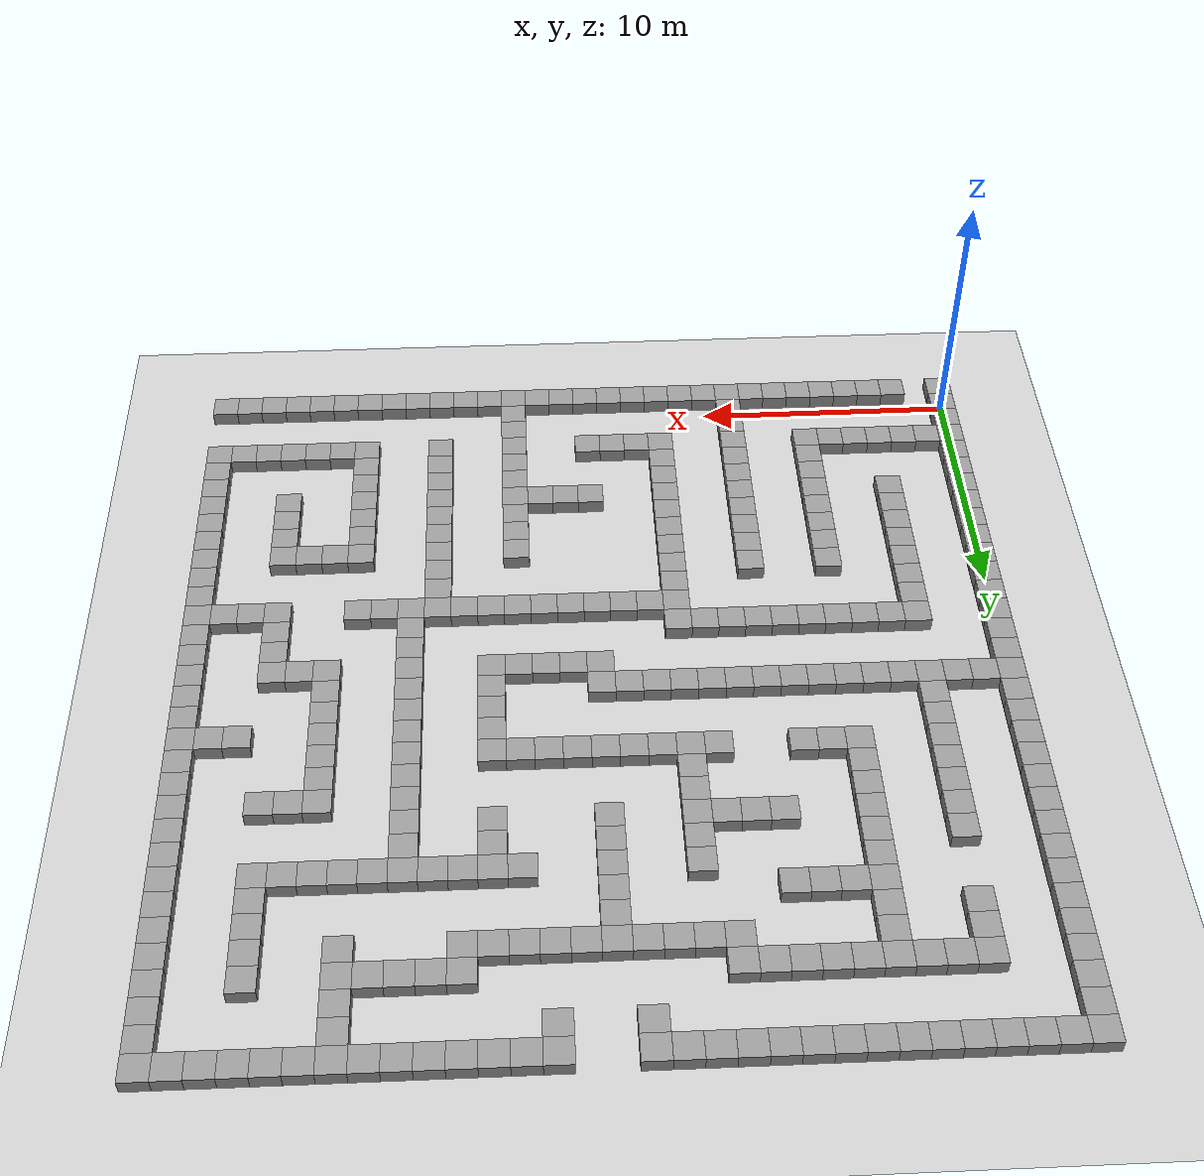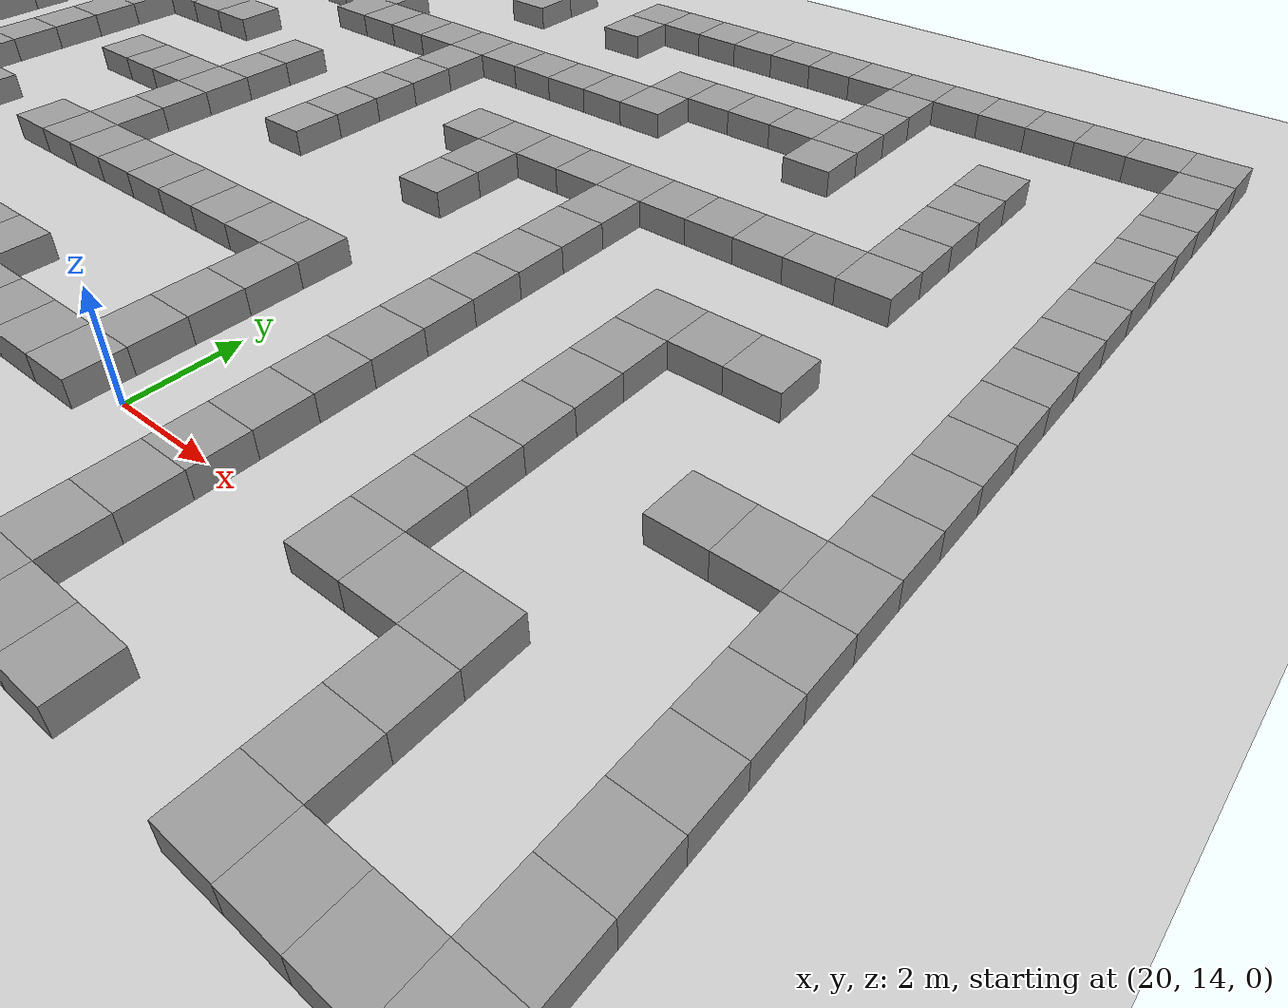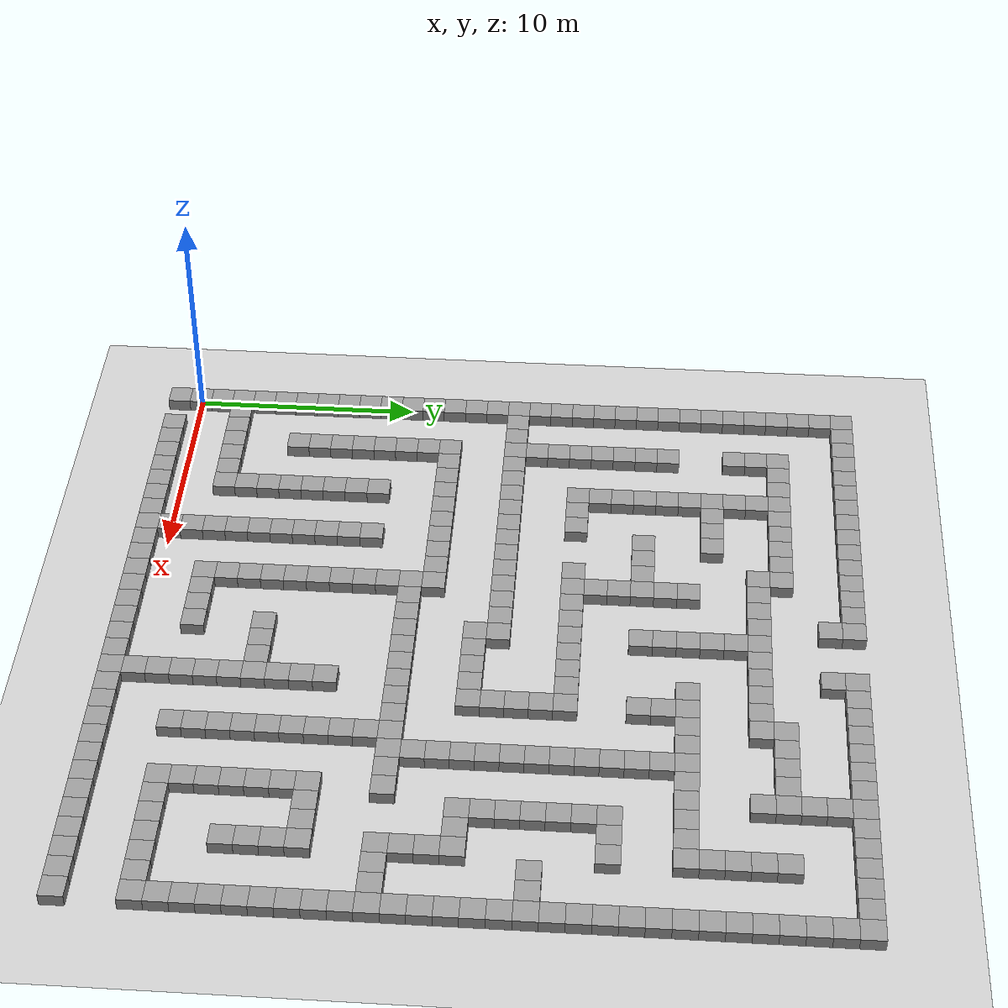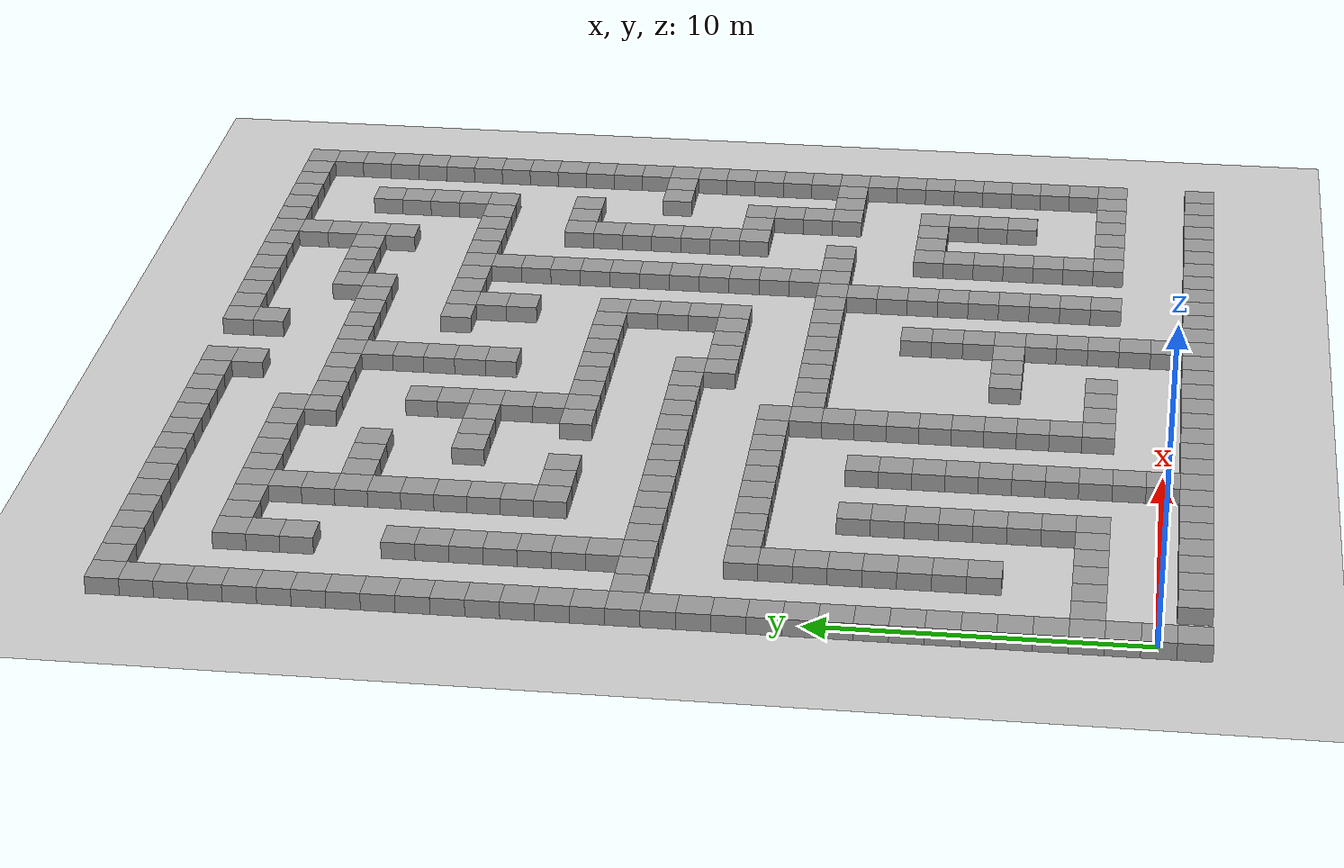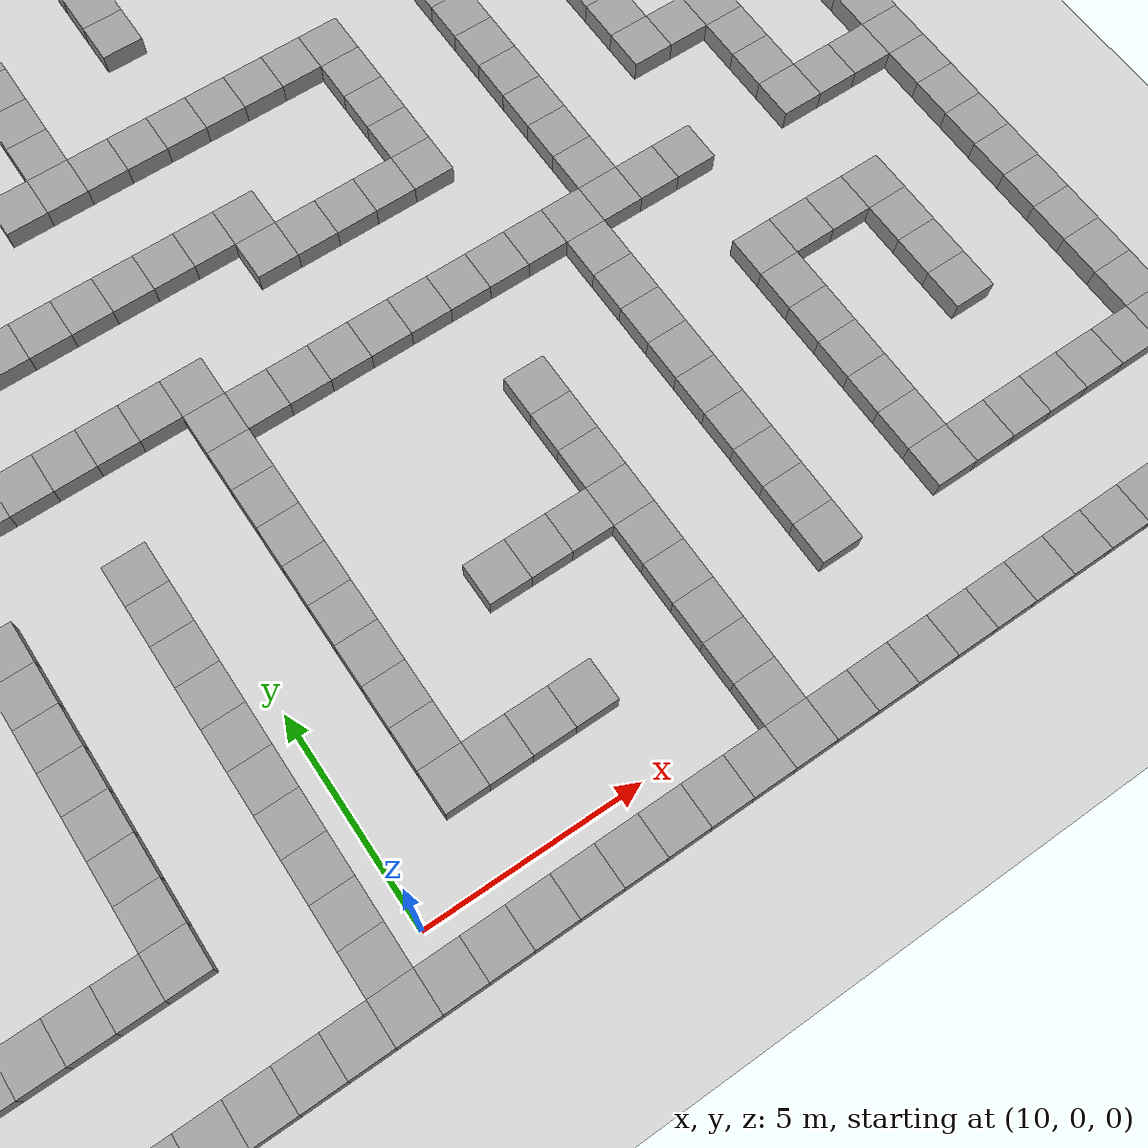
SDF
<sdf version="1.4">
 <world name="default">
  <light name="sun" type="directional">
   <pose>0 0 10 0 -0 0</pose>
   <diffuse>0.8 0.8 0.8 1</diffuse>
   <specular>0.2 0.2 0.2 1</specular>
   <attenuation>
    <range>1000</range>
    <constant>0.9</constant>
    <linear>0.01</linear>
    <quadratic>0.001</quadratic>
   </attenuation>
   <direction>-0.5 0.1 -0.9</direction>
  </light>
  <model name="ground_plane">
   <static>1</static>
   <link name="link">
    <collision name="collision">
     <geometry><plane><normal>0 0 1</normal><size>100 100</size></plane></geometry>
     <surface><friction><ode><mu>100</mu><mu2>50</mu2></ode></friction></surface>
    </collision>
    <visual name="visual">
     <cast_shadows>0</cast_shadows>
     <geometry><plane><normal>0 0 1</normal><size>100 100</size></plane></geometry>
     <material>
      <script><uri>file://media/materials/scripts/gazebo.material</uri><name>Gazebo/Grey</name></script>
     </material>
    </visual>
    <velocity_decay><linear>0</linear><angular>0</angular></velocity_decay>
   </link>
  </model>
  <physics type="ode">
   <max_step_size>0.001</max_step_size>
   <real_time_factor>1</real_time_factor>
   <real_time_update_rate>1000</real_time_update_rate>
   <gravity>0 0 -9.8</gravity>
  </physics>
  <scene><ambient>0.4 0.4 0.4 1</ambient><background>0.7 0.7 0.7 1</background><shadows>1</shadows></scene>
  <spherical_coordinates>
   <surface_model>EARTH_WGS84</surface_model>
   <latitude_deg>0</latitude_deg>
   <longitude_deg>0</longitude_deg>
   <elevation>0</elevation>
   <heading_deg>0</heading_deg>
  </spherical_coordinates>
  <model name="unit_box_1">
   <pose>0 -1 0 0 -0 0</pose>
   <link name="link">
    <inertial>
     <mass>1</mass>
     <inertia><ixx>1</ixx><ixy>0</ixy><ixz>0</ixz><iyy>1</iyy><iyz>0</iyz><izz>1</izz></inertia>
    </inertial>
    <collision name="collision"><geometry><box><size>1 1 1</size></box></geometry></collision>
    <visual name="visual">
     <geometry><box><size>1 1 1</size></box></geometry>
     <material>
      <script><uri>file://media/materials/scripts/gazebo.material</uri><name>Gazebo/Grey</name></script>
     </material>
    </visual>
    <velocity_decay><linear>0</linear><angular>0</angular></velocity_decay>
   </link>
   <static>1</static>
  </model>
  <model name="unit_box_2">
   <pose>2 -1 0 0 -0 0</pose>
   <link name="link">
    <inertial>
     <mass>1</mass>
     <inertia><ixx>1</ixx><ixy>0</ixy><ixz>0</ixz><iyy>1</iyy><iyz>0</iyz><izz>1</izz></inertia>
    </inertial>
    <collision name="collision"><geometry><box><size>1 1 1</size></box></geometry></collision>
    <visual name="visual">
     <geometry><box><size>1 1 1</size></box></geometry>
     <material>
      <script><uri>file://media/materials/scripts/gazebo.material</uri><name>Gazebo/Grey</name></script>
     </material>
    </visual>
    <velocity_decay><linear>0</linear><angular>0</angular></velocity_decay>
   </link>
   <static>1</static>
  </model>
  <model name="unit_box_3">
   <pose>3 -1 0 0 -0 0</pose>
   <link name="link">
    <inertial>
     <mass>1</mass>
     <inertia><ixx>1</ixx><ixy>0</ixy><ixz>0</ixz><iyy>1</iyy><iyz>0</iyz><izz>1</izz></inertia>
    </inertial>
    <collision name="collision"><geometry><box><size>1 1 1</size></box></geometry></collision>
    <visual name="visual">
     <geometry><box><size>1 1 1</size></box></geometry>
     <material>
      <script><uri>file://media/materials/scripts/gazebo.material</uri><name>Gazebo/Grey</name></script>
     </material>
    </visual>
    <velocity_decay><linear>0</linear><angular>0</angular></velocity_decay>
   </link>
   <static>1</static>
  </model>
  <model name="unit_box_4">
   <pose>4 -1 0 0 -0 0</pose>
   <link name="link">
    <inertial>
     <mass>1</mass>
     <inertia><ixx>1</ixx><ixy>0</ixy><ixz>0</ixz><iyy>1</iyy><iyz>0</iyz><izz>1</izz></inertia>
    </inertial>
    <collision name="collision"><geometry><box><size>1 1 1</size></box></geometry></collision>
    <visual name="visual">
     <geometry><box><size>1 1 1</size></box></geometry>
     <material>
      <script><uri>file://media/materials/scripts/gazebo.material</uri><name>Gazebo/Grey</name></script>
     </material>
    </visual>
    <velocity_decay><linear>0</linear><angular>0</angular></velocity_decay>
   </link>
   <static>1</static>
  </model>
  <model name="unit_box_5">
   <pose>5 -1 0 0 -0 0</pose>
   <link name="link">
    <inertial>
     <mass>1</mass>
     <inertia><ixx>1</ixx><ixy>0</ixy><ixz>0</ixz><iyy>1</iyy><iyz>0</iyz><izz>1</izz></inertia>
    </inertial>
    <collision name="collision"><geometry><box><size>1 1 1</size></box></geometry></collision>
    <visual name="visual">
     <geometry><box><size>1 1 1</size></box></geometry>
     <material>
      <script><uri>file://media/materials/scripts/gazebo.material</uri><name>Gazebo/Grey</name></script>
     </material>
    </visual>
    <velocity_decay><linear>0</linear><angular>0</angular></velocity_decay>
   </link>
   <static>1</static>
  </model>
  <model name="unit_box_6">
   <pose>6 -1 0 0 -0 0</pose>
   <link name="link">
    <inertial>
     <mass>1</mass>
     <inertia><ixx>1</ixx><ixy>0</ixy><ixz>0</ixz><iyy>1</iyy><iyz>0</iyz><izz>1</izz></inertia>
    </inertial>
    <collision name="collision"><geometry><box><size>1 1 1</size></box></geometry></collision>
    <visual name="visual">
     <geometry><box><size>1 1 1</size></box></geometry>
     <material>
      <script><uri>file://media/materials/scripts/gazebo.material</uri><name>Gazebo/Grey</name></script>
     </material>
    </visual>
    <velocity_decay><linear>0</linear><angular>0</angular></velocity_decay>
   </link>
   <static>1</static>
  </model>
  <model name="unit_box_7">
   <pose>7 -1 0 0 -0 0</pose>
   <link name="link">
    <inertial>
     <mass>1</mass>
     <inertia><ixx>1</ixx><ixy>0</ixy><ixz>0</ixz><iyy>1</iyy><iyz>0</iyz><izz>1</izz></inertia>
    </inertial>
    <collision name="collision"><geometry><box><size>1 1 1</size></box></geometry></collision>
    <visual name="visual">
     <geometry><box><size>1 1 1</size></box></geometry>
     <material>
      <script><uri>file://media/materials/scripts/gazebo.material</uri><name>Gazebo/Grey</name></script>
     </material>
    </visual>
    <velocity_decay><linear>0</linear><angular>0</angular></velocity_decay>
   </link>
   <static>1</static>
  </model>
  <model name="unit_box_8">
   <pose>8 -1 0 0 -0 0</pose>
   <link name="link">
    <inertial>
     <mass>1</mass>
     <inertia><ixx>1</ixx><ixy>0</ixy><ixz>0</ixz><iyy>1</iyy><iyz>0</iyz><izz>1</izz></inertia>
    </inertial>
    <collision name="collision"><geometry><box><size>1 1 1</size></box></geometry></collision>
    <visual name="visual">
     <geometry><box><size>1 1 1</size></box></geometry>
     <material>
      <script><uri>file://media/materials/scripts/gazebo.material</uri><name>Gazebo/Grey</name></script>
     </material>
    </visual>
    <velocity_decay><linear>0</linear><angular>0</angular></velocity_decay>
   </link>
   <static>1</static>
  </model>
  <model name="unit_box_9">
   <pose>9 -1 0 0 -0 0</pose>
   <link name="link">
    <inertial>
     <mass>1</mass>
     <inertia><ixx>1</ixx><ixy>0</ixy><ixz>0</ixz><iyy>1</iyy><iyz>0</iyz><izz>1</izz></inertia>
    </inertial>
    <collision name="collision"><geometry><box><size>1 1 1</size></box></geometry></collision>
    <visual name="visual">
     <geometry><box><size>1 1 1</size></box></geometry>
     <material>
      <script><uri>file://media/materials/scripts/gazebo.material</uri><name>Gazebo/Grey</name></script>
     </material>
    </visual>
    <velocity_decay><linear>0</linear><angular>0</angular></velocity_decay>
   </link>
   <static>1</static>
  </model>
  <model name="unit_box_10">
   <pose>10 -1 0 0 -0 0</pose>
   <link name="link">
    <inertial>
     <mass>1</mass>
     <inertia><ixx>1</ixx><ixy>0</ixy><ixz>0</ixz><iyy>1</iyy><iyz>0</iyz><izz>1</izz></inertia>
    </inertial>
    <collision name="collision"><geometry><box><size>1 1 1</size></box></geometry></collision>
    <visual name="visual">
     <geometry><box><size>1 1 1</size></box></geometry>
     <material>
      <script><uri>file://media/materials/scripts/gazebo.material</uri><name>Gazebo/Grey</name></script>
     </material>
    </visual>
    <velocity_decay><linear>0</linear><angular>0</angular></velocity_decay>
   </link>
   <static>1</static>
  </model>
  <model name="unit_box_11">
   <pose>11 -1 0 0 -0 0</pose>
   <link name="link">
    <inertial>
     <mass>1</mass>
     <inertia><ixx>1</ixx><ixy>0</ixy><ixz>0</ixz><iyy>1</iyy><iyz>0</iyz><izz>1</izz></inertia>
    </inertial>
    <collision name="collision"><geometry><box><size>1 1 1</size></box></geometry></collision>
    <visual name="visual">
     <geometry><box><size>1 1 1</size></box></geometry>
     <material>
      <script><uri>file://media/materials/scripts/gazebo.material</uri><name>Gazebo/Grey</name></script>
     </material>
    </visual>
    <velocity_decay><linear>0</linear><angular>0</angular></velocity_decay>
   </link>
   <static>1</static>
  </model>
  <model name="unit_box_12">
   <pose>12 -1 0 0 -0 0</pose>
   <link name="link">
    <inertial>
     <mass>1</mass>
     <inertia><ixx>1</ixx><ixy>0</ixy><ixz>0</ixz><iyy>1</iyy><iyz>0</iyz><izz>1</izz></inertia>
    </inertial>
    <collision name="collision"><geometry><box><size>1 1 1</size></box></geometry></collision>
    <visual name="visual">
     <geometry><box><size>1 1 1</size></box></geometry>
     <material>
      <script><uri>file://media/materials/scripts/gazebo.material</uri><name>Gazebo/Grey</name></script>
     </material>
    </visual>
    <velocity_decay><linear>0</linear><angular>0</angular></velocity_decay>
   </link>
   <static>1</static>
  </model>
  <model name="unit_box_13">
   <pose>13 -1 0 0 -0 0</pose>
   <link name="link">
    <inertial>
     <mass>1</mass>
     <inertia><ixx>1</ixx><ixy>0</ixy><ixz>0</ixz><iyy>1</iyy><iyz>0</iyz><izz>1</izz></inertia>
    </inertial>
    <collision name="collision"><geometry><box><size>1 1 1</size></box></geometry></collision>
    <visual name="visual">
     <geometry><box><size>1 1 1</size></box></geometry>
     <material>
      <script><uri>file://media/materials/scripts/gazebo.material</uri><name>Gazebo/Grey</name></script>
     </material>
    </visual>
    <velocity_decay><linear>0</linear><angular>0</angular></velocity_decay>
   </link>
   <static>1</static>
  </model>
  <model name="unit_box_14">
   <pose>14 -1 0 0 -0 0</pose>
   <link name="link">
    <inertial>
     <mass>1</mass>
     <inertia><ixx>1</ixx><ixy>0</ixy><ixz>0</ixz><iyy>1</iyy><iyz>0</iyz><izz>1</izz></inertia>
    </inertial>
    <collision name="collision"><geometry><box><size>1 1 1</size></box></geometry></collision>
    <visual name="visual">
     <geometry><box><size>1 1 1</size></box></geometry>
     <material>
      <script><uri>file://media/materials/scripts/gazebo.material</uri><name>Gazebo/Grey</name></script>
     </material>
    </visual>
    <velocity_decay><linear>0</linear><angular>0</angular></velocity_decay>
   </link>
   <static>1</static>
  </model>
  <model name="unit_box_15">
   <pose>15 -1 0 0 -0 0</pose>
   <link name="link">
    <inertial>
     <mass>1</mass>
     <inertia><ixx>1</ixx><ixy>0</ixy><ixz>0</ixz><iyy>1</iyy><iyz>0</iyz><izz>1</izz></inertia>
    </inertial>
    <collision name="collision"><geometry><box><size>1 1 1</size></box></geometry></collision>
    <visual name="visual">
     <geometry><box><size>1 1 1</size></box></geometry>
     <material>
      <script><uri>file://media/materials/scripts/gazebo.material</uri><name>Gazebo/Grey</name></script>
     </material>
    </visual>
    <velocity_decay><linear>0</linear><angular>0</angular></velocity_decay>
   </link>
   <static>1</static>
  </model>
  <model name="unit_box_16">
   <pose>16 -1 0 0 -0 0</pose>
   <link name="link">
    <inertial>
     <mass>1</mass>
     <inertia><ixx>1</ixx><ixy>0</ixy><ixz>0</ixz><iyy>1</iyy><iyz>0</iyz><izz>1</izz></inertia>
    </inertial>
    <collision name="collision"><geometry><box><size>1 1 1</size></box></geometry></collision>
    <visual name="visual">
     <geometry><box><size>1 1 1</size></box></geometry>
     <material>
      <script><uri>file://media/materials/scripts/gazebo.material</uri><name>Gazebo/Grey</name></script>
     </material>
    </visual>
    <velocity_decay><linear>0</linear><angular>0</angular></velocity_decay>
   </link>
   <static>1</static>
  </model>
  <model name="unit_box_17">
   <pose>17 -1 0 0 -0 0</pose>
   <link name="link">
    <inertial>
     <mass>1</mass>
     <inertia><ixx>1</ixx><ixy>0</ixy><ixz>0</ixz><iyy>1</iyy><iyz>0</iyz><izz>1</izz></inertia>
    </inertial>
    <collision name="collision"><geometry><box><size>1 1 1</size></box></geometry></collision>
    <visual name="visual">
     <geometry><box><size>1 1 1</size></box></geometry>
     <material>
      <script><uri>file://media/materials/scripts/gazebo.material</uri><name>Gazebo/Grey</name></script>
     </material>
    </visual>
    <velocity_decay><linear>0</linear><angular>0</angular></velocity_decay>
   </link>
   <static>1</static>
  </model>
  <model name="unit_box_18">
   <pose>18 -1 0 0 -0 0</pose>
   <link name="link">
    <inertial>
     <mass>1</mass>
     <inertia><ixx>1</ixx><ixy>0</ixy><ixz>0</ixz><iyy>1</iyy><iyz>0</iyz><izz>1</izz></inertia>
    </inertial>
    <collision name="collision"><geometry><box><size>1 1 1</size></box></geometry></collision>
    <visual name="visual">
     <geometry><box><size>1 1 1</size></box></geometry>
     <material>
      <script><uri>file://media/materials/scripts/gazebo.material</uri><name>Gazebo/Grey</name></script>
     </material>
    </visual>
    <velocity_decay><linear>0</linear><angular>0</angular></velocity_decay>
   </link>
   <static>1</static>
  </model>
  <model name="unit_box_19">
   <pose>19 -1 0 0 -0 0</pose>
   <link name="link">
    <inertial>
     <mass>1</mass>
     <inertia><ixx>1</ixx><ixy>0</ixy><ixz>0</ixz><iyy>1</iyy><iyz>0</iyz><izz>1</izz></inertia>
    </inertial>
    <collision name="collision"><geometry><box><size>1 1 1</size></box></geometry></collision>
    <visual name="visual">
     <geometry><box><size>1 1 1</size></box></geometry>
     <material>
      <script><uri>file://media/materials/scripts/gazebo.material</uri><name>Gazebo/Grey</name></script>
     </material>
    </visual>
    <velocity_decay><linear>0</linear><angular>0</angular></velocity_decay>
   </link>
   <static>1</static>
  </model>
  <model name="unit_box_20">
   <pose>20 -1 0 0 -0 0</pose>
   <link name="link">
    <inertial>
     <mass>1</mass>
     <inertia><ixx>1</ixx><ixy>0</ixy><ixz>0</ixz><iyy>1</iyy><iyz>0</iyz><izz>1</izz></inertia>
    </inertial>
    <collision name="collision"><geometry><box><size>1 1 1</size></box></geometry></collision>
    <visual name="visual">
     <geometry><box><size>1 1 1</size></box></geometry>
     <material>
      <script><uri>file://media/materials/scripts/gazebo.material</uri><name>Gazebo/Grey</name></script>
     </material>
    </visual>
    <velocity_decay><linear>0</linear><angular>0</angular></velocity_decay>
   </link>
   <static>1</static>
  </model>
  <model name="unit_box_21">
   <pose>21 -1 0 0 -0 0</pose>
   <link name="link">
    <inertial>
     <mass>1</mass>
     <inertia><ixx>1</ixx><ixy>0</ixy><ixz>0</ixz><iyy>1</iyy><iyz>0</iyz><izz>1</izz></inertia>
    </inertial>
    <collision name="collision"><geometry><box><size>1 1 1</size></box></geometry></collision>
    <visual name="visual">
     <geometry><box><size>1 1 1</size></box></geometry>
     <material>
      <script><uri>file://media/materials/scripts/gazebo.material</uri><name>Gazebo/Grey</name></script>
     </material>
    </visual>
    <velocity_decay><linear>0</linear><angular>0</angular></velocity_decay>
   </link>
   <static>1</static>
  </model>
  <model name="unit_box_22">
   <pose>22 -1 0 0 -0 0</pose>
   <link name="link">
    <inertial>
     <mass>1</mass>
     <inertia><ixx>1</ixx><ixy>0</ixy><ixz>0</ixz><iyy>1</iyy><iyz>0</iyz><izz>1</izz></inertia>
    </inertial>
    <collision name="collision"><geometry><box><size>1 1 1</size></box></geometry></collision>
    <visual name="visual">
     <geometry><box><size>1 1 1</size></box></geometry>
     <material>
      <script><uri>file://media/materials/scripts/gazebo.material</uri><name>Gazebo/Grey</name></script>
     </material>
    </visual>
    <velocity_decay><linear>0</linear><angular>0</angular></velocity_decay>
   </link>
   <static>1</static>
  </model>
  <model name="unit_box_23">
   <pose>23 -1 0 0 -0 0</pose>
   <link name="link">
    <inertial>
     <mass>1</mass>
     <inertia><ixx>1</ixx><ixy>0</ixy><ixz>0</ixz><iyy>1</iyy><iyz>0</iyz><izz>1</izz></inertia>
    </inertial>
    <collision name="collision"><geometry><box><size>1 1 1</size></box></geometry></collision>
    <visual name="visual">
     <geometry><box><size>1 1 1</size></box></geometry>
     <material>
      <script><uri>file://media/materials/scripts/gazebo.material</uri><name>Gazebo/Grey</name></script>
     </material>
    </visual>
    <velocity_decay><linear>0</linear><angular>0</angular></velocity_decay>
   </link>
   <static>1</static>
  </model>
  <model name="unit_box_24">
   <pose>24 -1 0 0 -0 0</pose>
   <link name="link">
    <inertial>
     <mass>1</mass>
     <inertia><ixx>1</ixx><ixy>0</ixy><ixz>0</ixz><iyy>1</iyy><iyz>0</iyz><izz>1</izz></inertia>
    </inertial>
    <collision name="collision"><geometry><box><size>1 1 1</size></box></geometry></collision>
    <visual name="visual">
     <geometry><box><size>1 1 1</size></box></geometry>
     <material>
      <script><uri>file://media/materials/scripts/gazebo.material</uri><name>Gazebo/Grey</name></script>
     </material>
    </visual>
    <velocity_decay><linear>0</linear><angular>0</angular></velocity_decay>
   </link>
   <static>1</static>
  </model>
  <model name="unit_box_25">
   <pose>25 -1 0 0 -0 0</pose>
   <link name="link">
    <inertial>
     <mass>1</mass>
     <inertia><ixx>1</ixx><ixy>0</ixy><ixz>0</ixz><iyy>1</iyy><iyz>0</iyz><izz>1</izz></inertia>
    </inertial>
    <collision name="collision"><geometry><box><size>1 1 1</size></box></geometry></collision>
    <visual name="visual">
     <geometry><box><size>1 1 1</size></box></geometry>
     <material>
      <script><uri>file://media/materials/scripts/gazebo.material</uri><name>Gazebo/Grey</name></script>
     </material>
    </visual>
    <velocity_decay><linear>0</linear><angular>0</angular></velocity_decay>
   </link>
   <static>1</static>
  </model>
  <model name="unit_box_26">
   <pose>26 -1 0 0 -0 0</pose>
   <link name="link">
    <inertial>
     <mass>1</mass>
     <inertia><ixx>1</ixx><ixy>0</ixy><ixz>0</ixz><iyy>1</iyy><iyz>0</iyz><izz>1</izz></inertia>
    </inertial>
    <collision name="collision"><geometry><box><size>1 1 1</size></box></geometry></collision>
    <visual name="visual">
     <geometry><box><size>1 1 1</size></box></geometry>
     <material>
      <script><uri>file://media/materials/scripts/gazebo.material</uri><name>Gazebo/Grey</name></script>
     </material>
    </visual>
    <velocity_decay><linear>0</linear><angular>0</angular></velocity_decay>
   </link>
   <static>1</static>
  </model>
  <model name="unit_box_27">
   <pose>27 -1 0 0 -0 0</pose>
   <link name="link">
    <inertial>
     <mass>1</mass>
     <inertia><ixx>1</ixx><ixy>0</ixy><ixz>0</ixz><iyy>1</iyy><iyz>0</iyz><izz>1</izz></inertia>
    </inertial>
    <collision name="collision"><geometry><box><size>1 1 1</size></box></geometry></collision>
    <visual name="visual">
     <geometry><box><size>1 1 1</size></box></geometry>
     <material>
      <script><uri>file://media/materials/scripts/gazebo.material</uri><name>Gazebo/Grey</name></script>
     </material>
    </visual>
    <velocity_decay><linear>0</linear><angular>0</angular></velocity_decay>
   </link>
   <static>1</static>
  </model>
  <model name="unit_box_28">
   <pose>28 -1 0 0 -0 0</pose>
   <link name="link">
    <inertial>
     <mass>1</mass>
     <inertia><ixx>1</ixx><ixy>0</ixy><ixz>0</ixz><iyy>1</iyy><iyz>0</iyz><izz>1</izz></inertia>
    </inertial>
    <collision name="collision"><geometry><box><size>1 1 1</size></box></geometry></collision>
    <visual name="visual">
     <geometry><box><size>1 1 1</size></box></geometry>
     <material>
      <script><uri>file://media/materials/scripts/gazebo.material</uri><name>Gazebo/Grey</name></script>
     </material>
    </visual>
    <velocity_decay><linear>0</linear><angular>0</angular></velocity_decay>
   </link>
   <static>1</static>
  </model>
  <model name="unit_box_29">
   <pose>29 -1 0 0 -0 0</pose>
   <link name="link">
    <inertial>
     <mass>1</mass>
     <inertia><ixx>1</ixx><ixy>0</ixy><ixz>0</ixz><iyy>1</iyy><iyz>0</iyz><izz>1</izz></inertia>
    </inertial>
    <collision name="collision"><geometry><box><size>1 1 1</size></box></geometry></collision>
    <visual name="visual">
     <geometry><box><size>1 1 1</size></box></geometry>
     <material>
      <script><uri>file://media/materials/scripts/gazebo.material</uri><name>Gazebo/Grey</name></script>
     </material>
    </visual>
    <velocity_decay><linear>0</linear><angular>0</angular></velocity_decay>
   </link>
   <static>1</static>
  </model>
  <model name="unit_box_30">
   <pose>30 -1 0 0 -0 0</pose>
   <link name="link">
    <inertial>
     <mass>1</mass>
     <inertia><ixx>1</ixx><ixy>0</ixy><ixz>0</ixz><iyy>1</iyy><iyz>0</iyz><izz>1</izz></inertia>
    </inertial>
    <collision name="collision"><geometry><box><size>1 1 1</size></box></geometry></collision>
    <visual name="visual">
     <geometry><box><size>1 1 1</size></box></geometry>
     <material>
      <script><uri>file://media/materials/scripts/gazebo.material</uri><name>Gazebo/Grey</name></script>
     </material>
    </visual>
    <velocity_decay><linear>0</linear><angular>0</angular></velocity_decay>
   </link>
   <static>1</static>
  </model>
  <model name="unit_box_31">
   <pose>30 2 0 0 -0 0</pose>
   <link name="link">
    <inertial>
     <mass>1</mass>
     <inertia><ixx>1</ixx><ixy>0</ixy><ixz>0</ixz><iyy>1</iyy><iyz>0</iyz><izz>1</izz></inertia>
    </inertial>
    <collision name="collision"><geometry><box><size>1 1 1</size></box></geometry></collision>
    <visual name="visual">
     <geometry><box><size>1 1 1</size></box></geometry>
     <material>
      <script><uri>file://media/materials/scripts/gazebo.material</uri><name>Gazebo/Grey</name></script>
     </material>
    </visual>
    <velocity_decay><linear>0</linear><angular>0</angular></velocity_decay>
   </link>
   <static>1</static>
  </model>
  <model name="unit_box_32">
   <pose>30 3 0 0 -0 0</pose>
   <link name="link">
    <inertial>
     <mass>1</mass>
     <inertia><ixx>1</ixx><ixy>0</ixy><ixz>0</ixz><iyy>1</iyy><iyz>0</iyz><izz>1</izz></inertia>
    </inertial>
    <collision name="collision"><geometry><box><size>1 1 1</size></box></geometry></collision>
    <visual name="visual">
     <geometry><box><size>1 1 1</size></box></geometry>
     <material>
      <script><uri>file://media/materials/scripts/gazebo.material</uri><name>Gazebo/Grey</name></script>
     </material>
    </visual>
    <velocity_decay><linear>0</linear><angular>0</angular></velocity_decay>
   </link>
   <static>1</static>
  </model>
  <model name="unit_box_33">
   <pose>30 4 0 0 -0 0</pose>
   <link name="link">
    <inertial>
     <mass>1</mass>
     <inertia><ixx>1</ixx><ixy>0</ixy><ixz>0</ixz><iyy>1</iyy><iyz>0</iyz><izz>1</izz></inertia>
    </inertial>
    <collision name="collision"><geometry><box><size>1 1 1</size></box></geometry></collision>
    <visual name="visual">
     <geometry><box><size>1 1 1</size></box></geometry>
     <material>
      <script><uri>file://media/materials/scripts/gazebo.material</uri><name>Gazebo/Grey</name></script>
     </material>
    </visual>
    <velocity_decay><linear>0</linear><angular>0</angular></velocity_decay>
   </link>
   <static>1</static>
  </model>
  <model name="unit_box_34">
   <pose>30 5 0 0 -0 0</pose>
   <link name="link">
    <inertial>
     <mass>1</mass>
     <inertia><ixx>1</ixx><ixy>0</ixy><ixz>0</ixz><iyy>1</iyy><iyz>0</iyz><izz>1</izz></inertia>
    </inertial>
    <collision name="collision"><geometry><box><size>1 1 1</size></box></geometry></collision>
    <visual name="visual">
     <geometry><box><size>1 1 1</size></box></geometry>
     <material>
      <script><uri>file://media/materials/scripts/gazebo.material</uri><name>Gazebo/Grey</name></script>
     </material>
    </visual>
    <velocity_decay><linear>0</linear><angular>0</angular></velocity_decay>
   </link>
   <static>1</static>
  </model>
  <model name="unit_box_35">
   <pose>30 6 0 0 -0 0</pose>
   <link name="link">
    <inertial>
     <mass>1</mass>
     <inertia><ixx>1</ixx><ixy>0</ixy><ixz>0</ixz><iyy>1</iyy><iyz>0</iyz><izz>1</izz></inertia>
    </inertial>
    <collision name="collision"><geometry><box><size>1 1 1</size></box></geometry></collision>
    <visual name="visual">
     <geometry><box><size>1 1 1</size></box></geometry>
     <material>
      <script><uri>file://media/materials/scripts/gazebo.material</uri><name>Gazebo/Grey</name></script>
     </material>
    </visual>
    <velocity_decay><linear>0</linear><angular>0</angular></velocity_decay>
   </link>
   <static>1</static>
  </model>
  <model name="unit_box_36">
   <pose>30 7 0 0 -0 0</pose>
   <link name="link">
    <inertial>
     <mass>1</mass>
     <inertia><ixx>1</ixx><ixy>0</ixy><ixz>0</ixz><iyy>1</iyy><iyz>0</iyz><izz>1</izz></inertia>
    </inertial>
    <collision name="collision"><geometry><box><size>1 1 1</size></box></geometry></collision>
    <visual name="visual">
     <geometry><box><size>1 1 1</size></box></geometry>
     <material>
      <script><uri>file://media/materials/scripts/gazebo.material</uri><name>Gazebo/Grey</name></script>
     </material>
    </visual>
    <velocity_decay><linear>0</linear><angular>0</angular></velocity_decay>
   </link>
   <static>1</static>
  </model>
  <model name="unit_box_37">
   <pose>30 8 0 0 -0 0</pose>
   <link name="link">
    <inertial>
     <mass>1</mass>
     <inertia><ixx>1</ixx><ixy>0</ixy><ixz>0</ixz><iyy>1</iyy><iyz>0</iyz><izz>1</izz></inertia>
    </inertial>
    <collision name="collision"><geometry><box><size>1 1 1</size></box></geometry></collision>
    <visual name="visual">
     <geometry><box><size>1 1 1</size></box></geometry>
     <material>
      <script><uri>file://media/materials/scripts/gazebo.material</uri><name>Gazebo/Grey</name></script>
     </material>
    </visual>
    <velocity_decay><linear>0</linear><angular>0</angular></velocity_decay>
   </link>
   <static>1</static>
  </model>
  <model name="unit_box_38">
   <pose>30 9 0 0 -0 0</pose>
   <link name="link">
    <inertial>
     <mass>1</mass>
     <inertia><ixx>1</ixx><ixy>0</ixy><ixz>0</ixz><iyy>1</iyy><iyz>0</iyz><izz>1</izz></inertia>
    </inertial>
    <collision name="collision"><geometry><box><size>1 1 1</size></box></geometry></collision>
    <visual name="visual">
     <geometry><box><size>1 1 1</size></box></geometry>
     <material>
      <script><uri>file://media/materials/scripts/gazebo.material</uri><name>Gazebo/Grey</name></script>
     </material>
    </visual>
    <velocity_decay><linear>0</linear><angular>0</angular></velocity_decay>
   </link>
   <static>1</static>
  </model>
  <model name="unit_box_39">
   <pose>30 10 0 0 -0 0</pose>
   <link name="link">
    <inertial>
     <mass>1</mass>
     <inertia><ixx>1</ixx><ixy>0</ixy><ixz>0</ixz><iyy>1</iyy><iyz>0</iyz><izz>1</izz></inertia>
    </inertial>
    <collision name="collision"><geometry><box><size>1 1 1</size></box></geometry></collision>
    <visual name="visual">
     <geometry><box><size>1 1 1</size></box></geometry>
     <material>
      <script><uri>file://media/materials/scripts/gazebo.material</uri><name>Gazebo/Grey</name></script>
     </material>
    </visual>
    <velocity_decay><linear>0</linear><angular>0</angular></velocity_decay>
   </link>
   <static>1</static>
  </model>
  <model name="unit_box_40">
   <pose>30 11 0 0 -0 0</pose>
   <link name="link">
    <inertial>
     <mass>1</mass>
     <inertia><ixx>1</ixx><ixy>0</ixy><ixz>0</ixz><iyy>1</iyy><iyz>0</iyz><izz>1</izz></inertia>
    </inertial>
    <collision name="collision"><geometry><box><size>1 1 1</size></box></geometry></collision>
    <visual name="visual">
     <geometry><box><size>1 1 1</size></box></geometry>
     <material>
      <script><uri>file://media/materials/scripts/gazebo.material</uri><name>Gazebo/Grey</name></script>
     </material>
    </visual>
    <velocity_decay><linear>0</linear><angular>0</angular></velocity_decay>
   </link>
   <static>1</static>
  </model>
  <model name="unit_box_41">
   <pose>30 12 0 0 -0 0</pose>
   <link name="link">
    <inertial>
     <mass>1</mass>
     <inertia><ixx>1</ixx><ixy>0</ixy><ixz>0</ixz><iyy>1</iyy><iyz>0</iyz><izz>1</izz></inertia>
    </inertial>
    <collision name="collision"><geometry><box><size>1 1 1</size></box></geometry></collision>
    <visual name="visual">
     <geometry><box><size>1 1 1</size></box></geometry>
     <material>
      <script><uri>file://media/materials/scripts/gazebo.material</uri><name>Gazebo/Grey</name></script>
     </material>
    </visual>
    <velocity_decay><linear>0</linear><angular>0</angular></velocity_decay>
   </link>
   <static>1</static>
  </model>
  <model name="unit_box_42">
   <pose>30 13 0 0 -0 0</pose>
   <link name="link">
    <inertial>
     <mass>1</mass>
     <inertia><ixx>1</ixx><ixy>0</ixy><ixz>0</ixz><iyy>1</iyy><iyz>0</iyz><izz>1</izz></inertia>
    </inertial>
    <collision name="collision"><geometry><box><size>1 1 1</size></box></geometry></collision>
    <visual name="visual">
     <geometry><box><size>1 1 1</size></box></geometry>
     <material>
      <script><uri>file://media/materials/scripts/gazebo.material</uri><name>Gazebo/Grey</name></script>
     </material>
    </visual>
    <velocity_decay><linear>0</linear><angular>0</angular></velocity_decay>
   </link>
   <static>1</static>
  </model>
  <model name="unit_box_43">
   <pose>30 14 0 0 -0 0</pose>
   <link name="link">
    <inertial>
     <mass>1</mass>
     <inertia><ixx>1</ixx><ixy>0</ixy><ixz>0</ixz><iyy>1</iyy><iyz>0</iyz><izz>1</izz></inertia>
    </inertial>
    <collision name="collision"><geometry><box><size>1 1 1</size></box></geometry></collision>
    <visual name="visual">
     <geometry><box><size>1 1 1</size></box></geometry>
     <material>
      <script><uri>file://media/materials/scripts/gazebo.material</uri><name>Gazebo/Grey</name></script>
     </material>
    </visual>
    <velocity_decay><linear>0</linear><angular>0</angular></velocity_decay>
   </link>
   <static>1</static>
  </model>
  <model name="unit_box_44">
   <pose>30 15 0 0 -0 0</pose>
   <link name="link">
    <inertial>
     <mass>1</mass>
     <inertia><ixx>1</ixx><ixy>0</ixy><ixz>0</ixz><iyy>1</iyy><iyz>0</iyz><izz>1</izz></inertia>
    </inertial>
    <collision name="collision"><geometry><box><size>1 1 1</size></box></geometry></collision>
    <visual name="visual">
     <geometry><box><size>1 1 1</size></box></geometry>
     <material>
      <script><uri>file://media/materials/scripts/gazebo.material</uri><name>Gazebo/Grey</name></script>
     </material>
    </visual>
    <velocity_decay><linear>0</linear><angular>0</angular></velocity_decay>
   </link>
   <static>1</static>
  </model>
  <model name="unit_box_45">
   <pose>30 16 0 0 -0 0</pose>
   <link name="link">
    <inertial>
     <mass>1</mass>
     <inertia><ixx>1</ixx><ixy>0</ixy><ixz>0</ixz><iyy>1</iyy><iyz>0</iyz><izz>1</izz></inertia>
    </inertial>
    <collision name="collision"><geometry><box><size>1 1 1</size></box></geometry></collision>
    <visual name="visual">
     <geometry><box><size>1 1 1</size></box></geometry>
     <material>
      <script><uri>file://media/materials/scripts/gazebo.material</uri><name>Gazebo/Grey</name></script>
     </material>
    </visual>
    <velocity_decay><linear>0</linear><angular>0</angular></velocity_decay>
   </link>
   <static>1</static>
  </model>
  <model name="unit_box_46">
   <pose>30 17 0 0 -0 0</pose>
   <link name="link">
    <inertial>
     <mass>1</mass>
     <inertia><ixx>1</ixx><ixy>0</ixy><ixz>0</ixz><iyy>1</iyy><iyz>0</iyz><izz>1</izz></inertia>
    </inertial>
    <collision name="collision"><geometry><box><size>1 1 1</size></box></geometry></collision>
    <visual name="visual">
     <geometry><box><size>1 1 1</size></box></geometry>
     <material>
      <script><uri>file://media/materials/scripts/gazebo.material</uri><name>Gazebo/Grey</name></script>
     </material>
    </visual>
    <velocity_decay><linear>0</linear><angular>0</angular></velocity_decay>
   </link>
   <static>1</static>
  </model>
  <model name="unit_box_47">
   <pose>30 18 0 0 -0 0</pose>
   <link name="link">
    <inertial>
     <mass>1</mass>
     <inertia><ixx>1</ixx><ixy>0</ixy><ixz>0</ixz><iyy>1</iyy><iyz>0</iyz><izz>1</izz></inertia>
    </inertial>
    <collision name="collision"><geometry><box><size>1 1 1</size></box></geometry></collision>
    <visual name="visual">
     <geometry><box><size>1 1 1</size></box></geometry>
     <material>
      <script><uri>file://media/materials/scripts/gazebo.material</uri><name>Gazebo/Grey</name></script>
     </material>
    </visual>
    <velocity_decay><linear>0</linear><angular>0</angular></velocity_decay>
   </link>
   <static>1</static>
  </model>
  <model name="unit_box_48">
   <pose>30 19 0 0 -0 0</pose>
   <link name="link">
    <inertial>
     <mass>1</mass>
     <inertia><ixx>1</ixx><ixy>0</ixy><ixz>0</ixz><iyy>1</iyy><iyz>0</iyz><izz>1</izz></inertia>
    </inertial>
    <collision name="collision"><geometry><box><size>1 1 1</size></box></geometry></collision>
    <visual name="visual">
     <geometry><box><size>1 1 1</size></box></geometry>
     <material>
      <script><uri>file://media/materials/scripts/gazebo.material</uri><name>Gazebo/Grey</name></script>
     </material>
    </visual>
    <velocity_decay><linear>0</linear><angular>0</angular></velocity_decay>
   </link>
   <static>1</static>
  </model>
  <model name="unit_box_49">
   <pose>30 20 0 0 -0 0</pose>
   <link name="link">
    <inertial>
     <mass>1</mass>
     <inertia><ixx>1</ixx><ixy>0</ixy><ixz>0</ixz><iyy>1</iyy><iyz>0</iyz><izz>1</izz></inertia>
    </inertial>
    <collision name="collision"><geometry><box><size>1 1 1</size></box></geometry></collision>
    <visual name="visual">
     <geometry><box><size>1 1 1</size></box></geometry>
     <material>
      <script><uri>file://media/materials/scripts/gazebo.material</uri><name>Gazebo/Grey</name></script>
     </material>
    </visual>
    <velocity_decay><linear>0</linear><angular>0</angular></velocity_decay>
   </link>
   <static>1</static>
  </model>
  <model name="unit_box_50">
   <pose>30 21 0 0 -0 0</pose>
   <link name="link">
    <inertial>
     <mass>1</mass>
     <inertia><ixx>1</ixx><ixy>0</ixy><ixz>0</ixz><iyy>1</iyy><iyz>0</iyz><izz>1</izz></inertia>
    </inertial>
    <collision name="collision"><geometry><box><size>1 1 1</size></box></geometry></collision>
    <visual name="visual">
     <geometry><box><size>1 1 1</size></box></geometry>
     <material>
      <script><uri>file://media/materials/scripts/gazebo.material</uri><name>Gazebo/Grey</name></script>
     </material>
    </visual>
    <velocity_decay><linear>0</linear><angular>0</angular></velocity_decay>
   </link>
   <static>1</static>
  </model>
  <model name="unit_box_51">
   <pose>30 22 0 0 -0 0</pose>
   <link name="link">
    <inertial>
     <mass>1</mass>
     <inertia><ixx>1</ixx><ixy>0</ixy><ixz>0</ixz><iyy>1</iyy><iyz>0</iyz><izz>1</izz></inertia>
    </inertial>
    <collision name="collision"><geometry><box><size>1 1 1</size></box></geometry></collision>
    <visual name="visual">
     <geometry><box><size>1 1 1</size></box></geometry>
     <material>
      <script><uri>file://media/materials/scripts/gazebo.material</uri><name>Gazebo/Grey</name></script>
     </material>
    </visual>
    <velocity_decay><linear>0</linear><angular>0</angular></velocity_decay>
   </link>
   <static>1</static>
  </model>
  <model name="unit_box_52">
   <pose>30 23 0 0 -0 0</pose>
   <link name="link">
    <inertial>
     <mass>1</mass>
     <inertia><ixx>1</ixx><ixy>0</ixy><ixz>0</ixz><iyy>1</iyy><iyz>0</iyz><izz>1</izz></inertia>
    </inertial>
    <collision name="collision"><geometry><box><size>1 1 1</size></box></geometry></collision>
    <visual name="visual">
     <geometry><box><size>1 1 1</size></box></geometry>
     <material>
      <script><uri>file://media/materials/scripts/gazebo.material</uri><name>Gazebo/Grey</name></script>
     </material>
    </visual>
    <velocity_decay><linear>0</linear><angular>0</angular></velocity_decay>
   </link>
   <static>1</static>
  </model>
  <model name="unit_box_53">
   <pose>30 24 0 0 -0 0</pose>
   <link name="link">
    <inertial>
     <mass>1</mass>
     <inertia><ixx>1</ixx><ixy>0</ixy><ixz>0</ixz><iyy>1</iyy><iyz>0</iyz><izz>1</izz></inertia>
    </inertial>
    <collision name="collision"><geometry><box><size>1 1 1</size></box></geometry></collision>
    <visual name="visual">
     <geometry><box><size>1 1 1</size></box></geometry>
     <material>
      <script><uri>file://media/materials/scripts/gazebo.material</uri><name>Gazebo/Grey</name></script>
     </material>
    </visual>
    <velocity_decay><linear>0</linear><angular>0</angular></velocity_decay>
   </link>
   <static>1</static>
  </model>
  <model name="unit_box_54">
   <pose>30 25 0 0 -0 0</pose>
   <link name="link">
    <inertial>
     <mass>1</mass>
     <inertia><ixx>1</ixx><ixy>0</ixy><ixz>0</ixz><iyy>1</iyy><iyz>0</iyz><izz>1</izz></inertia>
    </inertial>
    <collision name="collision"><geometry><box><size>1 1 1</size></box></geometry></collision>
    <visual name="visual">
     <geometry><box><size>1 1 1</size></box></geometry>
     <material>
      <script><uri>file://media/materials/scripts/gazebo.material</uri><name>Gazebo/Grey</name></script>
     </material>
    </visual>
    <velocity_decay><linear>0</linear><angular>0</angular></velocity_decay>
   </link>
   <static>1</static>
  </model>
  <model name="unit_box_55">
   <pose>30 26 0 0 -0 0</pose>
   <link name="link">
    <inertial>
     <mass>1</mass>
     <inertia><ixx>1</ixx><ixy>0</ixy><ixz>0</ixz><iyy>1</iyy><iyz>0</iyz><izz>1</izz></inertia>
    </inertial>
    <collision name="collision"><geometry><box><size>1 1 1</size></box></geometry></collision>
    <visual name="visual">
     <geometry><box><size>1 1 1</size></box></geometry>
     <material>
      <script><uri>file://media/materials/scripts/gazebo.material</uri><name>Gazebo/Grey</name></script>
     </material>
    </visual>
    <velocity_decay><linear>0</linear><angular>0</angular></velocity_decay>
   </link>
   <static>1</static>
  </model>
  <model name="unit_box_56">
   <pose>30 27 0 0 -0 0</pose>
   <link name="link">
    <inertial>
     <mass>1</mass>
     <inertia><ixx>1</ixx><ixy>0</ixy><ixz>0</ixz><iyy>1</iyy><iyz>0</iyz><izz>1</izz></inertia>
    </inertial>
    <collision name="collision"><geometry><box><size>1 1 1</size></box></geometry></collision>
    <visual name="visual">
     <geometry><box><size>1 1 1</size></box></geometry>
     <material>
      <script><uri>file://media/materials/scripts/gazebo.material</uri><name>Gazebo/Grey</name></script>
     </material>
    </visual>
    <velocity_decay><linear>0</linear><angular>0</angular></velocity_decay>
   </link>
   <static>1</static>
  </model>
  <model name="unit_box_57">
   <pose>30 28 0 0 -0 0</pose>
   <link name="link">
    <inertial>
     <mass>1</mass>
     <inertia><ixx>1</ixx><ixy>0</ixy><ixz>0</ixz><iyy>1</iyy><iyz>0</iyz><izz>1</izz></inertia>
    </inertial>
    <collision name="collision"><geometry><box><size>1 1 1</size></box></geometry></collision>
    <visual name="visual">
     <geometry><box><size>1 1 1</size></box></geometry>
     <material>
      <script><uri>file://media/materials/scripts/gazebo.material</uri><name>Gazebo/Grey</name></script>
     </material>
    </visual>
    <velocity_decay><linear>0</linear><angular>0</angular></velocity_decay>
   </link>
   <static>1</static>
  </model>
  <model name="unit_box_58">
   <pose>30 29 0 0 -0 0</pose>
   <link name="link">
    <inertial>
     <mass>1</mass>
     <inertia><ixx>1</ixx><ixy>0</ixy><ixz>0</ixz><iyy>1</iyy><iyz>0</iyz><izz>1</izz></inertia>
    </inertial>
    <collision name="collision"><geometry><box><size>1 1 1</size></box></geometry></collision>
    <visual name="visual">
     <geometry><box><size>1 1 1</size></box></geometry>
     <material>
      <script><uri>file://media/materials/scripts/gazebo.material</uri><name>Gazebo/Grey</name></script>
     </material>
    </visual>
    <velocity_decay><linear>0</linear><angular>0</angular></velocity_decay>
   </link>
   <static>1</static>
  </model>
  <model name="unit_box_59">
   <pose>30 30 0 0 -0 0</pose>
   <link name="link">
    <inertial>
     <mass>1</mass>
     <inertia><ixx>1</ixx><ixy>0</ixy><ixz>0</ixz><iyy>1</iyy><iyz>0</iyz><izz>1</izz></inertia>
    </inertial>
    <collision name="collision"><geometry><box><size>1 1 1</size></box></geometry></collision>
    <visual name="visual">
     <geometry><box><size>1 1 1</size></box></geometry>
     <material>
      <script><uri>file://media/materials/scripts/gazebo.material</uri><name>Gazebo/Grey</name></script>
     </material>
    </visual>
    <velocity_decay><linear>0</linear><angular>0</angular></velocity_decay>
   </link>
   <static>1</static>
  </model>
  <model name="unit_box_60">
   <pose>1 30 0 0 -0 0</pose>
   <link name="link">
    <inertial>
     <mass>1</mass>
     <inertia><ixx>1</ixx><ixy>0</ixy><ixz>0</ixz><iyy>1</iyy><iyz>0</iyz><izz>1</izz></inertia>
    </inertial>
    <collision name="collision"><geometry><box><size>1 1 1</size></box></geometry></collision>
    <visual name="visual">
     <geometry><box><size>1 1 1</size></box></geometry>
     <material>
      <script><uri>file://media/materials/scripts/gazebo.material</uri><name>Gazebo/Grey</name></script>
     </material>
    </visual>
    <velocity_decay><linear>0</linear><angular>0</angular></velocity_decay>
   </link>
   <static>1</static>
  </model>
  <model name="unit_box_61">
   <pose>2 30 0 0 -0 0</pose>
   <link name="link">
    <inertial>
     <mass>1</mass>
     <inertia><ixx>1</ixx><ixy>0</ixy><ixz>0</ixz><iyy>1</iyy><iyz>0</iyz><izz>1</izz></inertia>
    </inertial>
    <collision name="collision"><geometry><box><size>1 1 1</size></box></geometry></collision>
    <visual name="visual">
     <geometry><box><size>1 1 1</size></box></geometry>
     <material>
      <script><uri>file://media/materials/scripts/gazebo.material</uri><name>Gazebo/Grey</name></script>
     </material>
    </visual>
    <velocity_decay><linear>0</linear><angular>0</angular></velocity_decay>
   </link>
   <static>1</static>
  </model>
  <model name="unit_box_62">
   <pose>3 30 0 0 -0 0</pose>
   <link name="link">
    <inertial>
     <mass>1</mass>
     <inertia><ixx>1</ixx><ixy>0</ixy><ixz>0</ixz><iyy>1</iyy><iyz>0</iyz><izz>1</izz></inertia>
    </inertial>
    <collision name="collision"><geometry><box><size>1 1 1</size></box></geometry></collision>
    <visual name="visual">
     <geometry><box><size>1 1 1</size></box></geometry>
     <material>
      <script><uri>file://media/materials/scripts/gazebo.material</uri><name>Gazebo/Grey</name></script>
     </material>
    </visual>
    <velocity_decay><linear>0</linear><angular>0</angular></velocity_decay>
   </link>
   <static>1</static>
  </model>
  <model name="unit_box_63">
   <pose>4 30 0 0 -0 0</pose>
   <link name="link">
    <inertial>
     <mass>1</mass>
     <inertia><ixx>1</ixx><ixy>0</ixy><ixz>0</ixz><iyy>1</iyy><iyz>0</iyz><izz>1</izz></inertia>
    </inertial>
    <collision name="collision"><geometry><box><size>1 1 1</size></box></geometry></collision>
    <visual name="visual">
     <geometry><box><size>1 1 1</size></box></geometry>
     <material>
      <script><uri>file://media/materials/scripts/gazebo.material</uri><name>Gazebo/Grey</name></script>
     </material>
    </visual>
    <velocity_decay><linear>0</linear><angular>0</angular></velocity_decay>
   </link>
   <static>1</static>
  </model>
  <model name="unit_box_64">
   <pose>5 30 0 0 -0 0</pose>
   <link name="link">
    <inertial>
     <mass>1</mass>
     <inertia><ixx>1</ixx><ixy>0</ixy><ixz>0</ixz><iyy>1</iyy><iyz>0</iyz><izz>1</izz></inertia>
    </inertial>
    <collision name="collision"><geometry><box><size>1 1 1</size></box></geometry></collision>
    <visual name="visual">
     <geometry><box><size>1 1 1</size></box></geometry>
     <material>
      <script><uri>file://media/materials/scripts/gazebo.material</uri><name>Gazebo/Grey</name></script>
     </material>
    </visual>
    <velocity_decay><linear>0</linear><angular>0</angular></velocity_decay>
   </link>
   <static>1</static>
  </model>
  <model name="unit_box_65">
   <pose>6 30 0 0 -0 0</pose>
   <link name="link">
    <inertial>
     <mass>1</mass>
     <inertia><ixx>1</ixx><ixy>0</ixy><ixz>0</ixz><iyy>1</iyy><iyz>0</iyz><izz>1</izz></inertia>
    </inertial>
    <collision name="collision"><geometry><box><size>1 1 1</size></box></geometry></collision>
    <visual name="visual">
     <geometry><box><size>1 1 1</size></box></geometry>
     <material>
      <script><uri>file://media/materials/scripts/gazebo.material</uri><name>Gazebo/Grey</name></script>
     </material>
    </visual>
    <velocity_decay><linear>0</linear><angular>0</angular></velocity_decay>
   </link>
   <static>1</static>
  </model>
  <model name="unit_box_66">
   <pose>7 30 0 0 -0 0</pose>
   <link name="link">
    <inertial>
     <mass>1</mass>
     <inertia><ixx>1</ixx><ixy>0</ixy><ixz>0</ixz><iyy>1</iyy><iyz>0</iyz><izz>1</izz></inertia>
    </inertial>
    <collision name="collision"><geometry><box><size>1 1 1</size></box></geometry></collision>
    <visual name="visual">
     <geometry><box><size>1 1 1</size></box></geometry>
     <material>
      <script><uri>file://media/materials/scripts/gazebo.material</uri><name>Gazebo/Grey</name></script>
     </material>
    </visual>
    <velocity_decay><linear>0</linear><angular>0</angular></velocity_decay>
   </link>
   <static>1</static>
  </model>
  <model name="unit_box_67">
   <pose>8 30 0 0 -0 0</pose>
   <link name="link">
    <inertial>
     <mass>1</mass>
     <inertia><ixx>1</ixx><ixy>0</ixy><ixz>0</ixz><iyy>1</iyy><iyz>0</iyz><izz>1</izz></inertia>
    </inertial>
    <collision name="collision"><geometry><box><size>1 1 1</size></box></geometry></collision>
    <visual name="visual">
     <geometry><box><size>1 1 1</size></box></geometry>
     <material>
      <script><uri>file://media/materials/scripts/gazebo.material</uri><name>Gazebo/Grey</name></script>
     </material>
    </visual>
    <velocity_decay><linear>0</linear><angular>0</angular></velocity_decay>
   </link>
   <static>1</static>
  </model>
  <model name="unit_box_68">
   <pose>9 30 0 0 -0 0</pose>
   <link name="link">
    <inertial>
     <mass>1</mass>
     <inertia><ixx>1</ixx><ixy>0</ixy><ixz>0</ixz><iyy>1</iyy><iyz>0</iyz><izz>1</izz></inertia>
    </inertial>
    <collision name="collision"><geometry><box><size>1 1 1</size></box></geometry></collision>
    <visual name="visual">
     <geometry><box><size>1 1 1</size></box></geometry>
     <material>
      <script><uri>file://media/materials/scripts/gazebo.material</uri><name>Gazebo/Grey</name></script>
     </material>
    </visual>
    <velocity_decay><linear>0</linear><angular>0</angular></velocity_decay>
   </link>
   <static>1</static>
  </model>
  <model name="unit_box_69">
   <pose>10 30 0 0 -0 0</pose>
   <link name="link">
    <inertial>
     <mass>1</mass>
     <inertia><ixx>1</ixx><ixy>0</ixy><ixz>0</ixz><iyy>1</iyy><iyz>0</iyz><izz>1</izz></inertia>
    </inertial>
    <collision name="collision"><geometry><box><size>1 1 1</size></box></geometry></collision>
    <visual name="visual">
     <geometry><box><size>1 1 1</size></box></geometry>
     <material>
      <script><uri>file://media/materials/scripts/gazebo.material</uri><name>Gazebo/Grey</name></script>
     </material>
    </visual>
    <velocity_decay><linear>0</linear><angular>0</angular></velocity_decay>
   </link>
   <static>1</static>
  </model>
  <model name="unit_box_70">
   <pose>11 30 0 0 -0 0</pose>
   <link name="link">
    <inertial>
     <mass>1</mass>
     <inertia><ixx>1</ixx><ixy>0</ixy><ixz>0</ixz><iyy>1</iyy><iyz>0</iyz><izz>1</izz></inertia>
    </inertial>
    <collision name="collision"><geometry><box><size>1 1 1</size></box></geometry></collision>
    <visual name="visual">
     <geometry><box><size>1 1 1</size></box></geometry>
     <material>
      <script><uri>file://media/materials/scripts/gazebo.material</uri><name>Gazebo/Grey</name></script>
     </material>
    </visual>
    <velocity_decay><linear>0</linear><angular>0</angular></velocity_decay>
   </link>
   <static>1</static>
  </model>
  <model name="unit_box_71">
   <pose>12 30 0 0 -0 0</pose>
   <link name="link">
    <inertial>
     <mass>1</mass>
     <inertia><ixx>1</ixx><ixy>0</ixy><ixz>0</ixz><iyy>1</iyy><iyz>0</iyz><izz>1</izz></inertia>
    </inertial>
    <collision name="collision"><geometry><box><size>1 1 1</size></box></geometry></collision>
    <visual name="visual">
     <geometry><box><size>1 1 1</size></box></geometry>
     <material>
      <script><uri>file://media/materials/scripts/gazebo.material</uri><name>Gazebo/Grey</name></script>
     </material>
    </visual>
    <velocity_decay><linear>0</linear><angular>0</angular></velocity_decay>
   </link>
   <static>1</static>
  </model>
  <model name="unit_box_72">
   <pose>13 30 0 0 -0 0</pose>
   <link name="link">
    <inertial>
     <mass>1</mass>
     <inertia><ixx>1</ixx><ixy>0</ixy><ixz>0</ixz><iyy>1</iyy><iyz>0</iyz><izz>1</izz></inertia>
    </inertial>
    <collision name="collision"><geometry><box><size>1 1 1</size></box></geometry></collision>
    <visual name="visual">
     <geometry><box><size>1 1 1</size></box></geometry>
     <material>
      <script><uri>file://media/materials/scripts/gazebo.material</uri><name>Gazebo/Grey</name></script>
     </material>
    </visual>
    <velocity_decay><linear>0</linear><angular>0</angular></velocity_decay>
   </link>
   <static>1</static>
  </model>
  <model name="unit_box_73">
   <pose>14 30 0 0 -0 0</pose>
   <link name="link">
    <inertial>
     <mass>1</mass>
     <inertia><ixx>1</ixx><ixy>0</ixy><ixz>0</ixz><iyy>1</iyy><iyz>0</iyz><izz>1</izz></inertia>
    </inertial>
    <collision name="collision"><geometry><box><size>1 1 1</size></box></geometry></collision>
    <visual name="visual">
     <geometry><box><size>1 1 1</size></box></geometry>
     <material>
      <script><uri>file://media/materials/scripts/gazebo.material</uri><name>Gazebo/Grey</name></script>
     </material>
    </visual>
    <velocity_decay><linear>0</linear><angular>0</angular></velocity_decay>
   </link>
   <static>1</static>
  </model>
  <model name="unit_box_74">
   <pose>17 30 0 0 -0 0</pose>
   <link name="link">
    <inertial>
     <mass>1</mass>
     <inertia><ixx>1</ixx><ixy>0</ixy><ixz>0</ixz><iyy>1</iyy><iyz>0</iyz><izz>1</izz></inertia>
    </inertial>
    <collision name="collision"><geometry><box><size>1 1 1</size></box></geometry></collision>
    <visual name="visual">
     <geometry><box><size>1 1 1</size></box></geometry>
     <material>
      <script><uri>file://media/materials/scripts/gazebo.material</uri><name>Gazebo/Grey</name></script>
     </material>
    </visual>
    <velocity_decay><linear>0</linear><angular>0</angular></velocity_decay>
   </link>
   <static>1</static>
  </model>
  <model name="unit_box_75">
   <pose>18 30 0 0 -0 0</pose>
   <link name="link">
    <inertial>
     <mass>1</mass>
     <inertia><ixx>1</ixx><ixy>0</ixy><ixz>0</ixz><iyy>1</iyy><iyz>0</iyz><izz>1</izz></inertia>
    </inertial>
    <collision name="collision"><geometry><box><size>1 1 1</size></box></geometry></collision>
    <visual name="visual">
     <geometry><box><size>1 1 1</size></box></geometry>
     <material>
      <script><uri>file://media/materials/scripts/gazebo.material</uri><name>Gazebo/Grey</name></script>
     </material>
    </visual>
    <velocity_decay><linear>0</linear><angular>0</angular></velocity_decay>
   </link>
   <static>1</static>
  </model>
  <model name="unit_box_76">
   <pose>19 30 0 0 -0 0</pose>
   <link name="link">
    <inertial>
     <mass>1</mass>
     <inertia><ixx>1</ixx><ixy>0</ixy><ixz>0</ixz><iyy>1</iyy><iyz>0</iyz><izz>1</izz></inertia>
    </inertial>
    <collision name="collision"><geometry><box><size>1 1 1</size></box></geometry></collision>
    <visual name="visual">
     <geometry><box><size>1 1 1</size></box></geometry>
     <material>
      <script><uri>file://media/materials/scripts/gazebo.material</uri><name>Gazebo/Grey</name></script>
     </material>
    </visual>
    <velocity_decay><linear>0</linear><angular>0</angular></velocity_decay>
   </link>
   <static>1</static>
  </model>
  <model name="unit_box_77">
   <pose>20 30 0 0 -0 0</pose>
   <link name="link">
    <inertial>
     <mass>1</mass>
     <inertia><ixx>1</ixx><ixy>0</ixy><ixz>0</ixz><iyy>1</iyy><iyz>0</iyz><izz>1</izz></inertia>
    </inertial>
    <collision name="collision"><geometry><box><size>1 1 1</size></box></geometry></collision>
    <visual name="visual">
     <geometry><box><size>1 1 1</size></box></geometry>
     <material>
      <script><uri>file://media/materials/scripts/gazebo.material</uri><name>Gazebo/Grey</name></script>
     </material>
    </visual>
    <velocity_decay><linear>0</linear><angular>0</angular></velocity_decay>
   </link>
   <static>1</static>
  </model>
  <model name="unit_box_78">
   <pose>21 30 0 0 -0 0</pose>
   <link name="link">
    <inertial>
     <mass>1</mass>
     <inertia><ixx>1</ixx><ixy>0</ixy><ixz>0</ixz><iyy>1</iyy><iyz>0</iyz><izz>1</izz></inertia>
    </inertial>
    <collision name="collision"><geometry><box><size>1 1 1</size></box></geometry></collision>
    <visual name="visual">
     <geometry><box><size>1 1 1</size></box></geometry>
     <material>
      <script><uri>file://media/materials/scripts/gazebo.material</uri><name>Gazebo/Grey</name></script>
     </material>
    </visual>
    <velocity_decay><linear>0</linear><angular>0</angular></velocity_decay>
   </link>
   <static>1</static>
  </model>
  <model name="unit_box_79">
   <pose>22 30 0 0 -0 0</pose>
   <link name="link">
    <inertial>
     <mass>1</mass>
     <inertia><ixx>1</ixx><ixy>0</ixy><ixz>0</ixz><iyy>1</iyy><iyz>0</iyz><izz>1</izz></inertia>
    </inertial>
    <collision name="collision"><geometry><box><size>1 1 1</size></box></geometry></collision>
    <visual name="visual">
     <geometry><box><size>1 1 1</size></box></geometry>
     <material>
      <script><uri>file://media/materials/scripts/gazebo.material</uri><name>Gazebo/Grey</name></script>
     </material>
    </visual>
    <velocity_decay><linear>0</linear><angular>0</angular></velocity_decay>
   </link>
   <static>1</static>
  </model>
  <model name="unit_box_80">
   <pose>23 30 0 0 -0 0</pose>
   <link name="link">
    <inertial>
     <mass>1</mass>
     <inertia><ixx>1</ixx><ixy>0</ixy><ixz>0</ixz><iyy>1</iyy><iyz>0</iyz><izz>1</izz></inertia>
    </inertial>
    <collision name="collision"><geometry><box><size>1 1 1</size></box></geometry></collision>
    <visual name="visual">
     <geometry><box><size>1 1 1</size></box></geometry>
     <material>
      <script><uri>file://media/materials/scripts/gazebo.material</uri><name>Gazebo/Grey</name></script>
     </material>
    </visual>
    <velocity_decay><linear>0</linear><angular>0</angular></velocity_decay>
   </link>
   <static>1</static>
  </model>
  <model name="unit_box_81">
   <pose>24 30 0 0 -0 0</pose>
   <link name="link">
    <inertial>
     <mass>1</mass>
     <inertia><ixx>1</ixx><ixy>0</ixy><ixz>0</ixz><iyy>1</iyy><iyz>0</iyz><izz>1</izz></inertia>
    </inertial>
    <collision name="collision"><geometry><box><size>1 1 1</size></box></geometry></collision>
    <visual name="visual">
     <geometry><box><size>1 1 1</size></box></geometry>
     <material>
      <script><uri>file://media/materials/scripts/gazebo.material</uri><name>Gazebo/Grey</name></script>
     </material>
    </visual>
    <velocity_decay><linear>0</linear><angular>0</angular></velocity_decay>
   </link>
   <static>1</static>
  </model>
  <model name="unit_box_82">
   <pose>25 30 0 0 -0 0</pose>
   <link name="link">
    <inertial>
     <mass>1</mass>
     <inertia><ixx>1</ixx><ixy>0</ixy><ixz>0</ixz><iyy>1</iyy><iyz>0</iyz><izz>1</izz></inertia>
    </inertial>
    <collision name="collision"><geometry><box><size>1 1 1</size></box></geometry></collision>
    <visual name="visual">
     <geometry><box><size>1 1 1</size></box></geometry>
     <material>
      <script><uri>file://media/materials/scripts/gazebo.material</uri><name>Gazebo/Grey</name></script>
     </material>
    </visual>
    <velocity_decay><linear>0</linear><angular>0</angular></velocity_decay>
   </link>
   <static>1</static>
  </model>
  <model name="unit_box_83">
   <pose>26 30 0 0 -0 0</pose>
   <link name="link">
    <inertial>
     <mass>1</mass>
     <inertia><ixx>1</ixx><ixy>0</ixy><ixz>0</ixz><iyy>1</iyy><iyz>0</iyz><izz>1</izz></inertia>
    </inertial>
    <collision name="collision"><geometry><box><size>1 1 1</size></box></geometry></collision>
    <visual name="visual">
     <geometry><box><size>1 1 1</size></box></geometry>
     <material>
      <script><uri>file://media/materials/scripts/gazebo.material</uri><name>Gazebo/Grey</name></script>
     </material>
    </visual>
    <velocity_decay><linear>0</linear><angular>0</angular></velocity_decay>
   </link>
   <static>1</static>
  </model>
  <model name="unit_box_84">
   <pose>27 30 0 0 -0 0</pose>
   <link name="link">
    <inertial>
     <mass>1</mass>
     <inertia><ixx>1</ixx><ixy>0</ixy><ixz>0</ixz><iyy>1</iyy><iyz>0</iyz><izz>1</izz></inertia>
    </inertial>
    <collision name="collision"><geometry><box><size>1 1 1</size></box></geometry></collision>
    <visual name="visual">
     <geometry><box><size>1 1 1</size></box></geometry>
     <material>
      <script><uri>file://media/materials/scripts/gazebo.material</uri><name>Gazebo/Grey</name></script>
     </material>
    </visual>
    <velocity_decay><linear>0</linear><angular>0</angular></velocity_decay>
   </link>
   <static>1</static>
  </model>
  <model name="unit_box_85">
   <pose>28 30 0 0 -0 0</pose>
   <link name="link">
    <inertial>
     <mass>1</mass>
     <inertia><ixx>1</ixx><ixy>0</ixy><ixz>0</ixz><iyy>1</iyy><iyz>0</iyz><izz>1</izz></inertia>
    </inertial>
    <collision name="collision"><geometry><box><size>1 1 1</size></box></geometry></collision>
    <visual name="visual">
     <geometry><box><size>1 1 1</size></box></geometry>
     <material>
      <script><uri>file://media/materials/scripts/gazebo.material</uri><name>Gazebo/Grey</name></script>
     </material>
    </visual>
    <velocity_decay><linear>0</linear><angular>0</angular></velocity_decay>
   </link>
   <static>1</static>
  </model>
  <model name="unit_box_86">
   <pose>29 30 0 0 -0 0</pose>
   <link name="link">
    <inertial>
     <mass>1</mass>
     <inertia><ixx>1</ixx><ixy>0</ixy><ixz>0</ixz><iyy>1</iyy><iyz>0</iyz><izz>1</izz></inertia>
    </inertial>
    <collision name="collision"><geometry><box><size>1 1 1</size></box></geometry></collision>
    <visual name="visual">
     <geometry><box><size>1 1 1</size></box></geometry>
     <material>
      <script><uri>file://media/materials/scripts/gazebo.material</uri><name>Gazebo/Grey</name></script>
     </material>
    </visual>
    <velocity_decay><linear>0</linear><angular>0</angular></velocity_decay>
   </link>
   <static>1</static>
  </model>
  <model name="unit_box_87">
   <pose>30 30 0 0 -0 0</pose>
   <link name="link">
    <inertial>
     <mass>1</mass>
     <inertia><ixx>1</ixx><ixy>0</ixy><ixz>0</ixz><iyy>1</iyy><iyz>0</iyz><izz>1</izz></inertia>
    </inertial>
    <collision name="collision"><geometry><box><size>1 1 1</size></box></geometry></collision>
    <visual name="visual">
     <geometry><box><size>1 1 1</size></box></geometry>
     <material>
      <script><uri>file://media/materials/scripts/gazebo.material</uri><name>Gazebo/Grey</name></script>
     </material>
    </visual>
    <velocity_decay><linear>0</linear><angular>0</angular></velocity_decay>
   </link>
   <static>1</static>
  </model>
  <model name="unit_box_88">
   <pose>0 30 0 0 -0 0</pose>
   <link name="link">
    <inertial>
     <mass>1</mass>
     <inertia><ixx>1</ixx><ixy>0</ixy><ixz>0</ixz><iyy>1</iyy><iyz>0</iyz><izz>1</izz></inertia>
    </inertial>
    <collision name="collision"><geometry><box><size>1 1 1</size></box></geometry></collision>
    <visual name="visual">
     <geometry><box><size>1 1 1</size></box></geometry>
     <material>
      <script><uri>file://media/materials/scripts/gazebo.material</uri><name>Gazebo/Grey</name></script>
     </material>
    </visual>
    <velocity_decay><linear>0</linear><angular>0</angular></velocity_decay>
   </link>
   <static>1</static>
  </model>
  <model name="unit_box_89">
   <pose>0 29 0 0 -0 0</pose>
   <link name="link">
    <inertial>
     <mass>1</mass>
     <inertia><ixx>1</ixx><ixy>0</ixy><ixz>0</ixz><iyy>1</iyy><iyz>0</iyz><izz>1</izz></inertia>
    </inertial>
    <collision name="collision"><geometry><box><size>1 1 1</size></box></geometry></collision>
    <visual name="visual">
     <geometry><box><size>1 1 1</size></box></geometry>
     <material>
      <script><uri>file://media/materials/scripts/gazebo.material</uri><name>Gazebo/Grey</name></script>
     </material>
    </visual>
    <velocity_decay><linear>0</linear><angular>0</angular></velocity_decay>
   </link>
   <static>1</static>
  </model>
  <model name="unit_box_90">
   <pose>0 28 0 0 -0 0</pose>
   <link name="link">
    <inertial>
     <mass>1</mass>
     <inertia><ixx>1</ixx><ixy>0</ixy><ixz>0</ixz><iyy>1</iyy><iyz>0</iyz><izz>1</izz></inertia>
    </inertial>
    <collision name="collision"><geometry><box><size>1 1 1</size></box></geometry></collision>
    <visual name="visual">
     <geometry><box><size>1 1 1</size></box></geometry>
     <material>
      <script><uri>file://media/materials/scripts/gazebo.material</uri><name>Gazebo/Grey</name></script>
     </material>
    </visual>
    <velocity_decay><linear>0</linear><angular>0</angular></velocity_decay>
   </link>
   <static>1</static>
  </model>
  <model name="unit_box_91">
   <pose>0 27 0 0 -0 0</pose>
   <link name="link">
    <inertial>
     <mass>1</mass>
     <inertia><ixx>1</ixx><ixy>0</ixy><ixz>0</ixz><iyy>1</iyy><iyz>0</iyz><izz>1</izz></inertia>
    </inertial>
    <collision name="collision"><geometry><box><size>1 1 1</size></box></geometry></collision>
    <visual name="visual">
     <geometry><box><size>1 1 1</size></box></geometry>
     <material>
      <script><uri>file://media/materials/scripts/gazebo.material</uri><name>Gazebo/Grey</name></script>
     </material>
    </visual>
    <velocity_decay><linear>0</linear><angular>0</angular></velocity_decay>
   </link>
   <static>1</static>
  </model>
  <model name="unit_box_92">
   <pose>0 26 0 0 -0 0</pose>
   <link name="link">
    <inertial>
     <mass>1</mass>
     <inertia><ixx>1</ixx><ixy>0</ixy><ixz>0</ixz><iyy>1</iyy><iyz>0</iyz><izz>1</izz></inertia>
    </inertial>
    <collision name="collision"><geometry><box><size>1 1 1</size></box></geometry></collision>
    <visual name="visual">
     <geometry><box><size>1 1 1</size></box></geometry>
     <material>
      <script><uri>file://media/materials/scripts/gazebo.material</uri><name>Gazebo/Grey</name></script>
     </material>
    </visual>
    <velocity_decay><linear>0</linear><angular>0</angular></velocity_decay>
   </link>
   <static>1</static>
  </model>
  <model name="unit_box_93">
   <pose>0 25 0 0 -0 0</pose>
   <link name="link">
    <inertial>
     <mass>1</mass>
     <inertia><ixx>1</ixx><ixy>0</ixy><ixz>0</ixz><iyy>1</iyy><iyz>0</iyz><izz>1</izz></inertia>
    </inertial>
    <collision name="collision"><geometry><box><size>1 1 1</size></box></geometry></collision>
    <visual name="visual">
     <geometry><box><size>1 1 1</size></box></geometry>
     <material>
      <script><uri>file://media/materials/scripts/gazebo.material</uri><name>Gazebo/Grey</name></script>
     </material>
    </visual>
    <velocity_decay><linear>0</linear><angular>0</angular></velocity_decay>
   </link>
   <static>1</static>
  </model>
  <model name="unit_box_94">
   <pose>0 24 0 0 -0 0</pose>
   <link name="link">
    <inertial>
     <mass>1</mass>
     <inertia><ixx>1</ixx><ixy>0</ixy><ixz>0</ixz><iyy>1</iyy><iyz>0</iyz><izz>1</izz></inertia>
    </inertial>
    <collision name="collision"><geometry><box><size>1 1 1</size></box></geometry></collision>
    <visual name="visual">
     <geometry><box><size>1 1 1</size></box></geometry>
     <material>
      <script><uri>file://media/materials/scripts/gazebo.material</uri><name>Gazebo/Grey</name></script>
     </material>
    </visual>
    <velocity_decay><linear>0</linear><angular>0</angular></velocity_decay>
   </link>
   <static>1</static>
  </model>
  <model name="unit_box_95">
   <pose>0 23 0 0 -0 0</pose>
   <link name="link">
    <inertial>
     <mass>1</mass>
     <inertia><ixx>1</ixx><ixy>0</ixy><ixz>0</ixz><iyy>1</iyy><iyz>0</iyz><izz>1</izz></inertia>
    </inertial>
    <collision name="collision"><geometry><box><size>1 1 1</size></box></geometry></collision>
    <visual name="visual">
     <geometry><box><size>1 1 1</size></box></geometry>
     <material>
      <script><uri>file://media/materials/scripts/gazebo.material</uri><name>Gazebo/Grey</name></script>
     </material>
    </visual>
    <velocity_decay><linear>0</linear><angular>0</angular></velocity_decay>
   </link>
   <static>1</static>
  </model>
  <model name="unit_box_96">
   <pose>0 22 0 0 -0 0</pose>
   <link name="link">
    <inertial>
     <mass>1</mass>
     <inertia><ixx>1</ixx><ixy>0</ixy><ixz>0</ixz><iyy>1</iyy><iyz>0</iyz><izz>1</izz></inertia>
    </inertial>
    <collision name="collision"><geometry><box><size>1 1 1</size></box></geometry></collision>
    <visual name="visual">
     <geometry><box><size>1 1 1</size></box></geometry>
     <material>
      <script><uri>file://media/materials/scripts/gazebo.material</uri><name>Gazebo/Grey</name></script>
     </material>
    </visual>
    <velocity_decay><linear>0</linear><angular>0</angular></velocity_decay>
   </link>
   <static>1</static>
  </model>
  <model name="unit_box_97">
   <pose>0 21 0 0 -0 0</pose>
   <link name="link">
    <inertial>
     <mass>1</mass>
     <inertia><ixx>1</ixx><ixy>0</ixy><ixz>0</ixz><iyy>1</iyy><iyz>0</iyz><izz>1</izz></inertia>
    </inertial>
    <collision name="collision"><geometry><box><size>1 1 1</size></box></geometry></collision>
    <visual name="visual">
     <geometry><box><size>1 1 1</size></box></geometry>
     <material>
      <script><uri>file://media/materials/scripts/gazebo.material</uri><name>Gazebo/Grey</name></script>
     </material>
    </visual>
    <velocity_decay><linear>0</linear><angular>0</angular></velocity_decay>
   </link>
   <static>1</static>
  </model>
  <model name="unit_box_98">
   <pose>0 20 0 0 -0 0</pose>
   <link name="link">
    <inertial>
     <mass>1</mass>
     <inertia><ixx>1</ixx><ixy>0</ixy><ixz>0</ixz><iyy>1</iyy><iyz>0</iyz><izz>1</izz></inertia>
    </inertial>
    <collision name="collision"><geometry><box><size>1 1 1</size></box></geometry></collision>
    <visual name="visual">
     <geometry><box><size>1 1 1</size></box></geometry>
     <material>
      <script><uri>file://media/materials/scripts/gazebo.material</uri><name>Gazebo/Grey</name></script>
     </material>
    </visual>
    <velocity_decay><linear>0</linear><angular>0</angular></velocity_decay>
   </link>
   <static>1</static>
  </model>
  <model name="unit_box_99">
   <pose>0 19 0 0 -0 0</pose>
   <link name="link">
    <inertial>
     <mass>1</mass>
     <inertia><ixx>1</ixx><ixy>0</ixy><ixz>0</ixz><iyy>1</iyy><iyz>0</iyz><izz>1</izz></inertia>
    </inertial>
    <collision name="collision"><geometry><box><size>1 1 1</size></box></geometry></collision>
    <visual name="visual">
     <geometry><box><size>1 1 1</size></box></geometry>
     <material>
      <script><uri>file://media/materials/scripts/gazebo.material</uri><name>Gazebo/Grey</name></script>
     </material>
    </visual>
    <velocity_decay><linear>0</linear><angular>0</angular></velocity_decay>
   </link>
   <static>1</static>
  </model>
  <model name="unit_box_100">
   <pose>0 18 0 0 -0 0</pose>
   <link name="link">
    <inertial>
     <mass>1</mass>
     <inertia><ixx>1</ixx><ixy>0</ixy><ixz>0</ixz><iyy>1</iyy><iyz>0</iyz><izz>1</izz></inertia>
    </inertial>
    <collision name="collision"><geometry><box><size>1 1 1</size></box></geometry></collision>
    <visual name="visual">
     <geometry><box><size>1 1 1</size></box></geometry>
     <material>
      <script><uri>file://media/materials/scripts/gazebo.material</uri><name>Gazebo/Grey</name></script>
     </material>
    </visual>
    <velocity_decay><linear>0</linear><angular>0</angular></velocity_decay>
   </link>
   <static>1</static>
  </model>
  <model name="unit_box_101">
   <pose>0 17 0 0 -0 0</pose>
   <link name="link">
    <inertial>
     <mass>1</mass>
     <inertia><ixx>1</ixx><ixy>0</ixy><ixz>0</ixz><iyy>1</iyy><iyz>0</iyz><izz>1</izz></inertia>
    </inertial>
    <collision name="collision"><geometry><box><size>1 1 1</size></box></geometry></collision>
    <visual name="visual">
     <geometry><box><size>1 1 1</size></box></geometry>
     <material>
      <script><uri>file://media/materials/scripts/gazebo.material</uri><name>Gazebo/Grey</name></script>
     </material>
    </visual>
    <velocity_decay><linear>0</linear><angular>0</angular></velocity_decay>
   </link>
   <static>1</static>
  </model>
  <model name="unit_box_102">
   <pose>0 16 0 0 -0 0</pose>
   <link name="link">
    <inertial>
     <mass>1</mass>
     <inertia><ixx>1</ixx><ixy>0</ixy><ixz>0</ixz><iyy>1</iyy><iyz>0</iyz><izz>1</izz></inertia>
    </inertial>
    <collision name="collision"><geometry><box><size>1 1 1</size></box></geometry></collision>
    <visual name="visual">
     <geometry><box><size>1 1 1</size></box></geometry>
     <material>
      <script><uri>file://media/materials/scripts/gazebo.material</uri><name>Gazebo/Grey</name></script>
     </material>
    </visual>
    <velocity_decay><linear>0</linear><angular>0</angular></velocity_decay>
   </link>
   <static>1</static>
  </model>
  <model name="unit_box_103">
   <pose>0 15 0 0 -0 0</pose>
   <link name="link">
    <inertial>
     <mass>1</mass>
     <inertia><ixx>1</ixx><ixy>0</ixy><ixz>0</ixz><iyy>1</iyy><iyz>0</iyz><izz>1</izz></inertia>
    </inertial>
    <collision name="collision"><geometry><box><size>1 1 1</size></box></geometry></collision>
    <visual name="visual">
     <geometry><box><size>1 1 1</size></box></geometry>
     <material>
      <script><uri>file://media/materials/scripts/gazebo.material</uri><name>Gazebo/Grey</name></script>
     </material>
    </visual>
    <velocity_decay><linear>0</linear><angular>0</angular></velocity_decay>
   </link>
   <static>1</static>
  </model>
  <model name="unit_box_104">
   <pose>0 14 0 0 -0 0</pose>
   <link name="link">
    <inertial>
     <mass>1</mass>
     <inertia><ixx>1</ixx><ixy>0</ixy><ixz>0</ixz><iyy>1</iyy><iyz>0</iyz><izz>1</izz></inertia>
    </inertial>
    <collision name="collision"><geometry><box><size>1 1 1</size></box></geometry></collision>
    <visual name="visual">
     <geometry><box><size>1 1 1</size></box></geometry>
     <material>
      <script><uri>file://media/materials/scripts/gazebo.material</uri><name>Gazebo/Grey</name></script>
     </material>
    </visual>
    <velocity_decay><linear>0</linear><angular>0</angular></velocity_decay>
   </link>
   <static>1</static>
  </model>
  <model name="unit_box_105">
   <pose>0 13 0 0 -0 0</pose>
   <link name="link">
    <inertial>
     <mass>1</mass>
     <inertia><ixx>1</ixx><ixy>0</ixy><ixz>0</ixz><iyy>1</iyy><iyz>0</iyz><izz>1</izz></inertia>
    </inertial>
    <collision name="collision"><geometry><box><size>1 1 1</size></box></geometry></collision>
    <visual name="visual">
     <geometry><box><size>1 1 1</size></box></geometry>
     <material>
      <script><uri>file://media/materials/scripts/gazebo.material</uri><name>Gazebo/Grey</name></script>
     </material>
    </visual>
    <velocity_decay><linear>0</linear><angular>0</angular></velocity_decay>
   </link>
   <static>1</static>
  </model>
  <model name="unit_box_106">
   <pose>0 12 0 0 -0 0</pose>
   <link name="link">
    <inertial>
     <mass>1</mass>
     <inertia><ixx>1</ixx><ixy>0</ixy><ixz>0</ixz><iyy>1</iyy><iyz>0</iyz><izz>1</izz></inertia>
    </inertial>
    <collision name="collision"><geometry><box><size>1 1 1</size></box></geometry></collision>
    <visual name="visual">
     <geometry><box><size>1 1 1</size></box></geometry>
     <material>
      <script><uri>file://media/materials/scripts/gazebo.material</uri><name>Gazebo/Grey</name></script>
     </material>
    </visual>
    <velocity_decay><linear>0</linear><angular>0</angular></velocity_decay>
   </link>
   <static>1</static>
  </model>
  <model name="unit_box_107">
   <pose>0 11 0 0 -0 0</pose>
   <link name="link">
    <inertial>
     <mass>1</mass>
     <inertia><ixx>1</ixx><ixy>0</ixy><ixz>0</ixz><iyy>1</iyy><iyz>0</iyz><izz>1</izz></inertia>
    </inertial>
    <collision name="collision"><geometry><box><size>1 1 1</size></box></geometry></collision>
    <visual name="visual">
     <geometry><box><size>1 1 1</size></box></geometry>
     <material>
      <script><uri>file://media/materials/scripts/gazebo.material</uri><name>Gazebo/Grey</name></script>
     </material>
    </visual>
    <velocity_decay><linear>0</linear><angular>0</angular></velocity_decay>
   </link>
   <static>1</static>
  </model>
  <model name="unit_box_108">
   <pose>0 10 0 0 -0 0</pose>
   <link name="link">
    <inertial>
     <mass>1</mass>
     <inertia><ixx>1</ixx><ixy>0</ixy><ixz>0</ixz><iyy>1</iyy><iyz>0</iyz><izz>1</izz></inertia>
    </inertial>
    <collision name="collision"><geometry><box><size>1 1 1</size></box></geometry></collision>
    <visual name="visual">
     <geometry><box><size>1 1 1</size></box></geometry>
     <material>
      <script><uri>file://media/materials/scripts/gazebo.material</uri><name>Gazebo/Grey</name></script>
     </material>
    </visual>
    <velocity_decay><linear>0</linear><angular>0</angular></velocity_decay>
   </link>
   <static>1</static>
  </model>
  <model name="unit_box_109">
   <pose>0 9 0 0 -0 0</pose>
   <link name="link">
    <inertial>
     <mass>1</mass>
     <inertia><ixx>1</ixx><ixy>0</ixy><ixz>0</ixz><iyy>1</iyy><iyz>0</iyz><izz>1</izz></inertia>
    </inertial>
    <collision name="collision"><geometry><box><size>1 1 1</size></box></geometry></collision>
    <visual name="visual">
     <geometry><box><size>1 1 1</size></box></geometry>
     <material>
      <script><uri>file://media/materials/scripts/gazebo.material</uri><name>Gazebo/Grey</name></script>
     </material>
    </visual>
    <velocity_decay><linear>0</linear><angular>0</angular></velocity_decay>
   </link>
   <static>1</static>
  </model>
  <model name="unit_box_110">
   <pose>0 8 0 0 -0 0</pose>
   <link name="link">
    <inertial>
     <mass>1</mass>
     <inertia><ixx>1</ixx><ixy>0</ixy><ixz>0</ixz><iyy>1</iyy><iyz>0</iyz><izz>1</izz></inertia>
    </inertial>
    <collision name="collision"><geometry><box><size>1 1 1</size></box></geometry></collision>
    <visual name="visual">
     <geometry><box><size>1 1 1</size></box></geometry>
     <material>
      <script><uri>file://media/materials/scripts/gazebo.material</uri><name>Gazebo/Grey</name></script>
     </material>
    </visual>
    <velocity_decay><linear>0</linear><angular>0</angular></velocity_decay>
   </link>
   <static>1</static>
  </model>
  <model name="unit_box_111">
   <pose>0 7 0 0 -0 0</pose>
   <link name="link">
    <inertial>
     <mass>1</mass>
     <inertia><ixx>1</ixx><ixy>0</ixy><ixz>0</ixz><iyy>1</iyy><iyz>0</iyz><izz>1</izz></inertia>
    </inertial>
    <collision name="collision"><geometry><box><size>1 1 1</size></box></geometry></collision>
    <visual name="visual">
     <geometry><box><size>1 1 1</size></box></geometry>
     <material>
      <script><uri>file://media/materials/scripts/gazebo.material</uri><name>Gazebo/Grey</name></script>
     </material>
    </visual>
    <velocity_decay><linear>0</linear><angular>0</angular></velocity_decay>
   </link>
   <static>1</static>
  </model>
  <model name="unit_box_112">
   <pose>0 6 0 0 -0 0</pose>
   <link name="link">
    <inertial>
     <mass>1</mass>
     <inertia><ixx>1</ixx><ixy>0</ixy><ixz>0</ixz><iyy>1</iyy><iyz>0</iyz><izz>1</izz></inertia>
    </inertial>
    <collision name="collision"><geometry><box><size>1 1 1</size></box></geometry></collision>
    <visual name="visual">
     <geometry><box><size>1 1 1</size></box></geometry>
     <material>
      <script><uri>file://media/materials/scripts/gazebo.material</uri><name>Gazebo/Grey</name></script>
     </material>
    </visual>
    <velocity_decay><linear>0</linear><angular>0</angular></velocity_decay>
   </link>
   <static>1</static>
  </model>
  <model name="unit_box_113">
   <pose>0 5 0 0 -0 0</pose>
   <link name="link">
    <inertial>
     <mass>1</mass>
     <inertia><ixx>1</ixx><ixy>0</ixy><ixz>0</ixz><iyy>1</iyy><iyz>0</iyz><izz>1</izz></inertia>
    </inertial>
    <collision name="collision"><geometry><box><size>1 1 1</size></box></geometry></collision>
    <visual name="visual">
     <geometry><box><size>1 1 1</size></box></geometry>
     <material>
      <script><uri>file://media/materials/scripts/gazebo.material</uri><name>Gazebo/Grey</name></script>
     </material>
    </visual>
    <velocity_decay><linear>0</linear><angular>0</angular></velocity_decay>
   </link>
   <static>1</static>
  </model>
  <model name="unit_box_114">
   <pose>0 4 0 0 -0 0</pose>
   <link name="link">
    <inertial>
     <mass>1</mass>
     <inertia><ixx>1</ixx><ixy>0</ixy><ixz>0</ixz><iyy>1</iyy><iyz>0</iyz><izz>1</izz></inertia>
    </inertial>
    <collision name="collision"><geometry><box><size>1 1 1</size></box></geometry></collision>
    <visual name="visual">
     <geometry><box><size>1 1 1</size></box></geometry>
     <material>
      <script><uri>file://media/materials/scripts/gazebo.material</uri><name>Gazebo/Grey</name></script>
     </material>
    </visual>
    <velocity_decay><linear>0</linear><angular>0</angular></velocity_decay>
   </link>
   <static>1</static>
  </model>
  <model name="unit_box_115">
   <pose>0 3 0 0 -0 0</pose>
   <link name="link">
    <inertial>
     <mass>1</mass>
     <inertia><ixx>1</ixx><ixy>0</ixy><ixz>0</ixz><iyy>1</iyy><iyz>0</iyz><izz>1</izz></inertia>
    </inertial>
    <collision name="collision"><geometry><box><size>1 1 1</size></box></geometry></collision>
    <visual name="visual">
     <geometry><box><size>1 1 1</size></box></geometry>
     <material>
      <script><uri>file://media/materials/scripts/gazebo.material</uri><name>Gazebo/Grey</name></script>
     </material>
    </visual>
    <velocity_decay><linear>0</linear><angular>0</angular></velocity_decay>
   </link>
   <static>1</static>
  </model>
  <model name="unit_box_116">
   <pose>0 2 0 0 -0 0</pose>
   <link name="link">
    <inertial>
     <mass>1</mass>
     <inertia><ixx>1</ixx><ixy>0</ixy><ixz>0</ixz><iyy>1</iyy><iyz>0</iyz><izz>1</izz></inertia>
    </inertial>
    <collision name="collision"><geometry><box><size>1 1 1</size></box></geometry></collision>
    <visual name="visual">
     <geometry><box><size>1 1 1</size></box></geometry>
     <material>
      <script><uri>file://media/materials/scripts/gazebo.material</uri><name>Gazebo/Grey</name></script>
     </material>
    </visual>
    <velocity_decay><linear>0</linear><angular>0</angular></velocity_decay>
   </link>
   <static>1</static>
  </model>
  <model name="unit_box_117">
   <pose>0 1 0 0 -0 0</pose>
   <link name="link">
    <inertial>
     <mass>1</mass>
     <inertia><ixx>1</ixx><ixy>0</ixy><ixz>0</ixz><iyy>1</iyy><iyz>0</iyz><izz>1</izz></inertia>
    </inertial>
    <collision name="collision"><geometry><box><size>1 1 1</size></box></geometry></collision>
    <visual name="visual">
     <geometry><box><size>1 1 1</size></box></geometry>
     <material>
      <script><uri>file://media/materials/scripts/gazebo.material</uri><name>Gazebo/Grey</name></script>
     </material>
    </visual>
    <velocity_decay><linear>0</linear><angular>0</angular></velocity_decay>
   </link>
   <static>1</static>
  </model>
  <model name="unit_box_118">
   <link name="link">
    <inertial>
     <mass>1</mass>
     <inertia><ixx>1</ixx><ixy>0</ixy><ixz>0</ixz><iyy>1</iyy><iyz>0</iyz><izz>1</izz></inertia>
    </inertial>
    <collision name="collision"><geometry><box><size>1 1 1</size></box></geometry></collision>
    <visual name="visual">
     <geometry><box><size>1 1 1</size></box></geometry>
     <material>
      <script><uri>file://media/materials/scripts/gazebo.material</uri><name>Gazebo/Grey</name></script>
     </material>
    </visual>
    <velocity_decay><linear>0</linear><angular>0</angular></velocity_decay>
   </link>
   <static>1</static>
  </model>
  <model name="unit_box_119">
   <pose>1 2 0 0 -0 0</pose>
   <link name="link">
    <inertial>
     <mass>1</mass>
     <inertia><ixx>1</ixx><ixy>0</ixy><ixz>0</ixz><iyy>1</iyy><iyz>0</iyz><izz>1</izz></inertia>
    </inertial>
    <collision name="collision"><geometry><box><size>1 1 1</size></box></geometry></collision>
    <visual name="visual">
     <geometry><box><size>1 1 1</size></box></geometry>
     <material>
      <script><uri>file://media/materials/scripts/gazebo.material</uri><name>Gazebo/Grey</name></script>
     </material>
    </visual>
    <velocity_decay><linear>0</linear><angular>0</angular></velocity_decay>
   </link>
   <static>1</static>
  </model>
  <model name="unit_box_120">
   <pose>2 2 0 0 -0 0</pose>
   <link name="link">
    <inertial>
     <mass>1</mass>
     <inertia><ixx>1</ixx><ixy>0</ixy><ixz>0</ixz><iyy>1</iyy><iyz>0</iyz><izz>1</izz></inertia>
    </inertial>
    <collision name="collision"><geometry><box><size>1 1 1</size></box></geometry></collision>
    <visual name="visual">
     <geometry><box><size>1 1 1</size></box></geometry>
     <material>
      <script><uri>file://media/materials/scripts/gazebo.material</uri><name>Gazebo/Grey</name></script>
     </material>
    </visual>
    <velocity_decay><linear>0</linear><angular>0</angular></velocity_decay>
   </link>
   <static>1</static>
  </model>
  <model name="unit_box_121">
   <pose>3 2 0 0 -0 0</pose>
   <link name="link">
    <inertial>
     <mass>1</mass>
     <inertia><ixx>1</ixx><ixy>0</ixy><ixz>0</ixz><iyy>1</iyy><iyz>0</iyz><izz>1</izz></inertia>
    </inertial>
    <collision name="collision"><geometry><box><size>1 1 1</size></box></geometry></collision>
    <visual name="visual">
     <geometry><box><size>1 1 1</size></box></geometry>
     <material>
      <script><uri>file://media/materials/scripts/gazebo.material</uri><name>Gazebo/Grey</name></script>
     </material>
    </visual>
    <velocity_decay><linear>0</linear><angular>0</angular></velocity_decay>
   </link>
   <static>1</static>
  </model>
  <model name="unit_box_122">
   <pose>4 2 0 0 -0 0</pose>
   <link name="link">
    <inertial>
     <mass>1</mass>
     <inertia><ixx>1</ixx><ixy>0</ixy><ixz>0</ixz><iyy>1</iyy><iyz>0</iyz><izz>1</izz></inertia>
    </inertial>
    <collision name="collision"><geometry><box><size>1 1 1</size></box></geometry></collision>
    <visual name="visual">
     <geometry><box><size>1 1 1</size></box></geometry>
     <material>
      <script><uri>file://media/materials/scripts/gazebo.material</uri><name>Gazebo/Grey</name></script>
     </material>
    </visual>
    <velocity_decay><linear>0</linear><angular>0</angular></velocity_decay>
   </link>
   <static>1</static>
  </model>
  <model name="unit_box_123">
   <pose>5 2 0 0 -0 0</pose>
   <link name="link">
    <inertial>
     <mass>1</mass>
     <inertia><ixx>1</ixx><ixy>0</ixy><ixz>0</ixz><iyy>1</iyy><iyz>0</iyz><izz>1</izz></inertia>
    </inertial>
    <collision name="collision"><geometry><box><size>1 1 1</size></box></geometry></collision>
    <visual name="visual">
     <geometry><box><size>1 1 1</size></box></geometry>
     <material>
      <script><uri>file://media/materials/scripts/gazebo.material</uri><name>Gazebo/Grey</name></script>
     </material>
    </visual>
    <velocity_decay><linear>0</linear><angular>0</angular></velocity_decay>
   </link>
   <static>1</static>
  </model>
  <model name="unit_box_124">
   <pose>6 2 0 0 -0 0</pose>
   <link name="link">
    <inertial>
     <mass>1</mass>
     <inertia><ixx>1</ixx><ixy>0</ixy><ixz>0</ixz><iyy>1</iyy><iyz>0</iyz><izz>1</izz></inertia>
    </inertial>
    <collision name="collision"><geometry><box><size>1 1 1</size></box></geometry></collision>
    <visual name="visual">
     <geometry><box><size>1 1 1</size></box></geometry>
     <material>
      <script><uri>file://media/materials/scripts/gazebo.material</uri><name>Gazebo/Grey</name></script>
     </material>
    </visual>
    <velocity_decay><linear>0</linear><angular>0</angular></velocity_decay>
   </link>
   <static>1</static>
  </model>
  <model name="unit_box_125">
   <pose>9 0 0 0 -0 0</pose>
   <link name="link">
    <inertial>
     <mass>1</mass>
     <inertia><ixx>1</ixx><ixy>0</ixy><ixz>0</ixz><iyy>1</iyy><iyz>0</iyz><izz>1</izz></inertia>
    </inertial>
    <collision name="collision"><geometry><box><size>1 1 1</size></box></geometry></collision>
    <visual name="visual">
     <geometry><box><size>1 1 1</size></box></geometry>
     <material>
      <script><uri>file://media/materials/scripts/gazebo.material</uri><name>Gazebo/Grey</name></script>
     </material>
    </visual>
    <velocity_decay><linear>0</linear><angular>0</angular></velocity_decay>
   </link>
   <static>1</static>
  </model>
  <model name="unit_box_126">
   <pose>9 1 0 0 -0 0</pose>
   <link name="link">
    <inertial>
     <mass>1</mass>
     <inertia><ixx>1</ixx><ixy>0</ixy><ixz>0</ixz><iyy>1</iyy><iyz>0</iyz><izz>1</izz></inertia>
    </inertial>
    <collision name="collision"><geometry><box><size>1 1 1</size></box></geometry></collision>
    <visual name="visual">
     <geometry><box><size>1 1 1</size></box></geometry>
     <material>
      <script><uri>file://media/materials/scripts/gazebo.material</uri><name>Gazebo/Grey</name></script>
     </material>
    </visual>
    <velocity_decay><linear>0</linear><angular>0</angular></velocity_decay>
   </link>
   <static>1</static>
  </model>
  <model name="unit_box_127">
   <pose>9 2 0 0 -0 0</pose>
   <link name="link">
    <inertial>
     <mass>1</mass>
     <inertia><ixx>1</ixx><ixy>0</ixy><ixz>0</ixz><iyy>1</iyy><iyz>0</iyz><izz>1</izz></inertia>
    </inertial>
    <collision name="collision"><geometry><box><size>1 1 1</size></box></geometry></collision>
    <visual name="visual">
     <geometry><box><size>1 1 1</size></box></geometry>
     <material>
      <script><uri>file://media/materials/scripts/gazebo.material</uri><name>Gazebo/Grey</name></script>
     </material>
    </visual>
    <velocity_decay><linear>0</linear><angular>0</angular></velocity_decay>
   </link>
   <static>1</static>
  </model>
  <model name="unit_box_128">
   <pose>9 3 0 0 -0 0</pose>
   <link name="link">
    <inertial>
     <mass>1</mass>
     <inertia><ixx>1</ixx><ixy>0</ixy><ixz>0</ixz><iyy>1</iyy><iyz>0</iyz><izz>1</izz></inertia>
    </inertial>
    <collision name="collision"><geometry><box><size>1 1 1</size></box></geometry></collision>
    <visual name="visual">
     <geometry><box><size>1 1 1</size></box></geometry>
     <material>
      <script><uri>file://media/materials/scripts/gazebo.material</uri><name>Gazebo/Grey</name></script>
     </material>
    </visual>
    <velocity_decay><linear>0</linear><angular>0</angular></velocity_decay>
   </link>
   <static>1</static>
  </model>
  <model name="unit_box_129">
   <pose>9 4 0 0 -0 0</pose>
   <link name="link">
    <inertial>
     <mass>1</mass>
     <inertia><ixx>1</ixx><ixy>0</ixy><ixz>0</ixz><iyy>1</iyy><iyz>0</iyz><izz>1</izz></inertia>
    </inertial>
    <collision name="collision"><geometry><box><size>1 1 1</size></box></geometry></collision>
    <visual name="visual">
     <geometry><box><size>1 1 1</size></box></geometry>
     <material>
      <script><uri>file://media/materials/scripts/gazebo.material</uri><name>Gazebo/Grey</name></script>
     </material>
    </visual>
    <velocity_decay><linear>0</linear><angular>0</angular></velocity_decay>
   </link>
   <static>1</static>
  </model>
  <model name="unit_box_130">
   <pose>9 5 0 0 -0 0</pose>
   <link name="link">
    <inertial>
     <mass>1</mass>
     <inertia><ixx>1</ixx><ixy>0</ixy><ixz>0</ixz><iyy>1</iyy><iyz>0</iyz><izz>1</izz></inertia>
    </inertial>
    <collision name="collision"><geometry><box><size>1 1 1</size></box></geometry></collision>
    <visual name="visual">
     <geometry><box><size>1 1 1</size></box></geometry>
     <material>
      <script><uri>file://media/materials/scripts/gazebo.material</uri><name>Gazebo/Grey</name></script>
     </material>
    </visual>
    <velocity_decay><linear>0</linear><angular>0</angular></velocity_decay>
   </link>
   <static>1</static>
  </model>
  <model name="unit_box_131">
   <pose>9 6 0 0 -0 0</pose>
   <link name="link">
    <inertial>
     <mass>1</mass>
     <inertia><ixx>1</ixx><ixy>0</ixy><ixz>0</ixz><iyy>1</iyy><iyz>0</iyz><izz>1</izz></inertia>
    </inertial>
    <collision name="collision"><geometry><box><size>1 1 1</size></box></geometry></collision>
    <visual name="visual">
     <geometry><box><size>1 1 1</size></box></geometry>
     <material>
      <script><uri>file://media/materials/scripts/gazebo.material</uri><name>Gazebo/Grey</name></script>
     </material>
    </visual>
    <velocity_decay><linear>0</linear><angular>0</angular></velocity_decay>
   </link>
   <static>1</static>
  </model>
  <model name="unit_box_132">
   <pose>9 7 0 0 -0 0</pose>
   <link name="link">
    <inertial>
     <mass>1</mass>
     <inertia><ixx>1</ixx><ixy>0</ixy><ixz>0</ixz><iyy>1</iyy><iyz>0</iyz><izz>1</izz></inertia>
    </inertial>
    <collision name="collision"><geometry><box><size>1 1 1</size></box></geometry></collision>
    <visual name="visual">
     <geometry><box><size>1 1 1</size></box></geometry>
     <material>
      <script><uri>file://media/materials/scripts/gazebo.material</uri><name>Gazebo/Grey</name></script>
     </material>
    </visual>
    <velocity_decay><linear>0</linear><angular>0</angular></velocity_decay>
   </link>
   <static>1</static>
  </model>
  <model name="unit_box_133">
   <pose>9 8 0 0 -0 0</pose>
   <link name="link">
    <inertial>
     <mass>1</mass>
     <inertia><ixx>1</ixx><ixy>0</ixy><ixz>0</ixz><iyy>1</iyy><iyz>0</iyz><izz>1</izz></inertia>
    </inertial>
    <collision name="collision"><geometry><box><size>1 1 1</size></box></geometry></collision>
    <visual name="visual">
     <geometry><box><size>1 1 1</size></box></geometry>
     <material>
      <script><uri>file://media/materials/scripts/gazebo.material</uri><name>Gazebo/Grey</name></script>
     </material>
    </visual>
    <velocity_decay><linear>0</linear><angular>0</angular></velocity_decay>
   </link>
   <static>1</static>
  </model>
  <model name="unit_box_134">
   <pose>9 9 0 0 -0 0</pose>
   <link name="link">
    <inertial>
     <mass>1</mass>
     <inertia><ixx>1</ixx><ixy>0</ixy><ixz>0</ixz><iyy>1</iyy><iyz>0</iyz><izz>1</izz></inertia>
    </inertial>
    <collision name="collision"><geometry><box><size>1 1 1</size></box></geometry></collision>
    <visual name="visual">
     <geometry><box><size>1 1 1</size></box></geometry>
     <material>
      <script><uri>file://media/materials/scripts/gazebo.material</uri><name>Gazebo/Grey</name></script>
     </material>
    </visual>
    <velocity_decay><linear>0</linear><angular>0</angular></velocity_decay>
   </link>
   <static>1</static>
  </model>
  <model name="unit_box_135">
   <pose>6 3 0 0 -0 0</pose>
   <link name="link">
    <inertial>
     <mass>1</mass>
     <inertia><ixx>1</ixx><ixy>0</ixy><ixz>0</ixz><iyy>1</iyy><iyz>0</iyz><izz>1</izz></inertia>
    </inertial>
    <collision name="collision"><geometry><box><size>1 1 1</size></box></geometry></collision>
    <visual name="visual">
     <geometry><box><size>1 1 1</size></box></geometry>
     <material>
      <script><uri>file://media/materials/scripts/gazebo.material</uri><name>Gazebo/Grey</name></script>
     </material>
    </visual>
    <velocity_decay><linear>0</linear><angular>0</angular></velocity_decay>
   </link>
   <static>1</static>
  </model>
  <model name="unit_box_136">
   <pose>6 4 0 0 -0 0</pose>
   <link name="link">
    <inertial>
     <mass>1</mass>
     <inertia><ixx>1</ixx><ixy>0</ixy><ixz>0</ixz><iyy>1</iyy><iyz>0</iyz><izz>1</izz></inertia>
    </inertial>
    <collision name="collision"><geometry><box><size>1 1 1</size></box></geometry></collision>
    <visual name="visual">
     <geometry><box><size>1 1 1</size></box></geometry>
     <material>
      <script><uri>file://media/materials/scripts/gazebo.material</uri><name>Gazebo/Grey</name></script>
     </material>
    </visual>
    <velocity_decay><linear>0</linear><angular>0</angular></velocity_decay>
   </link>
   <static>1</static>
  </model>
  <model name="unit_box_137">
   <pose>6 5 0 0 -0 0</pose>
   <link name="link">
    <inertial>
     <mass>1</mass>
     <inertia><ixx>1</ixx><ixy>0</ixy><ixz>0</ixz><iyy>1</iyy><iyz>0</iyz><izz>1</izz></inertia>
    </inertial>
    <collision name="collision"><geometry><box><size>1 1 1</size></box></geometry></collision>
    <visual name="visual">
     <geometry><box><size>1 1 1</size></box></geometry>
     <material>
      <script><uri>file://media/materials/scripts/gazebo.material</uri><name>Gazebo/Grey</name></script>
     </material>
    </visual>
    <velocity_decay><linear>0</linear><angular>0</angular></velocity_decay>
   </link>
   <static>1</static>
  </model>
  <model name="unit_box_138">
   <pose>6 6 0 0 -0 0</pose>
   <link name="link">
    <inertial>
     <mass>1</mass>
     <inertia><ixx>1</ixx><ixy>0</ixy><ixz>0</ixz><iyy>1</iyy><iyz>0</iyz><izz>1</izz></inertia>
    </inertial>
    <collision name="collision"><geometry><box><size>1 1 1</size></box></geometry></collision>
    <visual name="visual">
     <geometry><box><size>1 1 1</size></box></geometry>
     <material>
      <script><uri>file://media/materials/scripts/gazebo.material</uri><name>Gazebo/Grey</name></script>
     </material>
    </visual>
    <velocity_decay><linear>0</linear><angular>0</angular></velocity_decay>
   </link>
   <static>1</static>
  </model>
  <model name="unit_box_139">
   <pose>6 7 0 0 -0 0</pose>
   <link name="link">
    <inertial>
     <mass>1</mass>
     <inertia><ixx>1</ixx><ixy>0</ixy><ixz>0</ixz><iyy>1</iyy><iyz>0</iyz><izz>1</izz></inertia>
    </inertial>
    <collision name="collision"><geometry><box><size>1 1 1</size></box></geometry></collision>
    <visual name="visual">
     <geometry><box><size>1 1 1</size></box></geometry>
     <material>
      <script><uri>file://media/materials/scripts/gazebo.material</uri><name>Gazebo/Grey</name></script>
     </material>
    </visual>
    <velocity_decay><linear>0</linear><angular>0</angular></velocity_decay>
   </link>
   <static>1</static>
  </model>
  <model name="unit_box_140">
   <pose>6 8 0 0 -0 0</pose>
   <link name="link">
    <inertial>
     <mass>1</mass>
     <inertia><ixx>1</ixx><ixy>0</ixy><ixz>0</ixz><iyy>1</iyy><iyz>0</iyz><izz>1</izz></inertia>
    </inertial>
    <collision name="collision"><geometry><box><size>1 1 1</size></box></geometry></collision>
    <visual name="visual">
     <geometry><box><size>1 1 1</size></box></geometry>
     <material>
      <script><uri>file://media/materials/scripts/gazebo.material</uri><name>Gazebo/Grey</name></script>
     </material>
    </visual>
    <velocity_decay><linear>0</linear><angular>0</angular></velocity_decay>
   </link>
   <static>1</static>
  </model>
  <model name="unit_box_141">
   <pose>6 9 0 0 -0 0</pose>
   <link name="link">
    <inertial>
     <mass>1</mass>
     <inertia><ixx>1</ixx><ixy>0</ixy><ixz>0</ixz><iyy>1</iyy><iyz>0</iyz><izz>1</izz></inertia>
    </inertial>
    <collision name="collision"><geometry><box><size>1 1 1</size></box></geometry></collision>
    <visual name="visual">
     <geometry><box><size>1 1 1</size></box></geometry>
     <material>
      <script><uri>file://media/materials/scripts/gazebo.material</uri><name>Gazebo/Grey</name></script>
     </material>
    </visual>
    <velocity_decay><linear>0</linear><angular>0</angular></velocity_decay>
   </link>
   <static>1</static>
  </model>
  <model name="unit_box_142">
   <pose>3 5 0 0 -0 0</pose>
   <link name="link">
    <inertial>
     <mass>1</mass>
     <inertia><ixx>1</ixx><ixy>0</ixy><ixz>0</ixz><iyy>1</iyy><iyz>0</iyz><izz>1</izz></inertia>
    </inertial>
    <collision name="collision"><geometry><box><size>1 1 1</size></box></geometry></collision>
    <visual name="visual">
     <geometry><box><size>1 1 1</size></box></geometry>
     <material>
      <script><uri>file://media/materials/scripts/gazebo.material</uri><name>Gazebo/Grey</name></script>
     </material>
    </visual>
    <velocity_decay><linear>0</linear><angular>0</angular></velocity_decay>
   </link>
   <static>1</static>
  </model>
  <model name="unit_box_143">
   <pose>3 6 0 0 -0 0</pose>
   <link name="link">
    <inertial>
     <mass>1</mass>
     <inertia><ixx>1</ixx><ixy>0</ixy><ixz>0</ixz><iyy>1</iyy><iyz>0</iyz><izz>1</izz></inertia>
    </inertial>
    <collision name="collision"><geometry><box><size>1 1 1</size></box></geometry></collision>
    <visual name="visual">
     <geometry><box><size>1 1 1</size></box></geometry>
     <material>
      <script><uri>file://media/materials/scripts/gazebo.material</uri><name>Gazebo/Grey</name></script>
     </material>
    </visual>
    <velocity_decay><linear>0</linear><angular>0</angular></velocity_decay>
   </link>
   <static>1</static>
  </model>
  <model name="unit_box_144">
   <pose>3 7 0 0 -0 0</pose>
   <link name="link">
    <inertial>
     <mass>1</mass>
     <inertia><ixx>1</ixx><ixy>0</ixy><ixz>0</ixz><iyy>1</iyy><iyz>0</iyz><izz>1</izz></inertia>
    </inertial>
    <collision name="collision"><geometry><box><size>1 1 1</size></box></geometry></collision>
    <visual name="visual">
     <geometry><box><size>1 1 1</size></box></geometry>
     <material>
      <script><uri>file://media/materials/scripts/gazebo.material</uri><name>Gazebo/Grey</name></script>
     </material>
    </visual>
    <velocity_decay><linear>0</linear><angular>0</angular></velocity_decay>
   </link>
   <static>1</static>
  </model>
  <model name="unit_box_145">
   <pose>3 8 0 0 -0 0</pose>
   <link name="link">
    <inertial>
     <mass>1</mass>
     <inertia><ixx>1</ixx><ixy>0</ixy><ixz>0</ixz><iyy>1</iyy><iyz>0</iyz><izz>1</izz></inertia>
    </inertial>
    <collision name="collision"><geometry><box><size>1 1 1</size></box></geometry></collision>
    <visual name="visual">
     <geometry><box><size>1 1 1</size></box></geometry>
     <material>
      <script><uri>file://media/materials/scripts/gazebo.material</uri><name>Gazebo/Grey</name></script>
     </material>
    </visual>
    <velocity_decay><linear>0</linear><angular>0</angular></velocity_decay>
   </link>
   <static>1</static>
  </model>
  <model name="unit_box_146">
   <pose>3 9 0 0 -0 0</pose>
   <link name="link">
    <inertial>
     <mass>1</mass>
     <inertia><ixx>1</ixx><ixy>0</ixy><ixz>0</ixz><iyy>1</iyy><iyz>0</iyz><izz>1</izz></inertia>
    </inertial>
    <collision name="collision"><geometry><box><size>1 1 1</size></box></geometry></collision>
    <visual name="visual">
     <geometry><box><size>1 1 1</size></box></geometry>
     <material>
      <script><uri>file://media/materials/scripts/gazebo.material</uri><name>Gazebo/Grey</name></script>
     </material>
    </visual>
    <velocity_decay><linear>0</linear><angular>0</angular></velocity_decay>
   </link>
   <static>1</static>
  </model>
  <model name="unit_box_147">
   <pose>3 10 0 0 -0 0</pose>
   <link name="link">
    <inertial>
     <mass>1</mass>
     <inertia><ixx>1</ixx><ixy>0</ixy><ixz>0</ixz><iyy>1</iyy><iyz>0</iyz><izz>1</izz></inertia>
    </inertial>
    <collision name="collision"><geometry><box><size>1 1 1</size></box></geometry></collision>
    <visual name="visual">
     <geometry><box><size>1 1 1</size></box></geometry>
     <material>
      <script><uri>file://media/materials/scripts/gazebo.material</uri><name>Gazebo/Grey</name></script>
     </material>
    </visual>
    <velocity_decay><linear>0</linear><angular>0</angular></velocity_decay>
   </link>
   <static>1</static>
  </model>
  <model name="unit_box_148">
   <pose>3 11 0 0 -0 0</pose>
   <link name="link">
    <inertial>
     <mass>1</mass>
     <inertia><ixx>1</ixx><ixy>0</ixy><ixz>0</ixz><iyy>1</iyy><iyz>0</iyz><izz>1</izz></inertia>
    </inertial>
    <collision name="collision"><geometry><box><size>1 1 1</size></box></geometry></collision>
    <visual name="visual">
     <geometry><box><size>1 1 1</size></box></geometry>
     <material>
      <script><uri>file://media/materials/scripts/gazebo.material</uri><name>Gazebo/Grey</name></script>
     </material>
    </visual>
    <velocity_decay><linear>0</linear><angular>0</angular></velocity_decay>
   </link>
   <static>1</static>
  </model>
  <model name="unit_box_149">
   <pose>3 12 0 0 -0 0</pose>
   <link name="link">
    <inertial>
     <mass>1</mass>
     <inertia><ixx>1</ixx><ixy>0</ixy><ixz>0</ixz><iyy>1</iyy><iyz>0</iyz><izz>1</izz></inertia>
    </inertial>
    <collision name="collision"><geometry><box><size>1 1 1</size></box></geometry></collision>
    <visual name="visual">
     <geometry><box><size>1 1 1</size></box></geometry>
     <material>
      <script><uri>file://media/materials/scripts/gazebo.material</uri><name>Gazebo/Grey</name></script>
     </material>
    </visual>
    <velocity_decay><linear>0</linear><angular>0</angular></velocity_decay>
   </link>
   <static>1</static>
  </model>
  <model name="unit_box_150">
   <pose>4 12 0 0 -0 0</pose>
   <link name="link">
    <inertial>
     <mass>1</mass>
     <inertia><ixx>1</ixx><ixy>0</ixy><ixz>0</ixz><iyy>1</iyy><iyz>0</iyz><izz>1</izz></inertia>
    </inertial>
    <collision name="collision"><geometry><box><size>1 1 1</size></box></geometry></collision>
    <visual name="visual">
     <geometry><box><size>1 1 1</size></box></geometry>
     <material>
      <script><uri>file://media/materials/scripts/gazebo.material</uri><name>Gazebo/Grey</name></script>
     </material>
    </visual>
    <velocity_decay><linear>0</linear><angular>0</angular></velocity_decay>
   </link>
   <static>1</static>
  </model>
  <model name="unit_box_151">
   <pose>5 12 0 0 -0 0</pose>
   <link name="link">
    <inertial>
     <mass>1</mass>
     <inertia><ixx>1</ixx><ixy>0</ixy><ixz>0</ixz><iyy>1</iyy><iyz>0</iyz><izz>1</izz></inertia>
    </inertial>
    <collision name="collision"><geometry><box><size>1 1 1</size></box></geometry></collision>
    <visual name="visual">
     <geometry><box><size>1 1 1</size></box></geometry>
     <material>
      <script><uri>file://media/materials/scripts/gazebo.material</uri><name>Gazebo/Grey</name></script>
     </material>
    </visual>
    <velocity_decay><linear>0</linear><angular>0</angular></velocity_decay>
   </link>
   <static>1</static>
  </model>
  <model name="unit_box_152">
   <pose>6 12 0 0 -0 0</pose>
   <link name="link">
    <inertial>
     <mass>1</mass>
     <inertia><ixx>1</ixx><ixy>0</ixy><ixz>0</ixz><iyy>1</iyy><iyz>0</iyz><izz>1</izz></inertia>
    </inertial>
    <collision name="collision"><geometry><box><size>1 1 1</size></box></geometry></collision>
    <visual name="visual">
     <geometry><box><size>1 1 1</size></box></geometry>
     <material>
      <script><uri>file://media/materials/scripts/gazebo.material</uri><name>Gazebo/Grey</name></script>
     </material>
    </visual>
    <velocity_decay><linear>0</linear><angular>0</angular></velocity_decay>
   </link>
   <static>1</static>
  </model>
  <model name="unit_box_153">
   <pose>7 12 0 0 -0 0</pose>
   <link name="link">
    <inertial>
     <mass>1</mass>
     <inertia><ixx>1</ixx><ixy>0</ixy><ixz>0</ixz><iyy>1</iyy><iyz>0</iyz><izz>1</izz></inertia>
    </inertial>
    <collision name="collision"><geometry><box><size>1 1 1</size></box></geometry></collision>
    <visual name="visual">
     <geometry><box><size>1 1 1</size></box></geometry>
     <material>
      <script><uri>file://media/materials/scripts/gazebo.material</uri><name>Gazebo/Grey</name></script>
     </material>
    </visual>
    <velocity_decay><linear>0</linear><angular>0</angular></velocity_decay>
   </link>
   <static>1</static>
  </model>
  <model name="unit_box_154">
   <pose>8 12 0 0 -0 0</pose>
   <link name="link">
    <inertial>
     <mass>1</mass>
     <inertia><ixx>1</ixx><ixy>0</ixy><ixz>0</ixz><iyy>1</iyy><iyz>0</iyz><izz>1</izz></inertia>
    </inertial>
    <collision name="collision"><geometry><box><size>1 1 1</size></box></geometry></collision>
    <visual name="visual">
     <geometry><box><size>1 1 1</size></box></geometry>
     <material>
      <script><uri>file://media/materials/scripts/gazebo.material</uri><name>Gazebo/Grey</name></script>
     </material>
    </visual>
    <velocity_decay><linear>0</linear><angular>0</angular></velocity_decay>
   </link>
   <static>1</static>
  </model>
  <model name="unit_box_155">
   <pose>9 12 0 0 -0 0</pose>
   <link name="link">
    <inertial>
     <mass>1</mass>
     <inertia><ixx>1</ixx><ixy>0</ixy><ixz>0</ixz><iyy>1</iyy><iyz>0</iyz><izz>1</izz></inertia>
    </inertial>
    <collision name="collision"><geometry><box><size>1 1 1</size></box></geometry></collision>
    <visual name="visual">
     <geometry><box><size>1 1 1</size></box></geometry>
     <material>
      <script><uri>file://media/materials/scripts/gazebo.material</uri><name>Gazebo/Grey</name></script>
     </material>
    </visual>
    <velocity_decay><linear>0</linear><angular>0</angular></velocity_decay>
   </link>
   <static>1</static>
  </model>
  <model name="unit_box_156">
   <pose>10 12 0 0 -0 0</pose>
   <link name="link">
    <inertial>
     <mass>1</mass>
     <inertia><ixx>1</ixx><ixy>0</ixy><ixz>0</ixz><iyy>1</iyy><iyz>0</iyz><izz>1</izz></inertia>
    </inertial>
    <collision name="collision"><geometry><box><size>1 1 1</size></box></geometry></collision>
    <visual name="visual">
     <geometry><box><size>1 1 1</size></box></geometry>
     <material>
      <script><uri>file://media/materials/scripts/gazebo.material</uri><name>Gazebo/Grey</name></script>
     </material>
    </visual>
    <velocity_decay><linear>0</linear><angular>0</angular></velocity_decay>
   </link>
   <static>1</static>
  </model>
  <model name="unit_box_157">
   <pose>11 12 0 0 -0 0</pose>
   <link name="link">
    <inertial>
     <mass>1</mass>
     <inertia><ixx>1</ixx><ixy>0</ixy><ixz>0</ixz><iyy>1</iyy><iyz>0</iyz><izz>1</izz></inertia>
    </inertial>
    <collision name="collision"><geometry><box><size>1 1 1</size></box></geometry></collision>
    <visual name="visual">
     <geometry><box><size>1 1 1</size></box></geometry>
     <material>
      <script><uri>file://media/materials/scripts/gazebo.material</uri><name>Gazebo/Grey</name></script>
     </material>
    </visual>
    <velocity_decay><linear>0</linear><angular>0</angular></velocity_decay>
   </link>
   <static>1</static>
  </model>
  <model name="unit_box_158">
   <pose>12 12 0 0 -0 0</pose>
   <link name="link">
    <inertial>
     <mass>1</mass>
     <inertia><ixx>1</ixx><ixy>0</ixy><ixz>0</ixz><iyy>1</iyy><iyz>0</iyz><izz>1</izz></inertia>
    </inertial>
    <collision name="collision"><geometry><box><size>1 1 1</size></box></geometry></collision>
    <visual name="visual">
     <geometry><box><size>1 1 1</size></box></geometry>
     <material>
      <script><uri>file://media/materials/scripts/gazebo.material</uri><name>Gazebo/Grey</name></script>
     </material>
    </visual>
    <velocity_decay><linear>0</linear><angular>0</angular></velocity_decay>
   </link>
   <static>1</static>
  </model>
  <model name="unit_box_159">
   <pose>12 11 0 0 -0 0</pose>
   <link name="link">
    <inertial>
     <mass>1</mass>
     <inertia><ixx>1</ixx><ixy>0</ixy><ixz>0</ixz><iyy>1</iyy><iyz>0</iyz><izz>1</izz></inertia>
    </inertial>
    <collision name="collision"><geometry><box><size>1 1 1</size></box></geometry></collision>
    <visual name="visual">
     <geometry><box><size>1 1 1</size></box></geometry>
     <material>
      <script><uri>file://media/materials/scripts/gazebo.material</uri><name>Gazebo/Grey</name></script>
     </material>
    </visual>
    <velocity_decay><linear>0</linear><angular>0</angular></velocity_decay>
   </link>
   <static>1</static>
  </model>
  <model name="unit_box_160">
   <pose>12 10 0 0 -0 0</pose>
   <link name="link">
    <inertial>
     <mass>1</mass>
     <inertia><ixx>1</ixx><ixy>0</ixy><ixz>0</ixz><iyy>1</iyy><iyz>0</iyz><izz>1</izz></inertia>
    </inertial>
    <collision name="collision"><geometry><box><size>1 1 1</size></box></geometry></collision>
    <visual name="visual">
     <geometry><box><size>1 1 1</size></box></geometry>
     <material>
      <script><uri>file://media/materials/scripts/gazebo.material</uri><name>Gazebo/Grey</name></script>
     </material>
    </visual>
    <velocity_decay><linear>0</linear><angular>0</angular></velocity_decay>
   </link>
   <static>1</static>
  </model>
  <model name="unit_box_161">
   <pose>12 9 0 0 -0 0</pose>
   <link name="link">
    <inertial>
     <mass>1</mass>
     <inertia><ixx>1</ixx><ixy>0</ixy><ixz>0</ixz><iyy>1</iyy><iyz>0</iyz><izz>1</izz></inertia>
    </inertial>
    <collision name="collision"><geometry><box><size>1 1 1</size></box></geometry></collision>
    <visual name="visual">
     <geometry><box><size>1 1 1</size></box></geometry>
     <material>
      <script><uri>file://media/materials/scripts/gazebo.material</uri><name>Gazebo/Grey</name></script>
     </material>
    </visual>
    <velocity_decay><linear>0</linear><angular>0</angular></velocity_decay>
   </link>
   <static>1</static>
  </model>
  <model name="unit_box_162">
   <pose>12 8 0 0 -0 0</pose>
   <link name="link">
    <inertial>
     <mass>1</mass>
     <inertia><ixx>1</ixx><ixy>0</ixy><ixz>0</ixz><iyy>1</iyy><iyz>0</iyz><izz>1</izz></inertia>
    </inertial>
    <collision name="collision"><geometry><box><size>1 1 1</size></box></geometry></collision>
    <visual name="visual">
     <geometry><box><size>1 1 1</size></box></geometry>
     <material>
      <script><uri>file://media/materials/scripts/gazebo.material</uri><name>Gazebo/Grey</name></script>
     </material>
    </visual>
    <velocity_decay><linear>0</linear><angular>0</angular></velocity_decay>
   </link>
   <static>1</static>
  </model>
  <model name="unit_box_163">
   <pose>12 7 0 0 -0 0</pose>
   <link name="link">
    <inertial>
     <mass>1</mass>
     <inertia><ixx>1</ixx><ixy>0</ixy><ixz>0</ixz><iyy>1</iyy><iyz>0</iyz><izz>1</izz></inertia>
    </inertial>
    <collision name="collision"><geometry><box><size>1 1 1</size></box></geometry></collision>
    <visual name="visual">
     <geometry><box><size>1 1 1</size></box></geometry>
     <material>
      <script><uri>file://media/materials/scripts/gazebo.material</uri><name>Gazebo/Grey</name></script>
     </material>
    </visual>
    <velocity_decay><linear>0</linear><angular>0</angular></velocity_decay>
   </link>
   <static>1</static>
  </model>
  <model name="unit_box_164">
   <pose>12 6 0 0 -0 0</pose>
   <link name="link">
    <inertial>
     <mass>1</mass>
     <inertia><ixx>1</ixx><ixy>0</ixy><ixz>0</ixz><iyy>1</iyy><iyz>0</iyz><izz>1</izz></inertia>
    </inertial>
    <collision name="collision"><geometry><box><size>1 1 1</size></box></geometry></collision>
    <visual name="visual">
     <geometry><box><size>1 1 1</size></box></geometry>
     <material>
      <script><uri>file://media/materials/scripts/gazebo.material</uri><name>Gazebo/Grey</name></script>
     </material>
    </visual>
    <velocity_decay><linear>0</linear><angular>0</angular></velocity_decay>
   </link>
   <static>1</static>
  </model>
  <model name="unit_box_165">
   <pose>12 5 0 0 -0 0</pose>
   <link name="link">
    <inertial>
     <mass>1</mass>
     <inertia><ixx>1</ixx><ixy>0</ixy><ixz>0</ixz><iyy>1</iyy><iyz>0</iyz><izz>1</izz></inertia>
    </inertial>
    <collision name="collision"><geometry><box><size>1 1 1</size></box></geometry></collision>
    <visual name="visual">
     <geometry><box><size>1 1 1</size></box></geometry>
     <material>
      <script><uri>file://media/materials/scripts/gazebo.material</uri><name>Gazebo/Grey</name></script>
     </material>
    </visual>
    <velocity_decay><linear>0</linear><angular>0</angular></velocity_decay>
   </link>
   <static>1</static>
  </model>
  <model name="unit_box_166">
   <pose>12 4 0 0 -0 0</pose>
   <link name="link">
    <inertial>
     <mass>1</mass>
     <inertia><ixx>1</ixx><ixy>0</ixy><ixz>0</ixz><iyy>1</iyy><iyz>0</iyz><izz>1</izz></inertia>
    </inertial>
    <collision name="collision"><geometry><box><size>1 1 1</size></box></geometry></collision>
    <visual name="visual">
     <geometry><box><size>1 1 1</size></box></geometry>
     <material>
      <script><uri>file://media/materials/scripts/gazebo.material</uri><name>Gazebo/Grey</name></script>
     </material>
    </visual>
    <velocity_decay><linear>0</linear><angular>0</angular></velocity_decay>
   </link>
   <static>1</static>
  </model>
  <model name="unit_box_167">
   <pose>12 3 0 0 -0 0</pose>
   <link name="link">
    <inertial>
     <mass>1</mass>
     <inertia><ixx>1</ixx><ixy>0</ixy><ixz>0</ixz><iyy>1</iyy><iyz>0</iyz><izz>1</izz></inertia>
    </inertial>
    <collision name="collision"><geometry><box><size>1 1 1</size></box></geometry></collision>
    <visual name="visual">
     <geometry><box><size>1 1 1</size></box></geometry>
     <material>
      <script><uri>file://media/materials/scripts/gazebo.material</uri><name>Gazebo/Grey</name></script>
     </material>
    </visual>
    <velocity_decay><linear>0</linear><angular>0</angular></velocity_decay>
   </link>
   <static>1</static>
  </model>
  <model name="unit_box_168">
   <pose>12 2 0 0 -0 0</pose>
   <link name="link">
    <inertial>
     <mass>1</mass>
     <inertia><ixx>1</ixx><ixy>0</ixy><ixz>0</ixz><iyy>1</iyy><iyz>0</iyz><izz>1</izz></inertia>
    </inertial>
    <collision name="collision"><geometry><box><size>1 1 1</size></box></geometry></collision>
    <visual name="visual">
     <geometry><box><size>1 1 1</size></box></geometry>
     <material>
      <script><uri>file://media/materials/scripts/gazebo.material</uri><name>Gazebo/Grey</name></script>
     </material>
    </visual>
    <velocity_decay><linear>0</linear><angular>0</angular></velocity_decay>
   </link>
   <static>1</static>
  </model>
  <model name="unit_box_169">
   <pose>13 2 0 0 -0 0</pose>
   <link name="link">
    <inertial>
     <mass>1</mass>
     <inertia><ixx>1</ixx><ixy>0</ixy><ixz>0</ixz><iyy>1</iyy><iyz>0</iyz><izz>1</izz></inertia>
    </inertial>
    <collision name="collision"><geometry><box><size>1 1 1</size></box></geometry></collision>
    <visual name="visual">
     <geometry><box><size>1 1 1</size></box></geometry>
     <material>
      <script><uri>file://media/materials/scripts/gazebo.material</uri><name>Gazebo/Grey</name></script>
     </material>
    </visual>
    <velocity_decay><linear>0</linear><angular>0</angular></velocity_decay>
   </link>
   <static>1</static>
  </model>
  <model name="unit_box_170">
   <pose>14 2 0 0 -0 0</pose>
   <link name="link">
    <inertial>
     <mass>1</mass>
     <inertia><ixx>1</ixx><ixy>0</ixy><ixz>0</ixz><iyy>1</iyy><iyz>0</iyz><izz>1</izz></inertia>
    </inertial>
    <collision name="collision"><geometry><box><size>1 1 1</size></box></geometry></collision>
    <visual name="visual">
     <geometry><box><size>1 1 1</size></box></geometry>
     <material>
      <script><uri>file://media/materials/scripts/gazebo.material</uri><name>Gazebo/Grey</name></script>
     </material>
    </visual>
    <velocity_decay><linear>0</linear><angular>0</angular></velocity_decay>
   </link>
   <static>1</static>
  </model>
  <model name="unit_box_171">
   <pose>15 2 0 0 -0 0</pose>
   <link name="link">
    <inertial>
     <mass>1</mass>
     <inertia><ixx>1</ixx><ixy>0</ixy><ixz>0</ixz><iyy>1</iyy><iyz>0</iyz><izz>1</izz></inertia>
    </inertial>
    <collision name="collision"><geometry><box><size>1 1 1</size></box></geometry></collision>
    <visual name="visual">
     <geometry><box><size>1 1 1</size></box></geometry>
     <material>
      <script><uri>file://media/materials/scripts/gazebo.material</uri><name>Gazebo/Grey</name></script>
     </material>
    </visual>
    <velocity_decay><linear>0</linear><angular>0</angular></velocity_decay>
   </link>
   <static>1</static>
  </model>
  <model name="unit_box_172">
   <pose>18 0 0 0 -0 0</pose>
   <link name="link">
    <inertial>
     <mass>1</mass>
     <inertia><ixx>1</ixx><ixy>0</ixy><ixz>0</ixz><iyy>1</iyy><iyz>0</iyz><izz>1</izz></inertia>
    </inertial>
    <collision name="collision"><geometry><box><size>1 1 1</size></box></geometry></collision>
    <visual name="visual">
     <geometry><box><size>1 1 1</size></box></geometry>
     <material>
      <script><uri>file://media/materials/scripts/gazebo.material</uri><name>Gazebo/Grey</name></script>
     </material>
    </visual>
    <velocity_decay><linear>0</linear><angular>0</angular></velocity_decay>
   </link>
   <static>1</static>
  </model>
  <model name="unit_box_173">
   <pose>18 1 0 0 -0 0</pose>
   <link name="link">
    <inertial>
     <mass>1</mass>
     <inertia><ixx>1</ixx><ixy>0</ixy><ixz>0</ixz><iyy>1</iyy><iyz>0</iyz><izz>1</izz></inertia>
    </inertial>
    <collision name="collision"><geometry><box><size>1 1 1</size></box></geometry></collision>
    <visual name="visual">
     <geometry><box><size>1 1 1</size></box></geometry>
     <material>
      <script><uri>file://media/materials/scripts/gazebo.material</uri><name>Gazebo/Grey</name></script>
     </material>
    </visual>
    <velocity_decay><linear>0</linear><angular>0</angular></velocity_decay>
   </link>
   <static>1</static>
  </model>
  <model name="unit_box_174">
   <pose>18 2 0 0 -0 0</pose>
   <link name="link">
    <inertial>
     <mass>1</mass>
     <inertia><ixx>1</ixx><ixy>0</ixy><ixz>0</ixz><iyy>1</iyy><iyz>0</iyz><izz>1</izz></inertia>
    </inertial>
    <collision name="collision"><geometry><box><size>1 1 1</size></box></geometry></collision>
    <visual name="visual">
     <geometry><box><size>1 1 1</size></box></geometry>
     <material>
      <script><uri>file://media/materials/scripts/gazebo.material</uri><name>Gazebo/Grey</name></script>
     </material>
    </visual>
    <velocity_decay><linear>0</linear><angular>0</angular></velocity_decay>
   </link>
   <static>1</static>
  </model>
  <model name="unit_box_175">
   <pose>18 3 0 0 -0 0</pose>
   <link name="link">
    <inertial>
     <mass>1</mass>
     <inertia><ixx>1</ixx><ixy>0</ixy><ixz>0</ixz><iyy>1</iyy><iyz>0</iyz><izz>1</izz></inertia>
    </inertial>
    <collision name="collision"><geometry><box><size>1 1 1</size></box></geometry></collision>
    <visual name="visual">
     <geometry><box><size>1 1 1</size></box></geometry>
     <material>
      <script><uri>file://media/materials/scripts/gazebo.material</uri><name>Gazebo/Grey</name></script>
     </material>
    </visual>
    <velocity_decay><linear>0</linear><angular>0</angular></velocity_decay>
   </link>
   <static>1</static>
  </model>
  <model name="unit_box_176">
   <pose>18 4 0 0 -0 0</pose>
   <link name="link">
    <inertial>
     <mass>1</mass>
     <inertia><ixx>1</ixx><ixy>0</ixy><ixz>0</ixz><iyy>1</iyy><iyz>0</iyz><izz>1</izz></inertia>
    </inertial>
    <collision name="collision"><geometry><box><size>1 1 1</size></box></geometry></collision>
    <visual name="visual">
     <geometry><box><size>1 1 1</size></box></geometry>
     <material>
      <script><uri>file://media/materials/scripts/gazebo.material</uri><name>Gazebo/Grey</name></script>
     </material>
    </visual>
    <velocity_decay><linear>0</linear><angular>0</angular></velocity_decay>
   </link>
   <static>1</static>
  </model>
  <model name="unit_box_177">
   <pose>18 5 0 0 -0 0</pose>
   <link name="link">
    <inertial>
     <mass>1</mass>
     <inertia><ixx>1</ixx><ixy>0</ixy><ixz>0</ixz><iyy>1</iyy><iyz>0</iyz><izz>1</izz></inertia>
    </inertial>
    <collision name="collision"><geometry><box><size>1 1 1</size></box></geometry></collision>
    <visual name="visual">
     <geometry><box><size>1 1 1</size></box></geometry>
     <material>
      <script><uri>file://media/materials/scripts/gazebo.material</uri><name>Gazebo/Grey</name></script>
     </material>
    </visual>
    <velocity_decay><linear>0</linear><angular>0</angular></velocity_decay>
   </link>
   <static>1</static>
  </model>
  <model name="unit_box_178">
   <pose>18 6 0 0 -0 0</pose>
   <link name="link">
    <inertial>
     <mass>1</mass>
     <inertia><ixx>1</ixx><ixy>0</ixy><ixz>0</ixz><iyy>1</iyy><iyz>0</iyz><izz>1</izz></inertia>
    </inertial>
    <collision name="collision"><geometry><box><size>1 1 1</size></box></geometry></collision>
    <visual name="visual">
     <geometry><box><size>1 1 1</size></box></geometry>
     <material>
      <script><uri>file://media/materials/scripts/gazebo.material</uri><name>Gazebo/Grey</name></script>
     </material>
    </visual>
    <velocity_decay><linear>0</linear><angular>0</angular></velocity_decay>
   </link>
   <static>1</static>
  </model>
  <model name="unit_box_179">
   <pose>18 7 0 0 -0 0</pose>
   <link name="link">
    <inertial>
     <mass>1</mass>
     <inertia><ixx>1</ixx><ixy>0</ixy><ixz>0</ixz><iyy>1</iyy><iyz>0</iyz><izz>1</izz></inertia>
    </inertial>
    <collision name="collision"><geometry><box><size>1 1 1</size></box></geometry></collision>
    <visual name="visual">
     <geometry><box><size>1 1 1</size></box></geometry>
     <material>
      <script><uri>file://media/materials/scripts/gazebo.material</uri><name>Gazebo/Grey</name></script>
     </material>
    </visual>
    <velocity_decay><linear>0</linear><angular>0</angular></velocity_decay>
   </link>
   <static>1</static>
  </model>
  <model name="unit_box_180">
   <pose>18 8 0 0 -0 0</pose>
   <link name="link">
    <inertial>
     <mass>1</mass>
     <inertia><ixx>1</ixx><ixy>0</ixy><ixz>0</ixz><iyy>1</iyy><iyz>0</iyz><izz>1</izz></inertia>
    </inertial>
    <collision name="collision"><geometry><box><size>1 1 1</size></box></geometry></collision>
    <visual name="visual">
     <geometry><box><size>1 1 1</size></box></geometry>
     <material>
      <script><uri>file://media/materials/scripts/gazebo.material</uri><name>Gazebo/Grey</name></script>
     </material>
    </visual>
    <velocity_decay><linear>0</linear><angular>0</angular></velocity_decay>
   </link>
   <static>1</static>
  </model>
  <model name="unit_box_181">
   <pose>17 5 0 0 -0 0</pose>
   <link name="link">
    <inertial>
     <mass>1</mass>
     <inertia><ixx>1</ixx><ixy>0</ixy><ixz>0</ixz><iyy>1</iyy><iyz>0</iyz><izz>1</izz></inertia>
    </inertial>
    <collision name="collision"><geometry><box><size>1 1 1</size></box></geometry></collision>
    <visual name="visual">
     <geometry><box><size>1 1 1</size></box></geometry>
     <material>
      <script><uri>file://media/materials/scripts/gazebo.material</uri><name>Gazebo/Grey</name></script>
     </material>
    </visual>
    <velocity_decay><linear>0</linear><angular>0</angular></velocity_decay>
   </link>
   <static>1</static>
  </model>
  <model name="unit_box_182">
   <pose>16 5 0 0 -0 0</pose>
   <link name="link">
    <inertial>
     <mass>1</mass>
     <inertia><ixx>1</ixx><ixy>0</ixy><ixz>0</ixz><iyy>1</iyy><iyz>0</iyz><izz>1</izz></inertia>
    </inertial>
    <collision name="collision"><geometry><box><size>1 1 1</size></box></geometry></collision>
    <visual name="visual">
     <geometry><box><size>1 1 1</size></box></geometry>
     <material>
      <script><uri>file://media/materials/scripts/gazebo.material</uri><name>Gazebo/Grey</name></script>
     </material>
    </visual>
    <velocity_decay><linear>0</linear><angular>0</angular></velocity_decay>
   </link>
   <static>1</static>
  </model>
  <model name="unit_box_183">
   <pose>15 5 0 0 -0 0</pose>
   <link name="link">
    <inertial>
     <mass>1</mass>
     <inertia><ixx>1</ixx><ixy>0</ixy><ixz>0</ixz><iyy>1</iyy><iyz>0</iyz><izz>1</izz></inertia>
    </inertial>
    <collision name="collision"><geometry><box><size>1 1 1</size></box></geometry></collision>
    <visual name="visual">
     <geometry><box><size>1 1 1</size></box></geometry>
     <material>
      <script><uri>file://media/materials/scripts/gazebo.material</uri><name>Gazebo/Grey</name></script>
     </material>
    </visual>
    <velocity_decay><linear>0</linear><angular>0</angular></velocity_decay>
   </link>
   <static>1</static>
  </model>
  <model name="unit_box_184">
   <pose>13 11 0 0 -0 0</pose>
   <link name="link">
    <inertial>
     <mass>1</mass>
     <inertia><ixx>1</ixx><ixy>0</ixy><ixz>0</ixz><iyy>1</iyy><iyz>0</iyz><izz>1</izz></inertia>
    </inertial>
    <collision name="collision"><geometry><box><size>1 1 1</size></box></geometry></collision>
    <visual name="visual">
     <geometry><box><size>1 1 1</size></box></geometry>
     <material>
      <script><uri>file://media/materials/scripts/gazebo.material</uri><name>Gazebo/Grey</name></script>
     </material>
    </visual>
    <velocity_decay><linear>0</linear><angular>0</angular></velocity_decay>
   </link>
   <static>1</static>
  </model>
  <model name="unit_box_185">
   <pose>14 11 0 0 -0 0</pose>
   <link name="link">
    <inertial>
     <mass>1</mass>
     <inertia><ixx>1</ixx><ixy>0</ixy><ixz>0</ixz><iyy>1</iyy><iyz>0</iyz><izz>1</izz></inertia>
    </inertial>
    <collision name="collision"><geometry><box><size>1 1 1</size></box></geometry></collision>
    <visual name="visual">
     <geometry><box><size>1 1 1</size></box></geometry>
     <material>
      <script><uri>file://media/materials/scripts/gazebo.material</uri><name>Gazebo/Grey</name></script>
     </material>
    </visual>
    <velocity_decay><linear>0</linear><angular>0</angular></velocity_decay>
   </link>
   <static>1</static>
  </model>
  <model name="unit_box_186">
   <pose>15 11 0 0 -0 0</pose>
   <link name="link">
    <inertial>
     <mass>1</mass>
     <inertia><ixx>1</ixx><ixy>0</ixy><ixz>0</ixz><iyy>1</iyy><iyz>0</iyz><izz>1</izz></inertia>
    </inertial>
    <collision name="collision"><geometry><box><size>1 1 1</size></box></geometry></collision>
    <visual name="visual">
     <geometry><box><size>1 1 1</size></box></geometry>
     <material>
      <script><uri>file://media/materials/scripts/gazebo.material</uri><name>Gazebo/Grey</name></script>
     </material>
    </visual>
    <velocity_decay><linear>0</linear><angular>0</angular></velocity_decay>
   </link>
   <static>1</static>
  </model>
  <model name="unit_box_187">
   <pose>16 11 0 0 -0 0</pose>
   <link name="link">
    <inertial>
     <mass>1</mass>
     <inertia><ixx>1</ixx><ixy>0</ixy><ixz>0</ixz><iyy>1</iyy><iyz>0</iyz><izz>1</izz></inertia>
    </inertial>
    <collision name="collision"><geometry><box><size>1 1 1</size></box></geometry></collision>
    <visual name="visual">
     <geometry><box><size>1 1 1</size></box></geometry>
     <material>
      <script><uri>file://media/materials/scripts/gazebo.material</uri><name>Gazebo/Grey</name></script>
     </material>
    </visual>
    <velocity_decay><linear>0</linear><angular>0</angular></velocity_decay>
   </link>
   <static>1</static>
  </model>
  <model name="unit_box_188">
   <pose>17 11 0 0 -0 0</pose>
   <link name="link">
    <inertial>
     <mass>1</mass>
     <inertia><ixx>1</ixx><ixy>0</ixy><ixz>0</ixz><iyy>1</iyy><iyz>0</iyz><izz>1</izz></inertia>
    </inertial>
    <collision name="collision"><geometry><box><size>1 1 1</size></box></geometry></collision>
    <visual name="visual">
     <geometry><box><size>1 1 1</size></box></geometry>
     <material>
      <script><uri>file://media/materials/scripts/gazebo.material</uri><name>Gazebo/Grey</name></script>
     </material>
    </visual>
    <velocity_decay><linear>0</linear><angular>0</angular></velocity_decay>
   </link>
   <static>1</static>
  </model>
  <model name="unit_box_189">
   <pose>18 11 0 0 -0 0</pose>
   <link name="link">
    <inertial>
     <mass>1</mass>
     <inertia><ixx>1</ixx><ixy>0</ixy><ixz>0</ixz><iyy>1</iyy><iyz>0</iyz><izz>1</izz></inertia>
    </inertial>
    <collision name="collision"><geometry><box><size>1 1 1</size></box></geometry></collision>
    <visual name="visual">
     <geometry><box><size>1 1 1</size></box></geometry>
     <material>
      <script><uri>file://media/materials/scripts/gazebo.material</uri><name>Gazebo/Grey</name></script>
     </material>
    </visual>
    <velocity_decay><linear>0</linear><angular>0</angular></velocity_decay>
   </link>
   <static>1</static>
  </model>
  <model name="unit_box_190">
   <pose>19 11 0 0 -0 0</pose>
   <link name="link">
    <inertial>
     <mass>1</mass>
     <inertia><ixx>1</ixx><ixy>0</ixy><ixz>0</ixz><iyy>1</iyy><iyz>0</iyz><izz>1</izz></inertia>
    </inertial>
    <collision name="collision"><geometry><box><size>1 1 1</size></box></geometry></collision>
    <visual name="visual">
     <geometry><box><size>1 1 1</size></box></geometry>
     <material>
      <script><uri>file://media/materials/scripts/gazebo.material</uri><name>Gazebo/Grey</name></script>
     </material>
    </visual>
    <velocity_decay><linear>0</linear><angular>0</angular></velocity_decay>
   </link>
   <static>1</static>
  </model>
  <model name="unit_box_191">
   <pose>20 11 0 0 -0 0</pose>
   <link name="link">
    <inertial>
     <mass>1</mass>
     <inertia><ixx>1</ixx><ixy>0</ixy><ixz>0</ixz><iyy>1</iyy><iyz>0</iyz><izz>1</izz></inertia>
    </inertial>
    <collision name="collision"><geometry><box><size>1 1 1</size></box></geometry></collision>
    <visual name="visual">
     <geometry><box><size>1 1 1</size></box></geometry>
     <material>
      <script><uri>file://media/materials/scripts/gazebo.material</uri><name>Gazebo/Grey</name></script>
     </material>
    </visual>
    <velocity_decay><linear>0</linear><angular>0</angular></velocity_decay>
   </link>
   <static>1</static>
  </model>
  <model name="unit_box_192">
   <pose>21 11 0 0 -0 0</pose>
   <link name="link">
    <inertial>
     <mass>1</mass>
     <inertia><ixx>1</ixx><ixy>0</ixy><ixz>0</ixz><iyy>1</iyy><iyz>0</iyz><izz>1</izz></inertia>
    </inertial>
    <collision name="collision"><geometry><box><size>1 1 1</size></box></geometry></collision>
    <visual name="visual">
     <geometry><box><size>1 1 1</size></box></geometry>
     <material>
      <script><uri>file://media/materials/scripts/gazebo.material</uri><name>Gazebo/Grey</name></script>
     </material>
    </visual>
    <velocity_decay><linear>0</linear><angular>0</angular></velocity_decay>
   </link>
   <static>1</static>
  </model>
  <model name="unit_box_193">
   <pose>21 10 0 0 -0 0</pose>
   <link name="link">
    <inertial>
     <mass>1</mass>
     <inertia><ixx>1</ixx><ixy>0</ixy><ixz>0</ixz><iyy>1</iyy><iyz>0</iyz><izz>1</izz></inertia>
    </inertial>
    <collision name="collision"><geometry><box><size>1 1 1</size></box></geometry></collision>
    <visual name="visual">
     <geometry><box><size>1 1 1</size></box></geometry>
     <material>
      <script><uri>file://media/materials/scripts/gazebo.material</uri><name>Gazebo/Grey</name></script>
     </material>
    </visual>
    <velocity_decay><linear>0</linear><angular>0</angular></velocity_decay>
   </link>
   <static>1</static>
  </model>
  <model name="unit_box_194">
   <pose>21 9 0 0 -0 0</pose>
   <link name="link">
    <inertial>
     <mass>1</mass>
     <inertia><ixx>1</ixx><ixy>0</ixy><ixz>0</ixz><iyy>1</iyy><iyz>0</iyz><izz>1</izz></inertia>
    </inertial>
    <collision name="collision"><geometry><box><size>1 1 1</size></box></geometry></collision>
    <visual name="visual">
     <geometry><box><size>1 1 1</size></box></geometry>
     <material>
      <script><uri>file://media/materials/scripts/gazebo.material</uri><name>Gazebo/Grey</name></script>
     </material>
    </visual>
    <velocity_decay><linear>0</linear><angular>0</angular></velocity_decay>
   </link>
   <static>1</static>
  </model>
  <model name="unit_box_195">
   <pose>21 8 0 0 -0 0</pose>
   <link name="link">
    <inertial>
     <mass>1</mass>
     <inertia><ixx>1</ixx><ixy>0</ixy><ixz>0</ixz><iyy>1</iyy><iyz>0</iyz><izz>1</izz></inertia>
    </inertial>
    <collision name="collision"><geometry><box><size>1 1 1</size></box></geometry></collision>
    <visual name="visual">
     <geometry><box><size>1 1 1</size></box></geometry>
     <material>
      <script><uri>file://media/materials/scripts/gazebo.material</uri><name>Gazebo/Grey</name></script>
     </material>
    </visual>
    <velocity_decay><linear>0</linear><angular>0</angular></velocity_decay>
   </link>
   <static>1</static>
  </model>
  <model name="unit_box_196">
   <pose>21 7 0 0 -0 0</pose>
   <link name="link">
    <inertial>
     <mass>1</mass>
     <inertia><ixx>1</ixx><ixy>0</ixy><ixz>0</ixz><iyy>1</iyy><iyz>0</iyz><izz>1</izz></inertia>
    </inertial>
    <collision name="collision"><geometry><box><size>1 1 1</size></box></geometry></collision>
    <visual name="visual">
     <geometry><box><size>1 1 1</size></box></geometry>
     <material>
      <script><uri>file://media/materials/scripts/gazebo.material</uri><name>Gazebo/Grey</name></script>
     </material>
    </visual>
    <velocity_decay><linear>0</linear><angular>0</angular></velocity_decay>
   </link>
   <static>1</static>
  </model>
  <model name="unit_box_197">
   <pose>21 6 0 0 -0 0</pose>
   <link name="link">
    <inertial>
     <mass>1</mass>
     <inertia><ixx>1</ixx><ixy>0</ixy><ixz>0</ixz><iyy>1</iyy><iyz>0</iyz><izz>1</izz></inertia>
    </inertial>
    <collision name="collision"><geometry><box><size>1 1 1</size></box></geometry></collision>
    <visual name="visual">
     <geometry><box><size>1 1 1</size></box></geometry>
     <material>
      <script><uri>file://media/materials/scripts/gazebo.material</uri><name>Gazebo/Grey</name></script>
     </material>
    </visual>
    <velocity_decay><linear>0</linear><angular>0</angular></velocity_decay>
   </link>
   <static>1</static>
  </model>
  <model name="unit_box_198">
   <pose>21 5 0 0 -0 0</pose>
   <link name="link">
    <inertial>
     <mass>1</mass>
     <inertia><ixx>1</ixx><ixy>0</ixy><ixz>0</ixz><iyy>1</iyy><iyz>0</iyz><izz>1</izz></inertia>
    </inertial>
    <collision name="collision"><geometry><box><size>1 1 1</size></box></geometry></collision>
    <visual name="visual">
     <geometry><box><size>1 1 1</size></box></geometry>
     <material>
      <script><uri>file://media/materials/scripts/gazebo.material</uri><name>Gazebo/Grey</name></script>
     </material>
    </visual>
    <velocity_decay><linear>0</linear><angular>0</angular></velocity_decay>
   </link>
   <static>1</static>
  </model>
  <model name="unit_box_199">
   <pose>21 4 0 0 -0 0</pose>
   <link name="link">
    <inertial>
     <mass>1</mass>
     <inertia><ixx>1</ixx><ixy>0</ixy><ixz>0</ixz><iyy>1</iyy><iyz>0</iyz><izz>1</izz></inertia>
    </inertial>
    <collision name="collision"><geometry><box><size>1 1 1</size></box></geometry></collision>
    <visual name="visual">
     <geometry><box><size>1 1 1</size></box></geometry>
     <material>
      <script><uri>file://media/materials/scripts/gazebo.material</uri><name>Gazebo/Grey</name></script>
     </material>
    </visual>
    <velocity_decay><linear>0</linear><angular>0</angular></velocity_decay>
   </link>
   <static>1</static>
  </model>
  <model name="unit_box_200">
   <pose>21 3 0 0 -0 0</pose>
   <link name="link">
    <inertial>
     <mass>1</mass>
     <inertia><ixx>1</ixx><ixy>0</ixy><ixz>0</ixz><iyy>1</iyy><iyz>0</iyz><izz>1</izz></inertia>
    </inertial>
    <collision name="collision"><geometry><box><size>1 1 1</size></box></geometry></collision>
    <visual name="visual">
     <geometry><box><size>1 1 1</size></box></geometry>
     <material>
      <script><uri>file://media/materials/scripts/gazebo.material</uri><name>Gazebo/Grey</name></script>
     </material>
    </visual>
    <velocity_decay><linear>0</linear><angular>0</angular></velocity_decay>
   </link>
   <static>1</static>
  </model>
  <model name="unit_box_201">
   <pose>21 2 0 0 -0 0</pose>
   <link name="link">
    <inertial>
     <mass>1</mass>
     <inertia><ixx>1</ixx><ixy>0</ixy><ixz>0</ixz><iyy>1</iyy><iyz>0</iyz><izz>1</izz></inertia>
    </inertial>
    <collision name="collision"><geometry><box><size>1 1 1</size></box></geometry></collision>
    <visual name="visual">
     <geometry><box><size>1 1 1</size></box></geometry>
     <material>
      <script><uri>file://media/materials/scripts/gazebo.material</uri><name>Gazebo/Grey</name></script>
     </material>
    </visual>
    <velocity_decay><linear>0</linear><angular>0</angular></velocity_decay>
   </link>
   <static>1</static>
  </model>
  <model name="unit_box_202">
   <pose>29 2 0 0 -0 0</pose>
   <link name="link">
    <inertial>
     <mass>1</mass>
     <inertia><ixx>1</ixx><ixy>0</ixy><ixz>0</ixz><iyy>1</iyy><iyz>0</iyz><izz>1</izz></inertia>
    </inertial>
    <collision name="collision"><geometry><box><size>1 1 1</size></box></geometry></collision>
    <visual name="visual">
     <geometry><box><size>1 1 1</size></box></geometry>
     <material>
      <script><uri>file://media/materials/scripts/gazebo.material</uri><name>Gazebo/Grey</name></script>
     </material>
    </visual>
    <velocity_decay><linear>0</linear><angular>0</angular></velocity_decay>
   </link>
   <static>1</static>
  </model>
  <model name="unit_box_203">
   <pose>28 2 0 0 -0 0</pose>
   <link name="link">
    <inertial>
     <mass>1</mass>
     <inertia><ixx>1</ixx><ixy>0</ixy><ixz>0</ixz><iyy>1</iyy><iyz>0</iyz><izz>1</izz></inertia>
    </inertial>
    <collision name="collision"><geometry><box><size>1 1 1</size></box></geometry></collision>
    <visual name="visual">
     <geometry><box><size>1 1 1</size></box></geometry>
     <material>
      <script><uri>file://media/materials/scripts/gazebo.material</uri><name>Gazebo/Grey</name></script>
     </material>
    </visual>
    <velocity_decay><linear>0</linear><angular>0</angular></velocity_decay>
   </link>
   <static>1</static>
  </model>
  <model name="unit_box_204">
   <pose>27 2 0 0 -0 0</pose>
   <link name="link">
    <inertial>
     <mass>1</mass>
     <inertia><ixx>1</ixx><ixy>0</ixy><ixz>0</ixz><iyy>1</iyy><iyz>0</iyz><izz>1</izz></inertia>
    </inertial>
    <collision name="collision"><geometry><box><size>1 1 1</size></box></geometry></collision>
    <visual name="visual">
     <geometry><box><size>1 1 1</size></box></geometry>
     <material>
      <script><uri>file://media/materials/scripts/gazebo.material</uri><name>Gazebo/Grey</name></script>
     </material>
    </visual>
    <velocity_decay><linear>0</linear><angular>0</angular></velocity_decay>
   </link>
   <static>1</static>
  </model>
  <model name="unit_box_205">
   <pose>26 2 0 0 -0 0</pose>
   <link name="link">
    <inertial>
     <mass>1</mass>
     <inertia><ixx>1</ixx><ixy>0</ixy><ixz>0</ixz><iyy>1</iyy><iyz>0</iyz><izz>1</izz></inertia>
    </inertial>
    <collision name="collision"><geometry><box><size>1 1 1</size></box></geometry></collision>
    <visual name="visual">
     <geometry><box><size>1 1 1</size></box></geometry>
     <material>
      <script><uri>file://media/materials/scripts/gazebo.material</uri><name>Gazebo/Grey</name></script>
     </material>
    </visual>
    <velocity_decay><linear>0</linear><angular>0</angular></velocity_decay>
   </link>
   <static>1</static>
  </model>
  <model name="unit_box_206">
   <pose>25 2 0 0 -0 0</pose>
   <link name="link">
    <inertial>
     <mass>1</mass>
     <inertia><ixx>1</ixx><ixy>0</ixy><ixz>0</ixz><iyy>1</iyy><iyz>0</iyz><izz>1</izz></inertia>
    </inertial>
    <collision name="collision"><geometry><box><size>1 1 1</size></box></geometry></collision>
    <visual name="visual">
     <geometry><box><size>1 1 1</size></box></geometry>
     <material>
      <script><uri>file://media/materials/scripts/gazebo.material</uri><name>Gazebo/Grey</name></script>
     </material>
    </visual>
    <velocity_decay><linear>0</linear><angular>0</angular></velocity_decay>
   </link>
   <static>1</static>
  </model>
  <model name="unit_box_207">
   <pose>24 2 0 0 -0 0</pose>
   <link name="link">
    <inertial>
     <mass>1</mass>
     <inertia><ixx>1</ixx><ixy>0</ixy><ixz>0</ixz><iyy>1</iyy><iyz>0</iyz><izz>1</izz></inertia>
    </inertial>
    <collision name="collision"><geometry><box><size>1 1 1</size></box></geometry></collision>
    <visual name="visual">
     <geometry><box><size>1 1 1</size></box></geometry>
     <material>
      <script><uri>file://media/materials/scripts/gazebo.material</uri><name>Gazebo/Grey</name></script>
     </material>
    </visual>
    <velocity_decay><linear>0</linear><angular>0</angular></velocity_decay>
   </link>
   <static>1</static>
  </model>
  <model name="unit_box_208">
   <pose>24 3 0 0 -0 0</pose>
   <link name="link">
    <inertial>
     <mass>1</mass>
     <inertia><ixx>1</ixx><ixy>0</ixy><ixz>0</ixz><iyy>1</iyy><iyz>0</iyz><izz>1</izz></inertia>
    </inertial>
    <collision name="collision"><geometry><box><size>1 1 1</size></box></geometry></collision>
    <visual name="visual">
     <geometry><box><size>1 1 1</size></box></geometry>
     <material>
      <script><uri>file://media/materials/scripts/gazebo.material</uri><name>Gazebo/Grey</name></script>
     </material>
    </visual>
    <velocity_decay><linear>0</linear><angular>0</angular></velocity_decay>
   </link>
   <static>1</static>
  </model>
  <model name="unit_box_209">
   <pose>24 4 0 0 -0 0</pose>
   <link name="link">
    <inertial>
     <mass>1</mass>
     <inertia><ixx>1</ixx><ixy>0</ixy><ixz>0</ixz><iyy>1</iyy><iyz>0</iyz><izz>1</izz></inertia>
    </inertial>
    <collision name="collision"><geometry><box><size>1 1 1</size></box></geometry></collision>
    <visual name="visual">
     <geometry><box><size>1 1 1</size></box></geometry>
     <material>
      <script><uri>file://media/materials/scripts/gazebo.material</uri><name>Gazebo/Grey</name></script>
     </material>
    </visual>
    <velocity_decay><linear>0</linear><angular>0</angular></velocity_decay>
   </link>
   <static>1</static>
  </model>
  <model name="unit_box_210">
   <pose>24 5 0 0 -0 0</pose>
   <link name="link">
    <inertial>
     <mass>1</mass>
     <inertia><ixx>1</ixx><ixy>0</ixy><ixz>0</ixz><iyy>1</iyy><iyz>0</iyz><izz>1</izz></inertia>
    </inertial>
    <collision name="collision"><geometry><box><size>1 1 1</size></box></geometry></collision>
    <visual name="visual">
     <geometry><box><size>1 1 1</size></box></geometry>
     <material>
      <script><uri>file://media/materials/scripts/gazebo.material</uri><name>Gazebo/Grey</name></script>
     </material>
    </visual>
    <velocity_decay><linear>0</linear><angular>0</angular></velocity_decay>
   </link>
   <static>1</static>
  </model>
  <model name="unit_box_211">
   <pose>24 6 0 0 -0 0</pose>
   <link name="link">
    <inertial>
     <mass>1</mass>
     <inertia><ixx>1</ixx><ixy>0</ixy><ixz>0</ixz><iyy>1</iyy><iyz>0</iyz><izz>1</izz></inertia>
    </inertial>
    <collision name="collision"><geometry><box><size>1 1 1</size></box></geometry></collision>
    <visual name="visual">
     <geometry><box><size>1 1 1</size></box></geometry>
     <material>
      <script><uri>file://media/materials/scripts/gazebo.material</uri><name>Gazebo/Grey</name></script>
     </material>
    </visual>
    <velocity_decay><linear>0</linear><angular>0</angular></velocity_decay>
   </link>
   <static>1</static>
  </model>
  <model name="unit_box_212">
   <pose>24 7 0 0 -0 0</pose>
   <link name="link">
    <inertial>
     <mass>1</mass>
     <inertia><ixx>1</ixx><ixy>0</ixy><ixz>0</ixz><iyy>1</iyy><iyz>0</iyz><izz>1</izz></inertia>
    </inertial>
    <collision name="collision"><geometry><box><size>1 1 1</size></box></geometry></collision>
    <visual name="visual">
     <geometry><box><size>1 1 1</size></box></geometry>
     <material>
      <script><uri>file://media/materials/scripts/gazebo.material</uri><name>Gazebo/Grey</name></script>
     </material>
    </visual>
    <velocity_decay><linear>0</linear><angular>0</angular></velocity_decay>
   </link>
   <static>1</static>
  </model>
  <model name="unit_box_213">
   <pose>24 8 0 0 -0 0</pose>
   <link name="link">
    <inertial>
     <mass>1</mass>
     <inertia><ixx>1</ixx><ixy>0</ixy><ixz>0</ixz><iyy>1</iyy><iyz>0</iyz><izz>1</izz></inertia>
    </inertial>
    <collision name="collision"><geometry><box><size>1 1 1</size></box></geometry></collision>
    <visual name="visual">
     <geometry><box><size>1 1 1</size></box></geometry>
     <material>
      <script><uri>file://media/materials/scripts/gazebo.material</uri><name>Gazebo/Grey</name></script>
     </material>
    </visual>
    <velocity_decay><linear>0</linear><angular>0</angular></velocity_decay>
   </link>
   <static>1</static>
  </model>
  <model name="unit_box_214">
   <pose>25 8 0 0 -0 0</pose>
   <link name="link">
    <inertial>
     <mass>1</mass>
     <inertia><ixx>1</ixx><ixy>0</ixy><ixz>0</ixz><iyy>1</iyy><iyz>0</iyz><izz>1</izz></inertia>
    </inertial>
    <collision name="collision"><geometry><box><size>1 1 1</size></box></geometry></collision>
    <visual name="visual">
     <geometry><box><size>1 1 1</size></box></geometry>
     <material>
      <script><uri>file://media/materials/scripts/gazebo.material</uri><name>Gazebo/Grey</name></script>
     </material>
    </visual>
    <velocity_decay><linear>0</linear><angular>0</angular></velocity_decay>
   </link>
   <static>1</static>
  </model>
  <model name="unit_box_215">
   <pose>26 8 0 0 -0 0</pose>
   <link name="link">
    <inertial>
     <mass>1</mass>
     <inertia><ixx>1</ixx><ixy>0</ixy><ixz>0</ixz><iyy>1</iyy><iyz>0</iyz><izz>1</izz></inertia>
    </inertial>
    <collision name="collision"><geometry><box><size>1 1 1</size></box></geometry></collision>
    <visual name="visual">
     <geometry><box><size>1 1 1</size></box></geometry>
     <material>
      <script><uri>file://media/materials/scripts/gazebo.material</uri><name>Gazebo/Grey</name></script>
     </material>
    </visual>
    <velocity_decay><linear>0</linear><angular>0</angular></velocity_decay>
   </link>
   <static>1</static>
  </model>
  <model name="unit_box_216">
   <pose>27 8 0 0 -0 0</pose>
   <link name="link">
    <inertial>
     <mass>1</mass>
     <inertia><ixx>1</ixx><ixy>0</ixy><ixz>0</ixz><iyy>1</iyy><iyz>0</iyz><izz>1</izz></inertia>
    </inertial>
    <collision name="collision"><geometry><box><size>1 1 1</size></box></geometry></collision>
    <visual name="visual">
     <geometry><box><size>1 1 1</size></box></geometry>
     <material>
      <script><uri>file://media/materials/scripts/gazebo.material</uri><name>Gazebo/Grey</name></script>
     </material>
    </visual>
    <velocity_decay><linear>0</linear><angular>0</angular></velocity_decay>
   </link>
   <static>1</static>
  </model>
  <model name="unit_box_217">
   <pose>27 7 0 0 -0 0</pose>
   <link name="link">
    <inertial>
     <mass>1</mass>
     <inertia><ixx>1</ixx><ixy>0</ixy><ixz>0</ixz><iyy>1</iyy><iyz>0</iyz><izz>1</izz></inertia>
    </inertial>
    <collision name="collision"><geometry><box><size>1 1 1</size></box></geometry></collision>
    <visual name="visual">
     <geometry><box><size>1 1 1</size></box></geometry>
     <material>
      <script><uri>file://media/materials/scripts/gazebo.material</uri><name>Gazebo/Grey</name></script>
     </material>
    </visual>
    <velocity_decay><linear>0</linear><angular>0</angular></velocity_decay>
   </link>
   <static>1</static>
  </model>
  <model name="unit_box_218">
   <pose>27 6 0 0 -0 0</pose>
   <link name="link">
    <inertial>
     <mass>1</mass>
     <inertia><ixx>1</ixx><ixy>0</ixy><ixz>0</ixz><iyy>1</iyy><iyz>0</iyz><izz>1</izz></inertia>
    </inertial>
    <collision name="collision"><geometry><box><size>1 1 1</size></box></geometry></collision>
    <visual name="visual">
     <geometry><box><size>1 1 1</size></box></geometry>
     <material>
      <script><uri>file://media/materials/scripts/gazebo.material</uri><name>Gazebo/Grey</name></script>
     </material>
    </visual>
    <velocity_decay><linear>0</linear><angular>0</angular></velocity_decay>
   </link>
   <static>1</static>
  </model>
  <model name="unit_box_219">
   <pose>27 5 0 0 -0 0</pose>
   <link name="link">
    <inertial>
     <mass>1</mass>
     <inertia><ixx>1</ixx><ixy>0</ixy><ixz>0</ixz><iyy>1</iyy><iyz>0</iyz><izz>1</izz></inertia>
    </inertial>
    <collision name="collision"><geometry><box><size>1 1 1</size></box></geometry></collision>
    <visual name="visual">
     <geometry><box><size>1 1 1</size></box></geometry>
     <material>
      <script><uri>file://media/materials/scripts/gazebo.material</uri><name>Gazebo/Grey</name></script>
     </material>
    </visual>
    <velocity_decay><linear>0</linear><angular>0</angular></velocity_decay>
   </link>
   <static>1</static>
  </model>
  <model name="unit_box_220">
   <pose>22 11 0 0 -0 0</pose>
   <link name="link">
    <inertial>
     <mass>1</mass>
     <inertia><ixx>1</ixx><ixy>0</ixy><ixz>0</ixz><iyy>1</iyy><iyz>0</iyz><izz>1</izz></inertia>
    </inertial>
    <collision name="collision"><geometry><box><size>1 1 1</size></box></geometry></collision>
    <visual name="visual">
     <geometry><box><size>1 1 1</size></box></geometry>
     <material>
      <script><uri>file://media/materials/scripts/gazebo.material</uri><name>Gazebo/Grey</name></script>
     </material>
    </visual>
    <velocity_decay><linear>0</linear><angular>0</angular></velocity_decay>
   </link>
   <static>1</static>
  </model>
  <model name="unit_box_221">
   <pose>23 11 0 0 -0 0</pose>
   <link name="link">
    <inertial>
     <mass>1</mass>
     <inertia><ixx>1</ixx><ixy>0</ixy><ixz>0</ixz><iyy>1</iyy><iyz>0</iyz><izz>1</izz></inertia>
    </inertial>
    <collision name="collision"><geometry><box><size>1 1 1</size></box></geometry></collision>
    <visual name="visual">
     <geometry><box><size>1 1 1</size></box></geometry>
     <material>
      <script><uri>file://media/materials/scripts/gazebo.material</uri><name>Gazebo/Grey</name></script>
     </material>
    </visual>
    <velocity_decay><linear>0</linear><angular>0</angular></velocity_decay>
   </link>
   <static>1</static>
  </model>
  <model name="unit_box_222">
   <pose>24 11 0 0 -0 0</pose>
   <link name="link">
    <inertial>
     <mass>1</mass>
     <inertia><ixx>1</ixx><ixy>0</ixy><ixz>0</ixz><iyy>1</iyy><iyz>0</iyz><izz>1</izz></inertia>
    </inertial>
    <collision name="collision"><geometry><box><size>1 1 1</size></box></geometry></collision>
    <visual name="visual">
     <geometry><box><size>1 1 1</size></box></geometry>
     <material>
      <script><uri>file://media/materials/scripts/gazebo.material</uri><name>Gazebo/Grey</name></script>
     </material>
    </visual>
    <velocity_decay><linear>0</linear><angular>0</angular></velocity_decay>
   </link>
   <static>1</static>
  </model>
  <model name="unit_box_223">
   <pose>27 11 0 0 -0 0</pose>
   <link name="link">
    <inertial>
     <mass>1</mass>
     <inertia><ixx>1</ixx><ixy>0</ixy><ixz>0</ixz><iyy>1</iyy><iyz>0</iyz><izz>1</izz></inertia>
    </inertial>
    <collision name="collision"><geometry><box><size>1 1 1</size></box></geometry></collision>
    <visual name="visual">
     <geometry><box><size>1 1 1</size></box></geometry>
     <material>
      <script><uri>file://media/materials/scripts/gazebo.material</uri><name>Gazebo/Grey</name></script>
     </material>
    </visual>
    <velocity_decay><linear>0</linear><angular>0</angular></velocity_decay>
   </link>
   <static>1</static>
  </model>
  <model name="unit_box_224">
   <pose>28 11 0 0 -0 0</pose>
   <link name="link">
    <inertial>
     <mass>1</mass>
     <inertia><ixx>1</ixx><ixy>0</ixy><ixz>0</ixz><iyy>1</iyy><iyz>0</iyz><izz>1</izz></inertia>
    </inertial>
    <collision name="collision"><geometry><box><size>1 1 1</size></box></geometry></collision>
    <visual name="visual">
     <geometry><box><size>1 1 1</size></box></geometry>
     <material>
      <script><uri>file://media/materials/scripts/gazebo.material</uri><name>Gazebo/Grey</name></script>
     </material>
    </visual>
    <velocity_decay><linear>0</linear><angular>0</angular></velocity_decay>
   </link>
   <static>1</static>
  </model>
  <model name="unit_box_225">
   <pose>29 11 0 0 -0 0</pose>
   <link name="link">
    <inertial>
     <mass>1</mass>
     <inertia><ixx>1</ixx><ixy>0</ixy><ixz>0</ixz><iyy>1</iyy><iyz>0</iyz><izz>1</izz></inertia>
    </inertial>
    <collision name="collision"><geometry><box><size>1 1 1</size></box></geometry></collision>
    <visual name="visual">
     <geometry><box><size>1 1 1</size></box></geometry>
     <material>
      <script><uri>file://media/materials/scripts/gazebo.material</uri><name>Gazebo/Grey</name></script>
     </material>
    </visual>
    <velocity_decay><linear>0</linear><angular>0</angular></velocity_decay>
   </link>
   <static>1</static>
  </model>
  <model name="unit_box_226">
   <pose>14 29 0 0 -0 0</pose>
   <link name="link">
    <inertial>
     <mass>1</mass>
     <inertia><ixx>1</ixx><ixy>0</ixy><ixz>0</ixz><iyy>1</iyy><iyz>0</iyz><izz>1</izz></inertia>
    </inertial>
    <collision name="collision"><geometry><box><size>1 1 1</size></box></geometry></collision>
    <visual name="visual">
     <geometry><box><size>1 1 1</size></box></geometry>
     <material>
      <script><uri>file://media/materials/scripts/gazebo.material</uri><name>Gazebo/Grey</name></script>
     </material>
    </visual>
    <velocity_decay><linear>0</linear><angular>0</angular></velocity_decay>
   </link>
   <static>1</static>
  </model>
  <model name="unit_box_227">
   <pose>17 29 0 0 -0 0</pose>
   <link name="link">
    <inertial>
     <mass>1</mass>
     <inertia><ixx>1</ixx><ixy>0</ixy><ixz>0</ixz><iyy>1</iyy><iyz>0</iyz><izz>1</izz></inertia>
    </inertial>
    <collision name="collision"><geometry><box><size>1 1 1</size></box></geometry></collision>
    <visual name="visual">
     <geometry><box><size>1 1 1</size></box></geometry>
     <material>
      <script><uri>file://media/materials/scripts/gazebo.material</uri><name>Gazebo/Grey</name></script>
     </material>
    </visual>
    <velocity_decay><linear>0</linear><angular>0</angular></velocity_decay>
   </link>
   <static>1</static>
  </model>
  <model name="unit_box_228">
   <pose>14 26 0 0 -0 0</pose>
   <link name="link">
    <inertial>
     <mass>1</mass>
     <inertia><ixx>1</ixx><ixy>0</ixy><ixz>0</ixz><iyy>1</iyy><iyz>0</iyz><izz>1</izz></inertia>
    </inertial>
    <collision name="collision"><geometry><box><size>1 1 1</size></box></geometry></collision>
    <visual name="visual">
     <geometry><box><size>1 1 1</size></box></geometry>
     <material>
      <script><uri>file://media/materials/scripts/gazebo.material</uri><name>Gazebo/Grey</name></script>
     </material>
    </visual>
    <velocity_decay><linear>0</linear><angular>0</angular></velocity_decay>
   </link>
   <static>1</static>
  </model>
  <model name="unit_box_229">
   <pose>15 26 0 0 -0 0</pose>
   <link name="link">
    <inertial>
     <mass>1</mass>
     <inertia><ixx>1</ixx><ixy>0</ixy><ixz>0</ixz><iyy>1</iyy><iyz>0</iyz><izz>1</izz></inertia>
    </inertial>
    <collision name="collision"><geometry><box><size>1 1 1</size></box></geometry></collision>
    <visual name="visual">
     <geometry><box><size>1 1 1</size></box></geometry>
     <material>
      <script><uri>file://media/materials/scripts/gazebo.material</uri><name>Gazebo/Grey</name></script>
     </material>
    </visual>
    <velocity_decay><linear>0</linear><angular>0</angular></velocity_decay>
   </link>
   <static>1</static>
  </model>
  <model name="unit_box_230">
   <pose>16 26 0 0 -0 0</pose>
   <link name="link">
    <inertial>
     <mass>1</mass>
     <inertia><ixx>1</ixx><ixy>0</ixy><ixz>0</ixz><iyy>1</iyy><iyz>0</iyz><izz>1</izz></inertia>
    </inertial>
    <collision name="collision"><geometry><box><size>1 1 1</size></box></geometry></collision>
    <visual name="visual">
     <geometry><box><size>1 1 1</size></box></geometry>
     <material>
      <script><uri>file://media/materials/scripts/gazebo.material</uri><name>Gazebo/Grey</name></script>
     </material>
    </visual>
    <velocity_decay><linear>0</linear><angular>0</angular></velocity_decay>
   </link>
   <static>1</static>
  </model>
  <model name="unit_box_231">
   <pose>17 26 0 0 -0 0</pose>
   <link name="link">
    <inertial>
     <mass>1</mass>
     <inertia><ixx>1</ixx><ixy>0</ixy><ixz>0</ixz><iyy>1</iyy><iyz>0</iyz><izz>1</izz></inertia>
    </inertial>
    <collision name="collision"><geometry><box><size>1 1 1</size></box></geometry></collision>
    <visual name="visual">
     <geometry><box><size>1 1 1</size></box></geometry>
     <material>
      <script><uri>file://media/materials/scripts/gazebo.material</uri><name>Gazebo/Grey</name></script>
     </material>
    </visual>
    <velocity_decay><linear>0</linear><angular>0</angular></velocity_decay>
   </link>
   <static>1</static>
  </model>
  <model name="unit_box_232">
   <pose>18 26 0 0 -0 0</pose>
   <link name="link">
    <inertial>
     <mass>1</mass>
     <inertia><ixx>1</ixx><ixy>0</ixy><ixz>0</ixz><iyy>1</iyy><iyz>0</iyz><izz>1</izz></inertia>
    </inertial>
    <collision name="collision"><geometry><box><size>1 1 1</size></box></geometry></collision>
    <visual name="visual">
     <geometry><box><size>1 1 1</size></box></geometry>
     <material>
      <script><uri>file://media/materials/scripts/gazebo.material</uri><name>Gazebo/Grey</name></script>
     </material>
    </visual>
    <velocity_decay><linear>0</linear><angular>0</angular></velocity_decay>
   </link>
   <static>1</static>
  </model>
  <model name="unit_box_233">
   <pose>19 26 0 0 -0 0</pose>
   <link name="link">
    <inertial>
     <mass>1</mass>
     <inertia><ixx>1</ixx><ixy>0</ixy><ixz>0</ixz><iyy>1</iyy><iyz>0</iyz><izz>1</izz></inertia>
    </inertial>
    <collision name="collision"><geometry><box><size>1 1 1</size></box></geometry></collision>
    <visual name="visual">
     <geometry><box><size>1 1 1</size></box></geometry>
     <material>
      <script><uri>file://media/materials/scripts/gazebo.material</uri><name>Gazebo/Grey</name></script>
     </material>
    </visual>
    <velocity_decay><linear>0</linear><angular>0</angular></velocity_decay>
   </link>
   <static>1</static>
  </model>
  <model name="unit_box_234">
   <pose>20 26 0 0 -0 0</pose>
   <link name="link">
    <inertial>
     <mass>1</mass>
     <inertia><ixx>1</ixx><ixy>0</ixy><ixz>0</ixz><iyy>1</iyy><iyz>0</iyz><izz>1</izz></inertia>
    </inertial>
    <collision name="collision"><geometry><box><size>1 1 1</size></box></geometry></collision>
    <visual name="visual">
     <geometry><box><size>1 1 1</size></box></geometry>
     <material>
      <script><uri>file://media/materials/scripts/gazebo.material</uri><name>Gazebo/Grey</name></script>
     </material>
    </visual>
    <velocity_decay><linear>0</linear><angular>0</angular></velocity_decay>
   </link>
   <static>1</static>
  </model>
  <model name="unit_box_235">
   <pose>20 27 0 0 -0 0</pose>
   <link name="link">
    <inertial>
     <mass>1</mass>
     <inertia><ixx>1</ixx><ixy>0</ixy><ixz>0</ixz><iyy>1</iyy><iyz>0</iyz><izz>1</izz></inertia>
    </inertial>
    <collision name="collision"><geometry><box><size>1 1 1</size></box></geometry></collision>
    <visual name="visual">
     <geometry><box><size>1 1 1</size></box></geometry>
     <material>
      <script><uri>file://media/materials/scripts/gazebo.material</uri><name>Gazebo/Grey</name></script>
     </material>
    </visual>
    <velocity_decay><linear>0</linear><angular>0</angular></velocity_decay>
   </link>
   <static>1</static>
  </model>
  <model name="unit_box_236">
   <pose>13 26 0 0 -0 0</pose>
   <link name="link">
    <inertial>
     <mass>1</mass>
     <inertia><ixx>1</ixx><ixy>0</ixy><ixz>0</ixz><iyy>1</iyy><iyz>0</iyz><izz>1</izz></inertia>
    </inertial>
    <collision name="collision"><geometry><box><size>1 1 1</size></box></geometry></collision>
    <visual name="visual">
     <geometry><box><size>1 1 1</size></box></geometry>
     <material>
      <script><uri>file://media/materials/scripts/gazebo.material</uri><name>Gazebo/Grey</name></script>
     </material>
    </visual>
    <velocity_decay><linear>0</linear><angular>0</angular></velocity_decay>
   </link>
   <static>1</static>
  </model>
  <model name="unit_box_237">
   <pose>12 26 0 0 -0 0</pose>
   <link name="link">
    <inertial>
     <mass>1</mass>
     <inertia><ixx>1</ixx><ixy>0</ixy><ixz>0</ixz><iyy>1</iyy><iyz>0</iyz><izz>1</izz></inertia>
    </inertial>
    <collision name="collision"><geometry><box><size>1 1 1</size></box></geometry></collision>
    <visual name="visual">
     <geometry><box><size>1 1 1</size></box></geometry>
     <material>
      <script><uri>file://media/materials/scripts/gazebo.material</uri><name>Gazebo/Grey</name></script>
     </material>
    </visual>
    <velocity_decay><linear>0</linear><angular>0</angular></velocity_decay>
   </link>
   <static>1</static>
  </model>
  <model name="unit_box_238">
   <pose>11 26 0 0 -0 0</pose>
   <link name="link">
    <inertial>
     <mass>1</mass>
     <inertia><ixx>1</ixx><ixy>0</ixy><ixz>0</ixz><iyy>1</iyy><iyz>0</iyz><izz>1</izz></inertia>
    </inertial>
    <collision name="collision"><geometry><box><size>1 1 1</size></box></geometry></collision>
    <visual name="visual">
     <geometry><box><size>1 1 1</size></box></geometry>
     <material>
      <script><uri>file://media/materials/scripts/gazebo.material</uri><name>Gazebo/Grey</name></script>
     </material>
    </visual>
    <velocity_decay><linear>0</linear><angular>0</angular></velocity_decay>
   </link>
   <static>1</static>
  </model>
  <model name="unit_box_239">
   <pose>11 27 0 0 -0 0</pose>
   <link name="link">
    <inertial>
     <mass>1</mass>
     <inertia><ixx>1</ixx><ixy>0</ixy><ixz>0</ixz><iyy>1</iyy><iyz>0</iyz><izz>1</izz></inertia>
    </inertial>
    <collision name="collision"><geometry><box><size>1 1 1</size></box></geometry></collision>
    <visual name="visual">
     <geometry><box><size>1 1 1</size></box></geometry>
     <material>
      <script><uri>file://media/materials/scripts/gazebo.material</uri><name>Gazebo/Grey</name></script>
     </material>
    </visual>
    <velocity_decay><linear>0</linear><angular>0</angular></velocity_decay>
   </link>
   <static>1</static>
  </model>
  <model name="unit_box_240">
   <pose>1 15 0 0 -0 0</pose>
   <link name="link">
    <inertial>
     <mass>1</mass>
     <inertia><ixx>1</ixx><ixy>0</ixy><ixz>0</ixz><iyy>1</iyy><iyz>0</iyz><izz>1</izz></inertia>
    </inertial>
    <collision name="collision"><geometry><box><size>1 1 1</size></box></geometry></collision>
    <visual name="visual">
     <geometry><box><size>1 1 1</size></box></geometry>
     <material>
      <script><uri>file://media/materials/scripts/gazebo.material</uri><name>Gazebo/Grey</name></script>
     </material>
    </visual>
    <velocity_decay><linear>0</linear><angular>0</angular></velocity_decay>
   </link>
   <static>1</static>
  </model>
  <model name="unit_box_241">
   <pose>2 15 0 0 -0 0</pose>
   <link name="link">
    <inertial>
     <mass>1</mass>
     <inertia><ixx>1</ixx><ixy>0</ixy><ixz>0</ixz><iyy>1</iyy><iyz>0</iyz><izz>1</izz></inertia>
    </inertial>
    <collision name="collision"><geometry><box><size>1 1 1</size></box></geometry></collision>
    <visual name="visual">
     <geometry><box><size>1 1 1</size></box></geometry>
     <material>
      <script><uri>file://media/materials/scripts/gazebo.material</uri><name>Gazebo/Grey</name></script>
     </material>
    </visual>
    <velocity_decay><linear>0</linear><angular>0</angular></velocity_decay>
   </link>
   <static>1</static>
  </model>
  <model name="unit_box_242">
   <pose>3 15 0 0 -0 0</pose>
   <link name="link">
    <inertial>
     <mass>1</mass>
     <inertia><ixx>1</ixx><ixy>0</ixy><ixz>0</ixz><iyy>1</iyy><iyz>0</iyz><izz>1</izz></inertia>
    </inertial>
    <collision name="collision"><geometry><box><size>1 1 1</size></box></geometry></collision>
    <visual name="visual">
     <geometry><box><size>1 1 1</size></box></geometry>
     <material>
      <script><uri>file://media/materials/scripts/gazebo.material</uri><name>Gazebo/Grey</name></script>
     </material>
    </visual>
    <velocity_decay><linear>0</linear><angular>0</angular></velocity_decay>
   </link>
   <static>1</static>
  </model>
  <model name="unit_box_243">
   <pose>4 15 0 0 -0 0</pose>
   <link name="link">
    <inertial>
     <mass>1</mass>
     <inertia><ixx>1</ixx><ixy>0</ixy><ixz>0</ixz><iyy>1</iyy><iyz>0</iyz><izz>1</izz></inertia>
    </inertial>
    <collision name="collision"><geometry><box><size>1 1 1</size></box></geometry></collision>
    <visual name="visual">
     <geometry><box><size>1 1 1</size></box></geometry>
     <material>
      <script><uri>file://media/materials/scripts/gazebo.material</uri><name>Gazebo/Grey</name></script>
     </material>
    </visual>
    <velocity_decay><linear>0</linear><angular>0</angular></velocity_decay>
   </link>
   <static>1</static>
  </model>
  <model name="unit_box_244">
   <pose>5 15 0 0 -0 0</pose>
   <link name="link">
    <inertial>
     <mass>1</mass>
     <inertia><ixx>1</ixx><ixy>0</ixy><ixz>0</ixz><iyy>1</iyy><iyz>0</iyz><izz>1</izz></inertia>
    </inertial>
    <collision name="collision"><geometry><box><size>1 1 1</size></box></geometry></collision>
    <visual name="visual">
     <geometry><box><size>1 1 1</size></box></geometry>
     <material>
      <script><uri>file://media/materials/scripts/gazebo.material</uri><name>Gazebo/Grey</name></script>
     </material>
    </visual>
    <velocity_decay><linear>0</linear><angular>0</angular></velocity_decay>
   </link>
   <static>1</static>
  </model>
  <model name="unit_box_245">
   <pose>6 15 0 0 -0 0</pose>
   <link name="link">
    <inertial>
     <mass>1</mass>
     <inertia><ixx>1</ixx><ixy>0</ixy><ixz>0</ixz><iyy>1</iyy><iyz>0</iyz><izz>1</izz></inertia>
    </inertial>
    <collision name="collision"><geometry><box><size>1 1 1</size></box></geometry></collision>
    <visual name="visual">
     <geometry><box><size>1 1 1</size></box></geometry>
     <material>
      <script><uri>file://media/materials/scripts/gazebo.material</uri><name>Gazebo/Grey</name></script>
     </material>
    </visual>
    <velocity_decay><linear>0</linear><angular>0</angular></velocity_decay>
   </link>
   <static>1</static>
  </model>
  <model name="unit_box_246">
   <pose>7 15 0 0 -0 0</pose>
   <link name="link">
    <inertial>
     <mass>1</mass>
     <inertia><ixx>1</ixx><ixy>0</ixy><ixz>0</ixz><iyy>1</iyy><iyz>0</iyz><izz>1</izz></inertia>
    </inertial>
    <collision name="collision"><geometry><box><size>1 1 1</size></box></geometry></collision>
    <visual name="visual">
     <geometry><box><size>1 1 1</size></box></geometry>
     <material>
      <script><uri>file://media/materials/scripts/gazebo.material</uri><name>Gazebo/Grey</name></script>
     </material>
    </visual>
    <velocity_decay><linear>0</linear><angular>0</angular></velocity_decay>
   </link>
   <static>1</static>
  </model>
  <model name="unit_box_247">
   <pose>8 15 0 0 -0 0</pose>
   <link name="link">
    <inertial>
     <mass>1</mass>
     <inertia><ixx>1</ixx><ixy>0</ixy><ixz>0</ixz><iyy>1</iyy><iyz>0</iyz><izz>1</izz></inertia>
    </inertial>
    <collision name="collision"><geometry><box><size>1 1 1</size></box></geometry></collision>
    <visual name="visual">
     <geometry><box><size>1 1 1</size></box></geometry>
     <material>
      <script><uri>file://media/materials/scripts/gazebo.material</uri><name>Gazebo/Grey</name></script>
     </material>
    </visual>
    <velocity_decay><linear>0</linear><angular>0</angular></velocity_decay>
   </link>
   <static>1</static>
  </model>
  <model name="unit_box_248">
   <pose>9 15 0 0 -0 0</pose>
   <link name="link">
    <inertial>
     <mass>1</mass>
     <inertia><ixx>1</ixx><ixy>0</ixy><ixz>0</ixz><iyy>1</iyy><iyz>0</iyz><izz>1</izz></inertia>
    </inertial>
    <collision name="collision"><geometry><box><size>1 1 1</size></box></geometry></collision>
    <visual name="visual">
     <geometry><box><size>1 1 1</size></box></geometry>
     <material>
      <script><uri>file://media/materials/scripts/gazebo.material</uri><name>Gazebo/Grey</name></script>
     </material>
    </visual>
    <velocity_decay><linear>0</linear><angular>0</angular></velocity_decay>
   </link>
   <static>1</static>
  </model>
  <model name="unit_box_249">
   <pose>10 15 0 0 -0 0</pose>
   <link name="link">
    <inertial>
     <mass>1</mass>
     <inertia><ixx>1</ixx><ixy>0</ixy><ixz>0</ixz><iyy>1</iyy><iyz>0</iyz><izz>1</izz></inertia>
    </inertial>
    <collision name="collision"><geometry><box><size>1 1 1</size></box></geometry></collision>
    <visual name="visual">
     <geometry><box><size>1 1 1</size></box></geometry>
     <material>
      <script><uri>file://media/materials/scripts/gazebo.material</uri><name>Gazebo/Grey</name></script>
     </material>
    </visual>
    <velocity_decay><linear>0</linear><angular>0</angular></velocity_decay>
   </link>
   <static>1</static>
  </model>
  <model name="unit_box_250">
   <pose>11 15 0 0 -0 0</pose>
   <link name="link">
    <inertial>
     <mass>1</mass>
     <inertia><ixx>1</ixx><ixy>0</ixy><ixz>0</ixz><iyy>1</iyy><iyz>0</iyz><izz>1</izz></inertia>
    </inertial>
    <collision name="collision"><geometry><box><size>1 1 1</size></box></geometry></collision>
    <visual name="visual">
     <geometry><box><size>1 1 1</size></box></geometry>
     <material>
      <script><uri>file://media/materials/scripts/gazebo.material</uri><name>Gazebo/Grey</name></script>
     </material>
    </visual>
    <velocity_decay><linear>0</linear><angular>0</angular></velocity_decay>
   </link>
   <static>1</static>
  </model>
  <model name="unit_box_251">
   <pose>12 15 0 0 -0 0</pose>
   <link name="link">
    <inertial>
     <mass>1</mass>
     <inertia><ixx>1</ixx><ixy>0</ixy><ixz>0</ixz><iyy>1</iyy><iyz>0</iyz><izz>1</izz></inertia>
    </inertial>
    <collision name="collision"><geometry><box><size>1 1 1</size></box></geometry></collision>
    <visual name="visual">
     <geometry><box><size>1 1 1</size></box></geometry>
     <material>
      <script><uri>file://media/materials/scripts/gazebo.material</uri><name>Gazebo/Grey</name></script>
     </material>
    </visual>
    <velocity_decay><linear>0</linear><angular>0</angular></velocity_decay>
   </link>
   <static>1</static>
  </model>
  <model name="unit_box_252">
   <pose>13 15 0 0 -0 0</pose>
   <link name="link">
    <inertial>
     <mass>1</mass>
     <inertia><ixx>1</ixx><ixy>0</ixy><ixz>0</ixz><iyy>1</iyy><iyz>0</iyz><izz>1</izz></inertia>
    </inertial>
    <collision name="collision"><geometry><box><size>1 1 1</size></box></geometry></collision>
    <visual name="visual">
     <geometry><box><size>1 1 1</size></box></geometry>
     <material>
      <script><uri>file://media/materials/scripts/gazebo.material</uri><name>Gazebo/Grey</name></script>
     </material>
    </visual>
    <velocity_decay><linear>0</linear><angular>0</angular></velocity_decay>
   </link>
   <static>1</static>
  </model>
  <model name="unit_box_253">
   <pose>14 15 0 0 -0 0</pose>
   <link name="link">
    <inertial>
     <mass>1</mass>
     <inertia><ixx>1</ixx><ixy>0</ixy><ixz>0</ixz><iyy>1</iyy><iyz>0</iyz><izz>1</izz></inertia>
    </inertial>
    <collision name="collision"><geometry><box><size>1 1 1</size></box></geometry></collision>
    <visual name="visual">
     <geometry><box><size>1 1 1</size></box></geometry>
     <material>
      <script><uri>file://media/materials/scripts/gazebo.material</uri><name>Gazebo/Grey</name></script>
     </material>
    </visual>
    <velocity_decay><linear>0</linear><angular>0</angular></velocity_decay>
   </link>
   <static>1</static>
  </model>
  <model name="unit_box_254">
   <pose>15 15 0 0 -0 0</pose>
   <link name="link">
    <inertial>
     <mass>1</mass>
     <inertia><ixx>1</ixx><ixy>0</ixy><ixz>0</ixz><iyy>1</iyy><iyz>0</iyz><izz>1</izz></inertia>
    </inertial>
    <collision name="collision"><geometry><box><size>1 1 1</size></box></geometry></collision>
    <visual name="visual">
     <geometry><box><size>1 1 1</size></box></geometry>
     <material>
      <script><uri>file://media/materials/scripts/gazebo.material</uri><name>Gazebo/Grey</name></script>
     </material>
    </visual>
    <velocity_decay><linear>0</linear><angular>0</angular></velocity_decay>
   </link>
   <static>1</static>
  </model>
  <model name="unit_box_255">
   <pose>15 14 0 0 -0 0</pose>
   <link name="link">
    <inertial>
     <mass>1</mass>
     <inertia><ixx>1</ixx><ixy>0</ixy><ixz>0</ixz><iyy>1</iyy><iyz>0</iyz><izz>1</izz></inertia>
    </inertial>
    <collision name="collision"><geometry><box><size>1 1 1</size></box></geometry></collision>
    <visual name="visual">
     <geometry><box><size>1 1 1</size></box></geometry>
     <material>
      <script><uri>file://media/materials/scripts/gazebo.material</uri><name>Gazebo/Grey</name></script>
     </material>
    </visual>
    <velocity_decay><linear>0</linear><angular>0</angular></velocity_decay>
   </link>
   <static>1</static>
  </model>
  <model name="unit_box_256">
   <pose>16 14 0 0 -0 0</pose>
   <link name="link">
    <inertial>
     <mass>1</mass>
     <inertia><ixx>1</ixx><ixy>0</ixy><ixz>0</ixz><iyy>1</iyy><iyz>0</iyz><izz>1</izz></inertia>
    </inertial>
    <collision name="collision"><geometry><box><size>1 1 1</size></box></geometry></collision>
    <visual name="visual">
     <geometry><box><size>1 1 1</size></box></geometry>
     <material>
      <script><uri>file://media/materials/scripts/gazebo.material</uri><name>Gazebo/Grey</name></script>
     </material>
    </visual>
    <velocity_decay><linear>0</linear><angular>0</angular></velocity_decay>
   </link>
   <static>1</static>
  </model>
  <model name="unit_box_257">
   <pose>17 14 0 0 -0 0</pose>
   <link name="link">
    <inertial>
     <mass>1</mass>
     <inertia><ixx>1</ixx><ixy>0</ixy><ixz>0</ixz><iyy>1</iyy><iyz>0</iyz><izz>1</izz></inertia>
    </inertial>
    <collision name="collision"><geometry><box><size>1 1 1</size></box></geometry></collision>
    <visual name="visual">
     <geometry><box><size>1 1 1</size></box></geometry>
     <material>
      <script><uri>file://media/materials/scripts/gazebo.material</uri><name>Gazebo/Grey</name></script>
     </material>
    </visual>
    <velocity_decay><linear>0</linear><angular>0</angular></velocity_decay>
   </link>
   <static>1</static>
  </model>
  <model name="unit_box_258">
   <pose>18 14 0 0 -0 0</pose>
   <link name="link">
    <inertial>
     <mass>1</mass>
     <inertia><ixx>1</ixx><ixy>0</ixy><ixz>0</ixz><iyy>1</iyy><iyz>0</iyz><izz>1</izz></inertia>
    </inertial>
    <collision name="collision"><geometry><box><size>1 1 1</size></box></geometry></collision>
    <visual name="visual">
     <geometry><box><size>1 1 1</size></box></geometry>
     <material>
      <script><uri>file://media/materials/scripts/gazebo.material</uri><name>Gazebo/Grey</name></script>
     </material>
    </visual>
    <velocity_decay><linear>0</linear><angular>0</angular></velocity_decay>
   </link>
   <static>1</static>
  </model>
  <model name="unit_box_259">
   <pose>19 14 0 0 -0 0</pose>
   <link name="link">
    <inertial>
     <mass>1</mass>
     <inertia><ixx>1</ixx><ixy>0</ixy><ixz>0</ixz><iyy>1</iyy><iyz>0</iyz><izz>1</izz></inertia>
    </inertial>
    <collision name="collision"><geometry><box><size>1 1 1</size></box></geometry></collision>
    <visual name="visual">
     <geometry><box><size>1 1 1</size></box></geometry>
     <material>
      <script><uri>file://media/materials/scripts/gazebo.material</uri><name>Gazebo/Grey</name></script>
     </material>
    </visual>
    <velocity_decay><linear>0</linear><angular>0</angular></velocity_decay>
   </link>
   <static>1</static>
  </model>
  <model name="unit_box_260">
   <pose>19 15 0 0 -0 0</pose>
   <link name="link">
    <inertial>
     <mass>1</mass>
     <inertia><ixx>1</ixx><ixy>0</ixy><ixz>0</ixz><iyy>1</iyy><iyz>0</iyz><izz>1</izz></inertia>
    </inertial>
    <collision name="collision"><geometry><box><size>1 1 1</size></box></geometry></collision>
    <visual name="visual">
     <geometry><box><size>1 1 1</size></box></geometry>
     <material>
      <script><uri>file://media/materials/scripts/gazebo.material</uri><name>Gazebo/Grey</name></script>
     </material>
    </visual>
    <velocity_decay><linear>0</linear><angular>0</angular></velocity_decay>
   </link>
   <static>1</static>
  </model>
  <model name="unit_box_261">
   <pose>19 16 0 0 -0 0</pose>
   <link name="link">
    <inertial>
     <mass>1</mass>
     <inertia><ixx>1</ixx><ixy>0</ixy><ixz>0</ixz><iyy>1</iyy><iyz>0</iyz><izz>1</izz></inertia>
    </inertial>
    <collision name="collision"><geometry><box><size>1 1 1</size></box></geometry></collision>
    <visual name="visual">
     <geometry><box><size>1 1 1</size></box></geometry>
     <material>
      <script><uri>file://media/materials/scripts/gazebo.material</uri><name>Gazebo/Grey</name></script>
     </material>
    </visual>
    <velocity_decay><linear>0</linear><angular>0</angular></velocity_decay>
   </link>
   <static>1</static>
  </model>
  <model name="unit_box_262">
   <pose>19 17 0 0 -0 0</pose>
   <link name="link">
    <inertial>
     <mass>1</mass>
     <inertia><ixx>1</ixx><ixy>0</ixy><ixz>0</ixz><iyy>1</iyy><iyz>0</iyz><izz>1</izz></inertia>
    </inertial>
    <collision name="collision"><geometry><box><size>1 1 1</size></box></geometry></collision>
    <visual name="visual">
     <geometry><box><size>1 1 1</size></box></geometry>
     <material>
      <script><uri>file://media/materials/scripts/gazebo.material</uri><name>Gazebo/Grey</name></script>
     </material>
    </visual>
    <velocity_decay><linear>0</linear><angular>0</angular></velocity_decay>
   </link>
   <static>1</static>
  </model>
  <model name="unit_box_263">
   <pose>19 18 0 0 -0 0</pose>
   <link name="link">
    <inertial>
     <mass>1</mass>
     <inertia><ixx>1</ixx><ixy>0</ixy><ixz>0</ixz><iyy>1</iyy><iyz>0</iyz><izz>1</izz></inertia>
    </inertial>
    <collision name="collision"><geometry><box><size>1 1 1</size></box></geometry></collision>
    <visual name="visual">
     <geometry><box><size>1 1 1</size></box></geometry>
     <material>
      <script><uri>file://media/materials/scripts/gazebo.material</uri><name>Gazebo/Grey</name></script>
     </material>
    </visual>
    <velocity_decay><linear>0</linear><angular>0</angular></velocity_decay>
   </link>
   <static>1</static>
  </model>
  <model name="unit_box_264">
   <pose>18 18 0 0 -0 0</pose>
   <link name="link">
    <inertial>
     <mass>1</mass>
     <inertia><ixx>1</ixx><ixy>0</ixy><ixz>0</ixz><iyy>1</iyy><iyz>0</iyz><izz>1</izz></inertia>
    </inertial>
    <collision name="collision"><geometry><box><size>1 1 1</size></box></geometry></collision>
    <visual name="visual">
     <geometry><box><size>1 1 1</size></box></geometry>
     <material>
      <script><uri>file://media/materials/scripts/gazebo.material</uri><name>Gazebo/Grey</name></script>
     </material>
    </visual>
    <velocity_decay><linear>0</linear><angular>0</angular></velocity_decay>
   </link>
   <static>1</static>
  </model>
  <model name="unit_box_265">
   <pose>17 18 0 0 -0 0</pose>
   <link name="link">
    <inertial>
     <mass>1</mass>
     <inertia><ixx>1</ixx><ixy>0</ixy><ixz>0</ixz><iyy>1</iyy><iyz>0</iyz><izz>1</izz></inertia>
    </inertial>
    <collision name="collision"><geometry><box><size>1 1 1</size></box></geometry></collision>
    <visual name="visual">
     <geometry><box><size>1 1 1</size></box></geometry>
     <material>
      <script><uri>file://media/materials/scripts/gazebo.material</uri><name>Gazebo/Grey</name></script>
     </material>
    </visual>
    <velocity_decay><linear>0</linear><angular>0</angular></velocity_decay>
   </link>
   <static>1</static>
  </model>
  <model name="unit_box_266">
   <pose>16 18 0 0 -0 0</pose>
   <link name="link">
    <inertial>
     <mass>1</mass>
     <inertia><ixx>1</ixx><ixy>0</ixy><ixz>0</ixz><iyy>1</iyy><iyz>0</iyz><izz>1</izz></inertia>
    </inertial>
    <collision name="collision"><geometry><box><size>1 1 1</size></box></geometry></collision>
    <visual name="visual">
     <geometry><box><size>1 1 1</size></box></geometry>
     <material>
      <script><uri>file://media/materials/scripts/gazebo.material</uri><name>Gazebo/Grey</name></script>
     </material>
    </visual>
    <velocity_decay><linear>0</linear><angular>0</angular></velocity_decay>
   </link>
   <static>1</static>
  </model>
  <model name="unit_box_267">
   <pose>15 18 0 0 -0 0</pose>
   <link name="link">
    <inertial>
     <mass>1</mass>
     <inertia><ixx>1</ixx><ixy>0</ixy><ixz>0</ixz><iyy>1</iyy><iyz>0</iyz><izz>1</izz></inertia>
    </inertial>
    <collision name="collision"><geometry><box><size>1 1 1</size></box></geometry></collision>
    <visual name="visual">
     <geometry><box><size>1 1 1</size></box></geometry>
     <material>
      <script><uri>file://media/materials/scripts/gazebo.material</uri><name>Gazebo/Grey</name></script>
     </material>
    </visual>
    <velocity_decay><linear>0</linear><angular>0</angular></velocity_decay>
   </link>
   <static>1</static>
  </model>
  <model name="unit_box_268">
   <pose>14 18 0 0 -0 0</pose>
   <link name="link">
    <inertial>
     <mass>1</mass>
     <inertia><ixx>1</ixx><ixy>0</ixy><ixz>0</ixz><iyy>1</iyy><iyz>0</iyz><izz>1</izz></inertia>
    </inertial>
    <collision name="collision"><geometry><box><size>1 1 1</size></box></geometry></collision>
    <visual name="visual">
     <geometry><box><size>1 1 1</size></box></geometry>
     <material>
      <script><uri>file://media/materials/scripts/gazebo.material</uri><name>Gazebo/Grey</name></script>
     </material>
    </visual>
    <velocity_decay><linear>0</linear><angular>0</angular></velocity_decay>
   </link>
   <static>1</static>
  </model>
  <model name="unit_box_269">
   <pose>13 18 0 0 -0 0</pose>
   <link name="link">
    <inertial>
     <mass>1</mass>
     <inertia><ixx>1</ixx><ixy>0</ixy><ixz>0</ixz><iyy>1</iyy><iyz>0</iyz><izz>1</izz></inertia>
    </inertial>
    <collision name="collision"><geometry><box><size>1 1 1</size></box></geometry></collision>
    <visual name="visual">
     <geometry><box><size>1 1 1</size></box></geometry>
     <material>
      <script><uri>file://media/materials/scripts/gazebo.material</uri><name>Gazebo/Grey</name></script>
     </material>
    </visual>
    <velocity_decay><linear>0</linear><angular>0</angular></velocity_decay>
   </link>
   <static>1</static>
  </model>
  <model name="unit_box_270">
   <pose>12 18 0 0 -0 0</pose>
   <link name="link">
    <inertial>
     <mass>1</mass>
     <inertia><ixx>1</ixx><ixy>0</ixy><ixz>0</ixz><iyy>1</iyy><iyz>0</iyz><izz>1</izz></inertia>
    </inertial>
    <collision name="collision"><geometry><box><size>1 1 1</size></box></geometry></collision>
    <visual name="visual">
     <geometry><box><size>1 1 1</size></box></geometry>
     <material>
      <script><uri>file://media/materials/scripts/gazebo.material</uri><name>Gazebo/Grey</name></script>
     </material>
    </visual>
    <velocity_decay><linear>0</linear><angular>0</angular></velocity_decay>
   </link>
   <static>1</static>
  </model>
  <model name="unit_box_271">
   <pose>11 18 0 0 -0 0</pose>
   <link name="link">
    <inertial>
     <mass>1</mass>
     <inertia><ixx>1</ixx><ixy>0</ixy><ixz>0</ixz><iyy>1</iyy><iyz>0</iyz><izz>1</izz></inertia>
    </inertial>
    <collision name="collision"><geometry><box><size>1 1 1</size></box></geometry></collision>
    <visual name="visual">
     <geometry><box><size>1 1 1</size></box></geometry>
     <material>
      <script><uri>file://media/materials/scripts/gazebo.material</uri><name>Gazebo/Grey</name></script>
     </material>
    </visual>
    <velocity_decay><linear>0</linear><angular>0</angular></velocity_decay>
   </link>
   <static>1</static>
  </model>
  <model name="unit_box_272">
   <pose>8 18 0 0 -0 0</pose>
   <link name="link">
    <inertial>
     <mass>1</mass>
     <inertia><ixx>1</ixx><ixy>0</ixy><ixz>0</ixz><iyy>1</iyy><iyz>0</iyz><izz>1</izz></inertia>
    </inertial>
    <collision name="collision"><geometry><box><size>1 1 1</size></box></geometry></collision>
    <visual name="visual">
     <geometry><box><size>1 1 1</size></box></geometry>
     <material>
      <script><uri>file://media/materials/scripts/gazebo.material</uri><name>Gazebo/Grey</name></script>
     </material>
    </visual>
    <velocity_decay><linear>0</linear><angular>0</angular></velocity_decay>
   </link>
   <static>1</static>
  </model>
  <model name="unit_box_273">
   <pose>7 18 0 0 -0 0</pose>
   <link name="link">
    <inertial>
     <mass>1</mass>
     <inertia><ixx>1</ixx><ixy>0</ixy><ixz>0</ixz><iyy>1</iyy><iyz>0</iyz><izz>1</izz></inertia>
    </inertial>
    <collision name="collision"><geometry><box><size>1 1 1</size></box></geometry></collision>
    <visual name="visual">
     <geometry><box><size>1 1 1</size></box></geometry>
     <material>
      <script><uri>file://media/materials/scripts/gazebo.material</uri><name>Gazebo/Grey</name></script>
     </material>
    </visual>
    <velocity_decay><linear>0</linear><angular>0</angular></velocity_decay>
   </link>
   <static>1</static>
  </model>
  <model name="unit_box_274">
   <pose>6 18 0 0 -0 0</pose>
   <link name="link">
    <inertial>
     <mass>1</mass>
     <inertia><ixx>1</ixx><ixy>0</ixy><ixz>0</ixz><iyy>1</iyy><iyz>0</iyz><izz>1</izz></inertia>
    </inertial>
    <collision name="collision"><geometry><box><size>1 1 1</size></box></geometry></collision>
    <visual name="visual">
     <geometry><box><size>1 1 1</size></box></geometry>
     <material>
      <script><uri>file://media/materials/scripts/gazebo.material</uri><name>Gazebo/Grey</name></script>
     </material>
    </visual>
    <velocity_decay><linear>0</linear><angular>0</angular></velocity_decay>
   </link>
   <static>1</static>
  </model>
  <model name="unit_box_275">
   <pose>3 18 0 0 -0 0</pose>
   <link name="link">
    <inertial>
     <mass>1</mass>
     <inertia><ixx>1</ixx><ixy>0</ixy><ixz>0</ixz><iyy>1</iyy><iyz>0</iyz><izz>1</izz></inertia>
    </inertial>
    <collision name="collision"><geometry><box><size>1 1 1</size></box></geometry></collision>
    <visual name="visual">
     <geometry><box><size>1 1 1</size></box></geometry>
     <material>
      <script><uri>file://media/materials/scripts/gazebo.material</uri><name>Gazebo/Grey</name></script>
     </material>
    </visual>
    <velocity_decay><linear>0</linear><angular>0</angular></velocity_decay>
   </link>
   <static>1</static>
  </model>
  <model name="unit_box_276">
   <pose>3 17 0 0 -0 0</pose>
   <link name="link">
    <inertial>
     <mass>1</mass>
     <inertia><ixx>1</ixx><ixy>0</ixy><ixz>0</ixz><iyy>1</iyy><iyz>0</iyz><izz>1</izz></inertia>
    </inertial>
    <collision name="collision"><geometry><box><size>1 1 1</size></box></geometry></collision>
    <visual name="visual">
     <geometry><box><size>1 1 1</size></box></geometry>
     <material>
      <script><uri>file://media/materials/scripts/gazebo.material</uri><name>Gazebo/Grey</name></script>
     </material>
    </visual>
    <velocity_decay><linear>0</linear><angular>0</angular></velocity_decay>
   </link>
   <static>1</static>
  </model>
  <model name="unit_box_277">
   <pose>3 16 0 0 -0 0</pose>
   <link name="link">
    <inertial>
     <mass>1</mass>
     <inertia><ixx>1</ixx><ixy>0</ixy><ixz>0</ixz><iyy>1</iyy><iyz>0</iyz><izz>1</izz></inertia>
    </inertial>
    <collision name="collision"><geometry><box><size>1 1 1</size></box></geometry></collision>
    <visual name="visual">
     <geometry><box><size>1 1 1</size></box></geometry>
     <material>
      <script><uri>file://media/materials/scripts/gazebo.material</uri><name>Gazebo/Grey</name></script>
     </material>
    </visual>
    <velocity_decay><linear>0</linear><angular>0</angular></velocity_decay>
   </link>
   <static>1</static>
  </model>
  <model name="unit_box_278">
   <pose>3 19 0 0 -0 0</pose>
   <link name="link">
    <inertial>
     <mass>1</mass>
     <inertia><ixx>1</ixx><ixy>0</ixy><ixz>0</ixz><iyy>1</iyy><iyz>0</iyz><izz>1</izz></inertia>
    </inertial>
    <collision name="collision"><geometry><box><size>1 1 1</size></box></geometry></collision>
    <visual name="visual">
     <geometry><box><size>1 1 1</size></box></geometry>
     <material>
      <script><uri>file://media/materials/scripts/gazebo.material</uri><name>Gazebo/Grey</name></script>
     </material>
    </visual>
    <velocity_decay><linear>0</linear><angular>0</angular></velocity_decay>
   </link>
   <static>1</static>
  </model>
  <model name="unit_box_279">
   <pose>3 20 0 0 -0 0</pose>
   <link name="link">
    <inertial>
     <mass>1</mass>
     <inertia><ixx>1</ixx><ixy>0</ixy><ixz>0</ixz><iyy>1</iyy><iyz>0</iyz><izz>1</izz></inertia>
    </inertial>
    <collision name="collision"><geometry><box><size>1 1 1</size></box></geometry></collision>
    <visual name="visual">
     <geometry><box><size>1 1 1</size></box></geometry>
     <material>
      <script><uri>file://media/materials/scripts/gazebo.material</uri><name>Gazebo/Grey</name></script>
     </material>
    </visual>
    <velocity_decay><linear>0</linear><angular>0</angular></velocity_decay>
   </link>
   <static>1</static>
  </model>
  <model name="unit_box_280">
   <pose>3 21 0 0 -0 0</pose>
   <link name="link">
    <inertial>
     <mass>1</mass>
     <inertia><ixx>1</ixx><ixy>0</ixy><ixz>0</ixz><iyy>1</iyy><iyz>0</iyz><izz>1</izz></inertia>
    </inertial>
    <collision name="collision"><geometry><box><size>1 1 1</size></box></geometry></collision>
    <visual name="visual">
     <geometry><box><size>1 1 1</size></box></geometry>
     <material>
      <script><uri>file://media/materials/scripts/gazebo.material</uri><name>Gazebo/Grey</name></script>
     </material>
    </visual>
    <velocity_decay><linear>0</linear><angular>0</angular></velocity_decay>
   </link>
   <static>1</static>
  </model>
  <model name="unit_box_281">
   <pose>3 22 0 0 -0 0</pose>
   <link name="link">
    <inertial>
     <mass>1</mass>
     <inertia><ixx>1</ixx><ixy>0</ixy><ixz>0</ixz><iyy>1</iyy><iyz>0</iyz><izz>1</izz></inertia>
    </inertial>
    <collision name="collision"><geometry><box><size>1 1 1</size></box></geometry></collision>
    <visual name="visual">
     <geometry><box><size>1 1 1</size></box></geometry>
     <material>
      <script><uri>file://media/materials/scripts/gazebo.material</uri><name>Gazebo/Grey</name></script>
     </material>
    </visual>
    <velocity_decay><linear>0</linear><angular>0</angular></velocity_decay>
   </link>
   <static>1</static>
  </model>
  <model name="unit_box_282">
   <pose>3 25 0 0 -0 0</pose>
   <link name="link">
    <inertial>
     <mass>1</mass>
     <inertia><ixx>1</ixx><ixy>0</ixy><ixz>0</ixz><iyy>1</iyy><iyz>0</iyz><izz>1</izz></inertia>
    </inertial>
    <collision name="collision"><geometry><box><size>1 1 1</size></box></geometry></collision>
    <visual name="visual">
     <geometry><box><size>1 1 1</size></box></geometry>
     <material>
      <script><uri>file://media/materials/scripts/gazebo.material</uri><name>Gazebo/Grey</name></script>
     </material>
    </visual>
    <velocity_decay><linear>0</linear><angular>0</angular></velocity_decay>
   </link>
   <static>1</static>
  </model>
  <model name="unit_box_283">
   <pose>3 26 0 0 -0 0</pose>
   <link name="link">
    <inertial>
     <mass>1</mass>
     <inertia><ixx>1</ixx><ixy>0</ixy><ixz>0</ixz><iyy>1</iyy><iyz>0</iyz><izz>1</izz></inertia>
    </inertial>
    <collision name="collision"><geometry><box><size>1 1 1</size></box></geometry></collision>
    <visual name="visual">
     <geometry><box><size>1 1 1</size></box></geometry>
     <material>
      <script><uri>file://media/materials/scripts/gazebo.material</uri><name>Gazebo/Grey</name></script>
     </material>
    </visual>
    <velocity_decay><linear>0</linear><angular>0</angular></velocity_decay>
   </link>
   <static>1</static>
  </model>
  <model name="unit_box_284">
   <pose>3 27 0 0 -0 0</pose>
   <link name="link">
    <inertial>
     <mass>1</mass>
     <inertia><ixx>1</ixx><ixy>0</ixy><ixz>0</ixz><iyy>1</iyy><iyz>0</iyz><izz>1</izz></inertia>
    </inertial>
    <collision name="collision"><geometry><box><size>1 1 1</size></box></geometry></collision>
    <visual name="visual">
     <geometry><box><size>1 1 1</size></box></geometry>
     <material>
      <script><uri>file://media/materials/scripts/gazebo.material</uri><name>Gazebo/Grey</name></script>
     </material>
    </visual>
    <velocity_decay><linear>0</linear><angular>0</angular></velocity_decay>
   </link>
   <static>1</static>
  </model>
  <model name="unit_box_285">
   <pose>6 19 0 0 -0 0</pose>
   <link name="link">
    <inertial>
     <mass>1</mass>
     <inertia><ixx>1</ixx><ixy>0</ixy><ixz>0</ixz><iyy>1</iyy><iyz>0</iyz><izz>1</izz></inertia>
    </inertial>
    <collision name="collision"><geometry><box><size>1 1 1</size></box></geometry></collision>
    <visual name="visual">
     <geometry><box><size>1 1 1</size></box></geometry>
     <material>
      <script><uri>file://media/materials/scripts/gazebo.material</uri><name>Gazebo/Grey</name></script>
     </material>
    </visual>
    <velocity_decay><linear>0</linear><angular>0</angular></velocity_decay>
   </link>
   <static>1</static>
  </model>
  <model name="unit_box_286">
   <pose>6 20 0 0 -0 0</pose>
   <link name="link">
    <inertial>
     <mass>1</mass>
     <inertia><ixx>1</ixx><ixy>0</ixy><ixz>0</ixz><iyy>1</iyy><iyz>0</iyz><izz>1</izz></inertia>
    </inertial>
    <collision name="collision"><geometry><box><size>1 1 1</size></box></geometry></collision>
    <visual name="visual">
     <geometry><box><size>1 1 1</size></box></geometry>
     <material>
      <script><uri>file://media/materials/scripts/gazebo.material</uri><name>Gazebo/Grey</name></script>
     </material>
    </visual>
    <velocity_decay><linear>0</linear><angular>0</angular></velocity_decay>
   </link>
   <static>1</static>
  </model>
  <model name="unit_box_287">
   <pose>6 21 0 0 -0 0</pose>
   <link name="link">
    <inertial>
     <mass>1</mass>
     <inertia><ixx>1</ixx><ixy>0</ixy><ixz>0</ixz><iyy>1</iyy><iyz>0</iyz><izz>1</izz></inertia>
    </inertial>
    <collision name="collision"><geometry><box><size>1 1 1</size></box></geometry></collision>
    <visual name="visual">
     <geometry><box><size>1 1 1</size></box></geometry>
     <material>
      <script><uri>file://media/materials/scripts/gazebo.material</uri><name>Gazebo/Grey</name></script>
     </material>
    </visual>
    <velocity_decay><linear>0</linear><angular>0</angular></velocity_decay>
   </link>
   <static>1</static>
  </model>
  <model name="unit_box_288">
   <pose>6 22 0 0 -0 0</pose>
   <link name="link">
    <inertial>
     <mass>1</mass>
     <inertia><ixx>1</ixx><ixy>0</ixy><ixz>0</ixz><iyy>1</iyy><iyz>0</iyz><izz>1</izz></inertia>
    </inertial>
    <collision name="collision"><geometry><box><size>1 1 1</size></box></geometry></collision>
    <visual name="visual">
     <geometry><box><size>1 1 1</size></box></geometry>
     <material>
      <script><uri>file://media/materials/scripts/gazebo.material</uri><name>Gazebo/Grey</name></script>
     </material>
    </visual>
    <velocity_decay><linear>0</linear><angular>0</angular></velocity_decay>
   </link>
   <static>1</static>
  </model>
  <model name="unit_box_289">
   <pose>6 23 0 0 -0 0</pose>
   <link name="link">
    <inertial>
     <mass>1</mass>
     <inertia><ixx>1</ixx><ixy>0</ixy><ixz>0</ixz><iyy>1</iyy><iyz>0</iyz><izz>1</izz></inertia>
    </inertial>
    <collision name="collision"><geometry><box><size>1 1 1</size></box></geometry></collision>
    <visual name="visual">
     <geometry><box><size>1 1 1</size></box></geometry>
     <material>
      <script><uri>file://media/materials/scripts/gazebo.material</uri><name>Gazebo/Grey</name></script>
     </material>
    </visual>
    <velocity_decay><linear>0</linear><angular>0</angular></velocity_decay>
   </link>
   <static>1</static>
  </model>
  <model name="unit_box_290">
   <pose>6 24 0 0 -0 0</pose>
   <link name="link">
    <inertial>
     <mass>1</mass>
     <inertia><ixx>1</ixx><ixy>0</ixy><ixz>0</ixz><iyy>1</iyy><iyz>0</iyz><izz>1</izz></inertia>
    </inertial>
    <collision name="collision"><geometry><box><size>1 1 1</size></box></geometry></collision>
    <visual name="visual">
     <geometry><box><size>1 1 1</size></box></geometry>
     <material>
      <script><uri>file://media/materials/scripts/gazebo.material</uri><name>Gazebo/Grey</name></script>
     </material>
    </visual>
    <velocity_decay><linear>0</linear><angular>0</angular></velocity_decay>
   </link>
   <static>1</static>
  </model>
  <model name="unit_box_291">
   <pose>6 25 0 0 -0 0</pose>
   <link name="link">
    <inertial>
     <mass>1</mass>
     <inertia><ixx>1</ixx><ixy>0</ixy><ixz>0</ixz><iyy>1</iyy><iyz>0</iyz><izz>1</izz></inertia>
    </inertial>
    <collision name="collision"><geometry><box><size>1 1 1</size></box></geometry></collision>
    <visual name="visual">
     <geometry><box><size>1 1 1</size></box></geometry>
     <material>
      <script><uri>file://media/materials/scripts/gazebo.material</uri><name>Gazebo/Grey</name></script>
     </material>
    </visual>
    <velocity_decay><linear>0</linear><angular>0</angular></velocity_decay>
   </link>
   <static>1</static>
  </model>
  <model name="unit_box_292">
   <pose>6 26 0 0 -0 0</pose>
   <link name="link">
    <inertial>
     <mass>1</mass>
     <inertia><ixx>1</ixx><ixy>0</ixy><ixz>0</ixz><iyy>1</iyy><iyz>0</iyz><izz>1</izz></inertia>
    </inertial>
    <collision name="collision"><geometry><box><size>1 1 1</size></box></geometry></collision>
    <visual name="visual">
     <geometry><box><size>1 1 1</size></box></geometry>
     <material>
      <script><uri>file://media/materials/scripts/gazebo.material</uri><name>Gazebo/Grey</name></script>
     </material>
    </visual>
    <velocity_decay><linear>0</linear><angular>0</angular></velocity_decay>
   </link>
   <static>1</static>
  </model>
  <model name="unit_box_293">
   <pose>6 27 0 0 -0 0</pose>
   <link name="link">
    <inertial>
     <mass>1</mass>
     <inertia><ixx>1</ixx><ixy>0</ixy><ixz>0</ixz><iyy>1</iyy><iyz>0</iyz><izz>1</izz></inertia>
    </inertial>
    <collision name="collision"><geometry><box><size>1 1 1</size></box></geometry></collision>
    <visual name="visual">
     <geometry><box><size>1 1 1</size></box></geometry>
     <material>
      <script><uri>file://media/materials/scripts/gazebo.material</uri><name>Gazebo/Grey</name></script>
     </material>
    </visual>
    <velocity_decay><linear>0</linear><angular>0</angular></velocity_decay>
   </link>
   <static>1</static>
  </model>
  <model name="unit_box_294">
   <pose>4 27 0 0 -0 0</pose>
   <link name="link">
    <inertial>
     <mass>1</mass>
     <inertia><ixx>1</ixx><ixy>0</ixy><ixz>0</ixz><iyy>1</iyy><iyz>0</iyz><izz>1</izz></inertia>
    </inertial>
    <collision name="collision"><geometry><box><size>1 1 1</size></box></geometry></collision>
    <visual name="visual">
     <geometry><box><size>1 1 1</size></box></geometry>
     <material>
      <script><uri>file://media/materials/scripts/gazebo.material</uri><name>Gazebo/Grey</name></script>
     </material>
    </visual>
    <velocity_decay><linear>0</linear><angular>0</angular></velocity_decay>
   </link>
   <static>1</static>
  </model>
  <model name="unit_box_295">
   <pose>5 27 0 0 -0 0</pose>
   <link name="link">
    <inertial>
     <mass>1</mass>
     <inertia><ixx>1</ixx><ixy>0</ixy><ixz>0</ixz><iyy>1</iyy><iyz>0</iyz><izz>1</izz></inertia>
    </inertial>
    <collision name="collision"><geometry><box><size>1 1 1</size></box></geometry></collision>
    <visual name="visual">
     <geometry><box><size>1 1 1</size></box></geometry>
     <material>
      <script><uri>file://media/materials/scripts/gazebo.material</uri><name>Gazebo/Grey</name></script>
     </material>
    </visual>
    <velocity_decay><linear>0</linear><angular>0</angular></velocity_decay>
   </link>
   <static>1</static>
  </model>
  <model name="unit_box_296">
   <pose>7 27 0 0 -0 0</pose>
   <link name="link">
    <inertial>
     <mass>1</mass>
     <inertia><ixx>1</ixx><ixy>0</ixy><ixz>0</ixz><iyy>1</iyy><iyz>0</iyz><izz>1</izz></inertia>
    </inertial>
    <collision name="collision"><geometry><box><size>1 1 1</size></box></geometry></collision>
    <visual name="visual">
     <geometry><box><size>1 1 1</size></box></geometry>
     <material>
      <script><uri>file://media/materials/scripts/gazebo.material</uri><name>Gazebo/Grey</name></script>
     </material>
    </visual>
    <velocity_decay><linear>0</linear><angular>0</angular></velocity_decay>
   </link>
   <static>1</static>
  </model>
  <model name="unit_box_297">
   <pose>8 27 0 0 -0 0</pose>
   <link name="link">
    <inertial>
     <mass>1</mass>
     <inertia><ixx>1</ixx><ixy>0</ixy><ixz>0</ixz><iyy>1</iyy><iyz>0</iyz><izz>1</izz></inertia>
    </inertial>
    <collision name="collision"><geometry><box><size>1 1 1</size></box></geometry></collision>
    <visual name="visual">
     <geometry><box><size>1 1 1</size></box></geometry>
     <material>
      <script><uri>file://media/materials/scripts/gazebo.material</uri><name>Gazebo/Grey</name></script>
     </material>
    </visual>
    <velocity_decay><linear>0</linear><angular>0</angular></velocity_decay>
   </link>
   <static>1</static>
  </model>
  <model name="unit_box_298">
   <pose>9 27 0 0 -0 0</pose>
   <link name="link">
    <inertial>
     <mass>1</mass>
     <inertia><ixx>1</ixx><ixy>0</ixy><ixz>0</ixz><iyy>1</iyy><iyz>0</iyz><izz>1</izz></inertia>
    </inertial>
    <collision name="collision"><geometry><box><size>1 1 1</size></box></geometry></collision>
    <visual name="visual">
     <geometry><box><size>1 1 1</size></box></geometry>
     <material>
      <script><uri>file://media/materials/scripts/gazebo.material</uri><name>Gazebo/Grey</name></script>
     </material>
    </visual>
    <velocity_decay><linear>0</linear><angular>0</angular></velocity_decay>
   </link>
   <static>1</static>
  </model>
  <model name="unit_box_299">
   <pose>10 27 0 0 -0 0</pose>
   <link name="link">
    <inertial>
     <mass>1</mass>
     <inertia><ixx>1</ixx><ixy>0</ixy><ixz>0</ixz><iyy>1</iyy><iyz>0</iyz><izz>1</izz></inertia>
    </inertial>
    <collision name="collision"><geometry><box><size>1 1 1</size></box></geometry></collision>
    <visual name="visual">
     <geometry><box><size>1 1 1</size></box></geometry>
     <material>
      <script><uri>file://media/materials/scripts/gazebo.material</uri><name>Gazebo/Grey</name></script>
     </material>
    </visual>
    <velocity_decay><linear>0</linear><angular>0</angular></velocity_decay>
   </link>
   <static>1</static>
  </model>
  <model name="unit_box_300">
   <pose>22 12 0 0 -0 0</pose>
   <link name="link">
    <inertial>
     <mass>1</mass>
     <inertia><ixx>1</ixx><ixy>0</ixy><ixz>0</ixz><iyy>1</iyy><iyz>0</iyz><izz>1</izz></inertia>
    </inertial>
    <collision name="collision"><geometry><box><size>1 1 1</size></box></geometry></collision>
    <visual name="visual">
     <geometry><box><size>1 1 1</size></box></geometry>
     <material>
      <script><uri>file://media/materials/scripts/gazebo.material</uri><name>Gazebo/Grey</name></script>
     </material>
    </visual>
    <velocity_decay><linear>0</linear><angular>0</angular></velocity_decay>
   </link>
   <static>1</static>
  </model>
  <model name="unit_box_301">
   <pose>22 13 0 0 -0 0</pose>
   <link name="link">
    <inertial>
     <mass>1</mass>
     <inertia><ixx>1</ixx><ixy>0</ixy><ixz>0</ixz><iyy>1</iyy><iyz>0</iyz><izz>1</izz></inertia>
    </inertial>
    <collision name="collision"><geometry><box><size>1 1 1</size></box></geometry></collision>
    <visual name="visual">
     <geometry><box><size>1 1 1</size></box></geometry>
     <material>
      <script><uri>file://media/materials/scripts/gazebo.material</uri><name>Gazebo/Grey</name></script>
     </material>
    </visual>
    <velocity_decay><linear>0</linear><angular>0</angular></velocity_decay>
   </link>
   <static>1</static>
  </model>
  <model name="unit_box_302">
   <pose>22 14 0 0 -0 0</pose>
   <link name="link">
    <inertial>
     <mass>1</mass>
     <inertia><ixx>1</ixx><ixy>0</ixy><ixz>0</ixz><iyy>1</iyy><iyz>0</iyz><izz>1</izz></inertia>
    </inertial>
    <collision name="collision"><geometry><box><size>1 1 1</size></box></geometry></collision>
    <visual name="visual">
     <geometry><box><size>1 1 1</size></box></geometry>
     <material>
      <script><uri>file://media/materials/scripts/gazebo.material</uri><name>Gazebo/Grey</name></script>
     </material>
    </visual>
    <velocity_decay><linear>0</linear><angular>0</angular></velocity_decay>
   </link>
   <static>1</static>
  </model>
  <model name="unit_box_303">
   <pose>22 15 0 0 -0 0</pose>
   <link name="link">
    <inertial>
     <mass>1</mass>
     <inertia><ixx>1</ixx><ixy>0</ixy><ixz>0</ixz><iyy>1</iyy><iyz>0</iyz><izz>1</izz></inertia>
    </inertial>
    <collision name="collision"><geometry><box><size>1 1 1</size></box></geometry></collision>
    <visual name="visual">
     <geometry><box><size>1 1 1</size></box></geometry>
     <material>
      <script><uri>file://media/materials/scripts/gazebo.material</uri><name>Gazebo/Grey</name></script>
     </material>
    </visual>
    <velocity_decay><linear>0</linear><angular>0</angular></velocity_decay>
   </link>
   <static>1</static>
  </model>
  <model name="unit_box_304">
   <pose>22 16 0 0 -0 0</pose>
   <link name="link">
    <inertial>
     <mass>1</mass>
     <inertia><ixx>1</ixx><ixy>0</ixy><ixz>0</ixz><iyy>1</iyy><iyz>0</iyz><izz>1</izz></inertia>
    </inertial>
    <collision name="collision"><geometry><box><size>1 1 1</size></box></geometry></collision>
    <visual name="visual">
     <geometry><box><size>1 1 1</size></box></geometry>
     <material>
      <script><uri>file://media/materials/scripts/gazebo.material</uri><name>Gazebo/Grey</name></script>
     </material>
    </visual>
    <velocity_decay><linear>0</linear><angular>0</angular></velocity_decay>
   </link>
   <static>1</static>
  </model>
  <model name="unit_box_305">
   <pose>22 17 0 0 -0 0</pose>
   <link name="link">
    <inertial>
     <mass>1</mass>
     <inertia><ixx>1</ixx><ixy>0</ixy><ixz>0</ixz><iyy>1</iyy><iyz>0</iyz><izz>1</izz></inertia>
    </inertial>
    <collision name="collision"><geometry><box><size>1 1 1</size></box></geometry></collision>
    <visual name="visual">
     <geometry><box><size>1 1 1</size></box></geometry>
     <material>
      <script><uri>file://media/materials/scripts/gazebo.material</uri><name>Gazebo/Grey</name></script>
     </material>
    </visual>
    <velocity_decay><linear>0</linear><angular>0</angular></velocity_decay>
   </link>
   <static>1</static>
  </model>
  <model name="unit_box_306">
   <pose>22 18 0 0 -0 0</pose>
   <link name="link">
    <inertial>
     <mass>1</mass>
     <inertia><ixx>1</ixx><ixy>0</ixy><ixz>0</ixz><iyy>1</iyy><iyz>0</iyz><izz>1</izz></inertia>
    </inertial>
    <collision name="collision"><geometry><box><size>1 1 1</size></box></geometry></collision>
    <visual name="visual">
     <geometry><box><size>1 1 1</size></box></geometry>
     <material>
      <script><uri>file://media/materials/scripts/gazebo.material</uri><name>Gazebo/Grey</name></script>
     </material>
    </visual>
    <velocity_decay><linear>0</linear><angular>0</angular></velocity_decay>
   </link>
   <static>1</static>
  </model>
  <model name="unit_box_307">
   <pose>22 19 0 0 -0 0</pose>
   <link name="link">
    <inertial>
     <mass>1</mass>
     <inertia><ixx>1</ixx><ixy>0</ixy><ixz>0</ixz><iyy>1</iyy><iyz>0</iyz><izz>1</izz></inertia>
    </inertial>
    <collision name="collision"><geometry><box><size>1 1 1</size></box></geometry></collision>
    <visual name="visual">
     <geometry><box><size>1 1 1</size></box></geometry>
     <material>
      <script><uri>file://media/materials/scripts/gazebo.material</uri><name>Gazebo/Grey</name></script>
     </material>
    </visual>
    <velocity_decay><linear>0</linear><angular>0</angular></velocity_decay>
   </link>
   <static>1</static>
  </model>
  <model name="unit_box_308">
   <pose>22 20 0 0 -0 0</pose>
   <link name="link">
    <inertial>
     <mass>1</mass>
     <inertia><ixx>1</ixx><ixy>0</ixy><ixz>0</ixz><iyy>1</iyy><iyz>0</iyz><izz>1</izz></inertia>
    </inertial>
    <collision name="collision"><geometry><box><size>1 1 1</size></box></geometry></collision>
    <visual name="visual">
     <geometry><box><size>1 1 1</size></box></geometry>
     <material>
      <script><uri>file://media/materials/scripts/gazebo.material</uri><name>Gazebo/Grey</name></script>
     </material>
    </visual>
    <velocity_decay><linear>0</linear><angular>0</angular></velocity_decay>
   </link>
   <static>1</static>
  </model>
  <model name="unit_box_309">
   <pose>22 21 0 0 -0 0</pose>
   <link name="link">
    <inertial>
     <mass>1</mass>
     <inertia><ixx>1</ixx><ixy>0</ixy><ixz>0</ixz><iyy>1</iyy><iyz>0</iyz><izz>1</izz></inertia>
    </inertial>
    <collision name="collision"><geometry><box><size>1 1 1</size></box></geometry></collision>
    <visual name="visual">
     <geometry><box><size>1 1 1</size></box></geometry>
     <material>
      <script><uri>file://media/materials/scripts/gazebo.material</uri><name>Gazebo/Grey</name></script>
     </material>
    </visual>
    <velocity_decay><linear>0</linear><angular>0</angular></velocity_decay>
   </link>
   <static>1</static>
  </model>
  <model name="unit_box_310">
   <pose>22 22 0 0 -0 0</pose>
   <link name="link">
    <inertial>
     <mass>1</mass>
     <inertia><ixx>1</ixx><ixy>0</ixy><ixz>0</ixz><iyy>1</iyy><iyz>0</iyz><izz>1</izz></inertia>
    </inertial>
    <collision name="collision"><geometry><box><size>1 1 1</size></box></geometry></collision>
    <visual name="visual">
     <geometry><box><size>1 1 1</size></box></geometry>
     <material>
      <script><uri>file://media/materials/scripts/gazebo.material</uri><name>Gazebo/Grey</name></script>
     </material>
    </visual>
    <velocity_decay><linear>0</linear><angular>0</angular></velocity_decay>
   </link>
   <static>1</static>
  </model>
  <model name="unit_box_311">
   <pose>22 23 0 0 -0 0</pose>
   <link name="link">
    <inertial>
     <mass>1</mass>
     <inertia><ixx>1</ixx><ixy>0</ixy><ixz>0</ixz><iyy>1</iyy><iyz>0</iyz><izz>1</izz></inertia>
    </inertial>
    <collision name="collision"><geometry><box><size>1 1 1</size></box></geometry></collision>
    <visual name="visual">
     <geometry><box><size>1 1 1</size></box></geometry>
     <material>
      <script><uri>file://media/materials/scripts/gazebo.material</uri><name>Gazebo/Grey</name></script>
     </material>
    </visual>
    <velocity_decay><linear>0</linear><angular>0</angular></velocity_decay>
   </link>
   <static>1</static>
  </model>
  <model name="unit_box_312">
   <pose>21 23 0 0 -0 0</pose>
   <link name="link">
    <inertial>
     <mass>1</mass>
     <inertia><ixx>1</ixx><ixy>0</ixy><ixz>0</ixz><iyy>1</iyy><iyz>0</iyz><izz>1</izz></inertia>
    </inertial>
    <collision name="collision"><geometry><box><size>1 1 1</size></box></geometry></collision>
    <visual name="visual">
     <geometry><box><size>1 1 1</size></box></geometry>
     <material>
      <script><uri>file://media/materials/scripts/gazebo.material</uri><name>Gazebo/Grey</name></script>
     </material>
    </visual>
    <velocity_decay><linear>0</linear><angular>0</angular></velocity_decay>
   </link>
   <static>1</static>
  </model>
  <model name="unit_box_313">
   <pose>20 23 0 0 -0 0</pose>
   <link name="link">
    <inertial>
     <mass>1</mass>
     <inertia><ixx>1</ixx><ixy>0</ixy><ixz>0</ixz><iyy>1</iyy><iyz>0</iyz><izz>1</izz></inertia>
    </inertial>
    <collision name="collision"><geometry><box><size>1 1 1</size></box></geometry></collision>
    <visual name="visual">
     <geometry><box><size>1 1 1</size></box></geometry>
     <material>
      <script><uri>file://media/materials/scripts/gazebo.material</uri><name>Gazebo/Grey</name></script>
     </material>
    </visual>
    <velocity_decay><linear>0</linear><angular>0</angular></velocity_decay>
   </link>
   <static>1</static>
  </model>
  <model name="unit_box_314">
   <pose>19 23 0 0 -0 0</pose>
   <link name="link">
    <inertial>
     <mass>1</mass>
     <inertia><ixx>1</ixx><ixy>0</ixy><ixz>0</ixz><iyy>1</iyy><iyz>0</iyz><izz>1</izz></inertia>
    </inertial>
    <collision name="collision"><geometry><box><size>1 1 1</size></box></geometry></collision>
    <visual name="visual">
     <geometry><box><size>1 1 1</size></box></geometry>
     <material>
      <script><uri>file://media/materials/scripts/gazebo.material</uri><name>Gazebo/Grey</name></script>
     </material>
    </visual>
    <velocity_decay><linear>0</linear><angular>0</angular></velocity_decay>
   </link>
   <static>1</static>
  </model>
  <model name="unit_box_315">
   <pose>18 23 0 0 -0 0</pose>
   <link name="link">
    <inertial>
     <mass>1</mass>
     <inertia><ixx>1</ixx><ixy>0</ixy><ixz>0</ixz><iyy>1</iyy><iyz>0</iyz><izz>1</izz></inertia>
    </inertial>
    <collision name="collision"><geometry><box><size>1 1 1</size></box></geometry></collision>
    <visual name="visual">
     <geometry><box><size>1 1 1</size></box></geometry>
     <material>
      <script><uri>file://media/materials/scripts/gazebo.material</uri><name>Gazebo/Grey</name></script>
     </material>
    </visual>
    <velocity_decay><linear>0</linear><angular>0</angular></velocity_decay>
   </link>
   <static>1</static>
  </model>
  <model name="unit_box_316">
   <pose>27 12 0 0 -0 0</pose>
   <link name="link">
    <inertial>
     <mass>1</mass>
     <inertia><ixx>1</ixx><ixy>0</ixy><ixz>0</ixz><iyy>1</iyy><iyz>0</iyz><izz>1</izz></inertia>
    </inertial>
    <collision name="collision"><geometry><box><size>1 1 1</size></box></geometry></collision>
    <visual name="visual">
     <geometry><box><size>1 1 1</size></box></geometry>
     <material>
      <script><uri>file://media/materials/scripts/gazebo.material</uri><name>Gazebo/Grey</name></script>
     </material>
    </visual>
    <velocity_decay><linear>0</linear><angular>0</angular></velocity_decay>
   </link>
   <static>1</static>
  </model>
  <model name="unit_box_317">
   <pose>27 13 0 0 -0 0</pose>
   <link name="link">
    <inertial>
     <mass>1</mass>
     <inertia><ixx>1</ixx><ixy>0</ixy><ixz>0</ixz><iyy>1</iyy><iyz>0</iyz><izz>1</izz></inertia>
    </inertial>
    <collision name="collision"><geometry><box><size>1 1 1</size></box></geometry></collision>
    <visual name="visual">
     <geometry><box><size>1 1 1</size></box></geometry>
     <material>
      <script><uri>file://media/materials/scripts/gazebo.material</uri><name>Gazebo/Grey</name></script>
     </material>
    </visual>
    <velocity_decay><linear>0</linear><angular>0</angular></velocity_decay>
   </link>
   <static>1</static>
  </model>
  <model name="unit_box_318">
   <pose>27 14 0 0 -0 0</pose>
   <link name="link">
    <inertial>
     <mass>1</mass>
     <inertia><ixx>1</ixx><ixy>0</ixy><ixz>0</ixz><iyy>1</iyy><iyz>0</iyz><izz>1</izz></inertia>
    </inertial>
    <collision name="collision"><geometry><box><size>1 1 1</size></box></geometry></collision>
    <visual name="visual">
     <geometry><box><size>1 1 1</size></box></geometry>
     <material>
      <script><uri>file://media/materials/scripts/gazebo.material</uri><name>Gazebo/Grey</name></script>
     </material>
    </visual>
    <velocity_decay><linear>0</linear><angular>0</angular></velocity_decay>
   </link>
   <static>1</static>
  </model>
  <model name="unit_box_319">
   <pose>26 14 0 0 -0 0</pose>
   <link name="link">
    <inertial>
     <mass>1</mass>
     <inertia><ixx>1</ixx><ixy>0</ixy><ixz>0</ixz><iyy>1</iyy><iyz>0</iyz><izz>1</izz></inertia>
    </inertial>
    <collision name="collision"><geometry><box><size>1 1 1</size></box></geometry></collision>
    <visual name="visual">
     <geometry><box><size>1 1 1</size></box></geometry>
     <material>
      <script><uri>file://media/materials/scripts/gazebo.material</uri><name>Gazebo/Grey</name></script>
     </material>
    </visual>
    <velocity_decay><linear>0</linear><angular>0</angular></velocity_decay>
   </link>
   <static>1</static>
  </model>
  <model name="unit_box_320">
   <pose>25 14 0 0 -0 0</pose>
   <link name="link">
    <inertial>
     <mass>1</mass>
     <inertia><ixx>1</ixx><ixy>0</ixy><ixz>0</ixz><iyy>1</iyy><iyz>0</iyz><izz>1</izz></inertia>
    </inertial>
    <collision name="collision"><geometry><box><size>1 1 1</size></box></geometry></collision>
    <visual name="visual">
     <geometry><box><size>1 1 1</size></box></geometry>
     <material>
      <script><uri>file://media/materials/scripts/gazebo.material</uri><name>Gazebo/Grey</name></script>
     </material>
    </visual>
    <velocity_decay><linear>0</linear><angular>0</angular></velocity_decay>
   </link>
   <static>1</static>
  </model>
  <model name="unit_box_321">
   <pose>25 15 0 0 -0 0</pose>
   <link name="link">
    <inertial>
     <mass>1</mass>
     <inertia><ixx>1</ixx><ixy>0</ixy><ixz>0</ixz><iyy>1</iyy><iyz>0</iyz><izz>1</izz></inertia>
    </inertial>
    <collision name="collision"><geometry><box><size>1 1 1</size></box></geometry></collision>
    <visual name="visual">
     <geometry><box><size>1 1 1</size></box></geometry>
     <material>
      <script><uri>file://media/materials/scripts/gazebo.material</uri><name>Gazebo/Grey</name></script>
     </material>
    </visual>
    <velocity_decay><linear>0</linear><angular>0</angular></velocity_decay>
   </link>
   <static>1</static>
  </model>
  <model name="unit_box_322">
   <pose>25 16 0 0 -0 0</pose>
   <link name="link">
    <inertial>
     <mass>1</mass>
     <inertia><ixx>1</ixx><ixy>0</ixy><ixz>0</ixz><iyy>1</iyy><iyz>0</iyz><izz>1</izz></inertia>
    </inertial>
    <collision name="collision"><geometry><box><size>1 1 1</size></box></geometry></collision>
    <visual name="visual">
     <geometry><box><size>1 1 1</size></box></geometry>
     <material>
      <script><uri>file://media/materials/scripts/gazebo.material</uri><name>Gazebo/Grey</name></script>
     </material>
    </visual>
    <velocity_decay><linear>0</linear><angular>0</angular></velocity_decay>
   </link>
   <static>1</static>
  </model>
  <model name="unit_box_323">
   <pose>25 17 0 0 -0 0</pose>
   <link name="link">
    <inertial>
     <mass>1</mass>
     <inertia><ixx>1</ixx><ixy>0</ixy><ixz>0</ixz><iyy>1</iyy><iyz>0</iyz><izz>1</izz></inertia>
    </inertial>
    <collision name="collision"><geometry><box><size>1 1 1</size></box></geometry></collision>
    <visual name="visual">
     <geometry><box><size>1 1 1</size></box></geometry>
     <material>
      <script><uri>file://media/materials/scripts/gazebo.material</uri><name>Gazebo/Grey</name></script>
     </material>
    </visual>
    <velocity_decay><linear>0</linear><angular>0</angular></velocity_decay>
   </link>
   <static>1</static>
  </model>
  <model name="unit_box_324">
   <pose>25 18 0 0 -0 0</pose>
   <link name="link">
    <inertial>
     <mass>1</mass>
     <inertia><ixx>1</ixx><ixy>0</ixy><ixz>0</ixz><iyy>1</iyy><iyz>0</iyz><izz>1</izz></inertia>
    </inertial>
    <collision name="collision"><geometry><box><size>1 1 1</size></box></geometry></collision>
    <visual name="visual">
     <geometry><box><size>1 1 1</size></box></geometry>
     <material>
      <script><uri>file://media/materials/scripts/gazebo.material</uri><name>Gazebo/Grey</name></script>
     </material>
    </visual>
    <velocity_decay><linear>0</linear><angular>0</angular></velocity_decay>
   </link>
   <static>1</static>
  </model>
  <model name="unit_box_325">
   <pose>25 19 0 0 -0 0</pose>
   <link name="link">
    <inertial>
     <mass>1</mass>
     <inertia><ixx>1</ixx><ixy>0</ixy><ixz>0</ixz><iyy>1</iyy><iyz>0</iyz><izz>1</izz></inertia>
    </inertial>
    <collision name="collision"><geometry><box><size>1 1 1</size></box></geometry></collision>
    <visual name="visual">
     <geometry><box><size>1 1 1</size></box></geometry>
     <material>
      <script><uri>file://media/materials/scripts/gazebo.material</uri><name>Gazebo/Grey</name></script>
     </material>
    </visual>
    <velocity_decay><linear>0</linear><angular>0</angular></velocity_decay>
   </link>
   <static>1</static>
  </model>
  <model name="unit_box_326">
   <pose>25 20 0 0 -0 0</pose>
   <link name="link">
    <inertial>
     <mass>1</mass>
     <inertia><ixx>1</ixx><ixy>0</ixy><ixz>0</ixz><iyy>1</iyy><iyz>0</iyz><izz>1</izz></inertia>
    </inertial>
    <collision name="collision"><geometry><box><size>1 1 1</size></box></geometry></collision>
    <visual name="visual">
     <geometry><box><size>1 1 1</size></box></geometry>
     <material>
      <script><uri>file://media/materials/scripts/gazebo.material</uri><name>Gazebo/Grey</name></script>
     </material>
    </visual>
    <velocity_decay><linear>0</linear><angular>0</angular></velocity_decay>
   </link>
   <static>1</static>
  </model>
  <model name="unit_box_327">
   <pose>26 20 0 0 -0 0</pose>
   <link name="link">
    <inertial>
     <mass>1</mass>
     <inertia><ixx>1</ixx><ixy>0</ixy><ixz>0</ixz><iyy>1</iyy><iyz>0</iyz><izz>1</izz></inertia>
    </inertial>
    <collision name="collision"><geometry><box><size>1 1 1</size></box></geometry></collision>
    <visual name="visual">
     <geometry><box><size>1 1 1</size></box></geometry>
     <material>
      <script><uri>file://media/materials/scripts/gazebo.material</uri><name>Gazebo/Grey</name></script>
     </material>
    </visual>
    <velocity_decay><linear>0</linear><angular>0</angular></velocity_decay>
   </link>
   <static>1</static>
  </model>
  <model name="unit_box_328">
   <pose>23 23 0 0 -0 0</pose>
   <link name="link">
    <inertial>
     <mass>1</mass>
     <inertia><ixx>1</ixx><ixy>0</ixy><ixz>0</ixz><iyy>1</iyy><iyz>0</iyz><izz>1</izz></inertia>
    </inertial>
    <collision name="collision"><geometry><box><size>1 1 1</size></box></geometry></collision>
    <visual name="visual">
     <geometry><box><size>1 1 1</size></box></geometry>
     <material>
      <script><uri>file://media/materials/scripts/gazebo.material</uri><name>Gazebo/Grey</name></script>
     </material>
    </visual>
    <velocity_decay><linear>0</linear><angular>0</angular></velocity_decay>
   </link>
   <static>1</static>
  </model>
  <model name="unit_box_329">
   <pose>24 23 0 0 -0 0</pose>
   <link name="link">
    <inertial>
     <mass>1</mass>
     <inertia><ixx>1</ixx><ixy>0</ixy><ixz>0</ixz><iyy>1</iyy><iyz>0</iyz><izz>1</izz></inertia>
    </inertial>
    <collision name="collision"><geometry><box><size>1 1 1</size></box></geometry></collision>
    <visual name="visual">
     <geometry><box><size>1 1 1</size></box></geometry>
     <material>
      <script><uri>file://media/materials/scripts/gazebo.material</uri><name>Gazebo/Grey</name></script>
     </material>
    </visual>
    <velocity_decay><linear>0</linear><angular>0</angular></velocity_decay>
   </link>
   <static>1</static>
  </model>
  <model name="unit_box_330">
   <pose>25 23 0 0 -0 0</pose>
   <link name="link">
    <inertial>
     <mass>1</mass>
     <inertia><ixx>1</ixx><ixy>0</ixy><ixz>0</ixz><iyy>1</iyy><iyz>0</iyz><izz>1</izz></inertia>
    </inertial>
    <collision name="collision"><geometry><box><size>1 1 1</size></box></geometry></collision>
    <visual name="visual">
     <geometry><box><size>1 1 1</size></box></geometry>
     <material>
      <script><uri>file://media/materials/scripts/gazebo.material</uri><name>Gazebo/Grey</name></script>
     </material>
    </visual>
    <velocity_decay><linear>0</linear><angular>0</angular></velocity_decay>
   </link>
   <static>1</static>
  </model>
  <model name="unit_box_331">
   <pose>26 23 0 0 -0 0</pose>
   <link name="link">
    <inertial>
     <mass>1</mass>
     <inertia><ixx>1</ixx><ixy>0</ixy><ixz>0</ixz><iyy>1</iyy><iyz>0</iyz><izz>1</izz></inertia>
    </inertial>
    <collision name="collision"><geometry><box><size>1 1 1</size></box></geometry></collision>
    <visual name="visual">
     <geometry><box><size>1 1 1</size></box></geometry>
     <material>
      <script><uri>file://media/materials/scripts/gazebo.material</uri><name>Gazebo/Grey</name></script>
     </material>
    </visual>
    <velocity_decay><linear>0</linear><angular>0</angular></velocity_decay>
   </link>
   <static>1</static>
  </model>
  <model name="unit_box_332">
   <pose>27 23 0 0 -0 0</pose>
   <link name="link">
    <inertial>
     <mass>1</mass>
     <inertia><ixx>1</ixx><ixy>0</ixy><ixz>0</ixz><iyy>1</iyy><iyz>0</iyz><izz>1</izz></inertia>
    </inertial>
    <collision name="collision"><geometry><box><size>1 1 1</size></box></geometry></collision>
    <visual name="visual">
     <geometry><box><size>1 1 1</size></box></geometry>
     <material>
      <script><uri>file://media/materials/scripts/gazebo.material</uri><name>Gazebo/Grey</name></script>
     </material>
    </visual>
    <velocity_decay><linear>0</linear><angular>0</angular></velocity_decay>
   </link>
   <static>1</static>
  </model>
  <model name="unit_box_333">
   <pose>27 20 0 0 -0 0</pose>
   <link name="link">
    <inertial>
     <mass>1</mass>
     <inertia><ixx>1</ixx><ixy>0</ixy><ixz>0</ixz><iyy>1</iyy><iyz>0</iyz><izz>1</izz></inertia>
    </inertial>
    <collision name="collision"><geometry><box><size>1 1 1</size></box></geometry></collision>
    <visual name="visual">
     <geometry><box><size>1 1 1</size></box></geometry>
     <material>
      <script><uri>file://media/materials/scripts/gazebo.material</uri><name>Gazebo/Grey</name></script>
     </material>
    </visual>
    <velocity_decay><linear>0</linear><angular>0</angular></velocity_decay>
   </link>
   <static>1</static>
  </model>
  <model name="unit_box_334">
   <pose>29 17 0 0 -0 0</pose>
   <link name="link">
    <inertial>
     <mass>1</mass>
     <inertia><ixx>1</ixx><ixy>0</ixy><ixz>0</ixz><iyy>1</iyy><iyz>0</iyz><izz>1</izz></inertia>
    </inertial>
    <collision name="collision"><geometry><box><size>1 1 1</size></box></geometry></collision>
    <visual name="visual">
     <geometry><box><size>1 1 1</size></box></geometry>
     <material>
      <script><uri>file://media/materials/scripts/gazebo.material</uri><name>Gazebo/Grey</name></script>
     </material>
    </visual>
    <velocity_decay><linear>0</linear><angular>0</angular></velocity_decay>
   </link>
   <static>1</static>
  </model>
  <model name="unit_box_335">
   <pose>28 17 0 0 -0 0</pose>
   <link name="link">
    <inertial>
     <mass>1</mass>
     <inertia><ixx>1</ixx><ixy>0</ixy><ixz>0</ixz><iyy>1</iyy><iyz>0</iyz><izz>1</izz></inertia>
    </inertial>
    <collision name="collision"><geometry><box><size>1 1 1</size></box></geometry></collision>
    <visual name="visual">
     <geometry><box><size>1 1 1</size></box></geometry>
     <material>
      <script><uri>file://media/materials/scripts/gazebo.material</uri><name>Gazebo/Grey</name></script>
     </material>
    </visual>
    <velocity_decay><linear>0</linear><angular>0</angular></velocity_decay>
   </link>
   <static>1</static>
  </model>
  <model name="unit_box_336">
   <pose>27 24 0 0 -0 0</pose>
   <link name="link">
    <inertial>
     <mass>1</mass>
     <inertia><ixx>1</ixx><ixy>0</ixy><ixz>0</ixz><iyy>1</iyy><iyz>0</iyz><izz>1</izz></inertia>
    </inertial>
    <collision name="collision"><geometry><box><size>1 1 1</size></box></geometry></collision>
    <visual name="visual">
     <geometry><box><size>1 1 1</size></box></geometry>
     <material>
      <script><uri>file://media/materials/scripts/gazebo.material</uri><name>Gazebo/Grey</name></script>
     </material>
    </visual>
    <velocity_decay><linear>0</linear><angular>0</angular></velocity_decay>
   </link>
   <static>1</static>
  </model>
  <model name="unit_box_337">
   <pose>27 25 0 0 -0 0</pose>
   <link name="link">
    <inertial>
     <mass>1</mass>
     <inertia><ixx>1</ixx><ixy>0</ixy><ixz>0</ixz><iyy>1</iyy><iyz>0</iyz><izz>1</izz></inertia>
    </inertial>
    <collision name="collision"><geometry><box><size>1 1 1</size></box></geometry></collision>
    <visual name="visual">
     <geometry><box><size>1 1 1</size></box></geometry>
     <material>
      <script><uri>file://media/materials/scripts/gazebo.material</uri><name>Gazebo/Grey</name></script>
     </material>
    </visual>
    <velocity_decay><linear>0</linear><angular>0</angular></velocity_decay>
   </link>
   <static>1</static>
  </model>
  <model name="unit_box_338">
   <pose>27 26 0 0 -0 0</pose>
   <link name="link">
    <inertial>
     <mass>1</mass>
     <inertia><ixx>1</ixx><ixy>0</ixy><ixz>0</ixz><iyy>1</iyy><iyz>0</iyz><izz>1</izz></inertia>
    </inertial>
    <collision name="collision"><geometry><box><size>1 1 1</size></box></geometry></collision>
    <visual name="visual">
     <geometry><box><size>1 1 1</size></box></geometry>
     <material>
      <script><uri>file://media/materials/scripts/gazebo.material</uri><name>Gazebo/Grey</name></script>
     </material>
    </visual>
    <velocity_decay><linear>0</linear><angular>0</angular></velocity_decay>
   </link>
   <static>1</static>
  </model>
  <model name="unit_box_339">
   <pose>27 27 0 0 -0 0</pose>
   <link name="link">
    <inertial>
     <mass>1</mass>
     <inertia><ixx>1</ixx><ixy>0</ixy><ixz>0</ixz><iyy>1</iyy><iyz>0</iyz><izz>1</izz></inertia>
    </inertial>
    <collision name="collision"><geometry><box><size>1 1 1</size></box></geometry></collision>
    <visual name="visual">
     <geometry><box><size>1 1 1</size></box></geometry>
     <material>
      <script><uri>file://media/materials/scripts/gazebo.material</uri><name>Gazebo/Grey</name></script>
     </material>
    </visual>
    <velocity_decay><linear>0</linear><angular>0</angular></velocity_decay>
   </link>
   <static>1</static>
  </model>
  <model name="unit_box_340">
   <pose>24 29 0 0 -0 0</pose>
   <link name="link">
    <inertial>
     <mass>1</mass>
     <inertia><ixx>1</ixx><ixy>0</ixy><ixz>0</ixz><iyy>1</iyy><iyz>0</iyz><izz>1</izz></inertia>
    </inertial>
    <collision name="collision"><geometry><box><size>1 1 1</size></box></geometry></collision>
    <visual name="visual">
     <geometry><box><size>1 1 1</size></box></geometry>
     <material>
      <script><uri>file://media/materials/scripts/gazebo.material</uri><name>Gazebo/Grey</name></script>
     </material>
    </visual>
    <velocity_decay><linear>0</linear><angular>0</angular></velocity_decay>
   </link>
   <static>1</static>
  </model>
  <model name="unit_box_341">
   <pose>24 28 0 0 -0 0</pose>
   <link name="link">
    <inertial>
     <mass>1</mass>
     <inertia><ixx>1</ixx><ixy>0</ixy><ixz>0</ixz><iyy>1</iyy><iyz>0</iyz><izz>1</izz></inertia>
    </inertial>
    <collision name="collision"><geometry><box><size>1 1 1</size></box></geometry></collision>
    <visual name="visual">
     <geometry><box><size>1 1 1</size></box></geometry>
     <material>
      <script><uri>file://media/materials/scripts/gazebo.material</uri><name>Gazebo/Grey</name></script>
     </material>
    </visual>
    <velocity_decay><linear>0</linear><angular>0</angular></velocity_decay>
   </link>
   <static>1</static>
  </model>
  <model name="unit_box_342">
   <pose>24 27 0 0 -0 0</pose>
   <link name="link">
    <inertial>
     <mass>1</mass>
     <inertia><ixx>1</ixx><ixy>0</ixy><ixz>0</ixz><iyy>1</iyy><iyz>0</iyz><izz>1</izz></inertia>
    </inertial>
    <collision name="collision"><geometry><box><size>1 1 1</size></box></geometry></collision>
    <visual name="visual">
     <geometry><box><size>1 1 1</size></box></geometry>
     <material>
      <script><uri>file://media/materials/scripts/gazebo.material</uri><name>Gazebo/Grey</name></script>
     </material>
    </visual>
    <velocity_decay><linear>0</linear><angular>0</angular></velocity_decay>
   </link>
   <static>1</static>
  </model>
  <model name="unit_box_343">
   <pose>24 26 0 0 -0 0</pose>
   <link name="link">
    <inertial>
     <mass>1</mass>
     <inertia><ixx>1</ixx><ixy>0</ixy><ixz>0</ixz><iyy>1</iyy><iyz>0</iyz><izz>1</izz></inertia>
    </inertial>
    <collision name="collision"><geometry><box><size>1 1 1</size></box></geometry></collision>
    <visual name="visual">
     <geometry><box><size>1 1 1</size></box></geometry>
     <material>
      <script><uri>file://media/materials/scripts/gazebo.material</uri><name>Gazebo/Grey</name></script>
     </material>
    </visual>
    <velocity_decay><linear>0</linear><angular>0</angular></velocity_decay>
   </link>
   <static>1</static>
  </model>
  <model name="unit_box_344">
   <pose>21 27 0 0 -0 0</pose>
   <link name="link">
    <inertial>
     <mass>1</mass>
     <inertia><ixx>1</ixx><ixy>0</ixy><ixz>0</ixz><iyy>1</iyy><iyz>0</iyz><izz>1</izz></inertia>
    </inertial>
    <collision name="collision"><geometry><box><size>1 1 1</size></box></geometry></collision>
    <visual name="visual">
     <geometry><box><size>1 1 1</size></box></geometry>
     <material>
      <script><uri>file://media/materials/scripts/gazebo.material</uri><name>Gazebo/Grey</name></script>
     </material>
    </visual>
    <velocity_decay><linear>0</linear><angular>0</angular></velocity_decay>
   </link>
   <static>1</static>
  </model>
  <model name="unit_box_345">
   <pose>22 27 0 0 -0 0</pose>
   <link name="link">
    <inertial>
     <mass>1</mass>
     <inertia><ixx>1</ixx><ixy>0</ixy><ixz>0</ixz><iyy>1</iyy><iyz>0</iyz><izz>1</izz></inertia>
    </inertial>
    <collision name="collision"><geometry><box><size>1 1 1</size></box></geometry></collision>
    <visual name="visual">
     <geometry><box><size>1 1 1</size></box></geometry>
     <material>
      <script><uri>file://media/materials/scripts/gazebo.material</uri><name>Gazebo/Grey</name></script>
     </material>
    </visual>
    <velocity_decay><linear>0</linear><angular>0</angular></velocity_decay>
   </link>
   <static>1</static>
  </model>
  <model name="unit_box_346">
   <pose>23 27 0 0 -0 0</pose>
   <link name="link">
    <inertial>
     <mass>1</mass>
     <inertia><ixx>1</ixx><ixy>0</ixy><ixz>0</ixz><iyy>1</iyy><iyz>0</iyz><izz>1</izz></inertia>
    </inertial>
    <collision name="collision"><geometry><box><size>1 1 1</size></box></geometry></collision>
    <visual name="visual">
     <geometry><box><size>1 1 1</size></box></geometry>
     <material>
      <script><uri>file://media/materials/scripts/gazebo.material</uri><name>Gazebo/Grey</name></script>
     </material>
    </visual>
    <velocity_decay><linear>0</linear><angular>0</angular></velocity_decay>
   </link>
   <static>1</static>
  </model>
  <model name="unit_box_347">
   <pose>15 25 0 0 -0 0</pose>
   <link name="link">
    <inertial>
     <mass>1</mass>
     <inertia><ixx>1</ixx><ixy>0</ixy><ixz>0</ixz><iyy>1</iyy><iyz>0</iyz><izz>1</izz></inertia>
    </inertial>
    <collision name="collision"><geometry><box><size>1 1 1</size></box></geometry></collision>
    <visual name="visual">
     <geometry><box><size>1 1 1</size></box></geometry>
     <material>
      <script><uri>file://media/materials/scripts/gazebo.material</uri><name>Gazebo/Grey</name></script>
     </material>
    </visual>
    <velocity_decay><linear>0</linear><angular>0</angular></velocity_decay>
   </link>
   <static>1</static>
  </model>
  <model name="unit_box_348">
   <pose>15 24 0 0 -0 0</pose>
   <link name="link">
    <inertial>
     <mass>1</mass>
     <inertia><ixx>1</ixx><ixy>0</ixy><ixz>0</ixz><iyy>1</iyy><iyz>0</iyz><izz>1</izz></inertia>
    </inertial>
    <collision name="collision"><geometry><box><size>1 1 1</size></box></geometry></collision>
    <visual name="visual">
     <geometry><box><size>1 1 1</size></box></geometry>
     <material>
      <script><uri>file://media/materials/scripts/gazebo.material</uri><name>Gazebo/Grey</name></script>
     </material>
    </visual>
    <velocity_decay><linear>0</linear><angular>0</angular></velocity_decay>
   </link>
   <static>1</static>
  </model>
  <model name="unit_box_349">
   <pose>15 23 0 0 -0 0</pose>
   <link name="link">
    <inertial>
     <mass>1</mass>
     <inertia><ixx>1</ixx><ixy>0</ixy><ixz>0</ixz><iyy>1</iyy><iyz>0</iyz><izz>1</izz></inertia>
    </inertial>
    <collision name="collision"><geometry><box><size>1 1 1</size></box></geometry></collision>
    <visual name="visual">
     <geometry><box><size>1 1 1</size></box></geometry>
     <material>
      <script><uri>file://media/materials/scripts/gazebo.material</uri><name>Gazebo/Grey</name></script>
     </material>
    </visual>
    <velocity_decay><linear>0</linear><angular>0</angular></velocity_decay>
   </link>
   <static>1</static>
  </model>
  <model name="unit_box_350">
   <pose>15 22 0 0 -0 0</pose>
   <link name="link">
    <inertial>
     <mass>1</mass>
     <inertia><ixx>1</ixx><ixy>0</ixy><ixz>0</ixz><iyy>1</iyy><iyz>0</iyz><izz>1</izz></inertia>
    </inertial>
    <collision name="collision"><geometry><box><size>1 1 1</size></box></geometry></collision>
    <visual name="visual">
     <geometry><box><size>1 1 1</size></box></geometry>
     <material>
      <script><uri>file://media/materials/scripts/gazebo.material</uri><name>Gazebo/Grey</name></script>
     </material>
    </visual>
    <velocity_decay><linear>0</linear><angular>0</angular></velocity_decay>
   </link>
   <static>1</static>
  </model>
  <model name="unit_box_351">
   <pose>15 21 0 0 -0 0</pose>
   <link name="link">
    <inertial>
     <mass>1</mass>
     <inertia><ixx>1</ixx><ixy>0</ixy><ixz>0</ixz><iyy>1</iyy><iyz>0</iyz><izz>1</izz></inertia>
    </inertial>
    <collision name="collision"><geometry><box><size>1 1 1</size></box></geometry></collision>
    <visual name="visual">
     <geometry><box><size>1 1 1</size></box></geometry>
     <material>
      <script><uri>file://media/materials/scripts/gazebo.material</uri><name>Gazebo/Grey</name></script>
     </material>
    </visual>
    <velocity_decay><linear>0</linear><angular>0</angular></velocity_decay>
   </link>
   <static>1</static>
  </model>
  <model name="unit_box_352">
   <pose>19 22 0 0 -0 0</pose>
   <link name="link">
    <inertial>
     <mass>1</mass>
     <inertia><ixx>1</ixx><ixy>0</ixy><ixz>0</ixz><iyy>1</iyy><iyz>0</iyz><izz>1</izz></inertia>
    </inertial>
    <collision name="collision"><geometry><box><size>1 1 1</size></box></geometry></collision>
    <visual name="visual">
     <geometry><box><size>1 1 1</size></box></geometry>
     <material>
      <script><uri>file://media/materials/scripts/gazebo.material</uri><name>Gazebo/Grey</name></script>
     </material>
    </visual>
    <velocity_decay><linear>0</linear><angular>0</angular></velocity_decay>
   </link>
   <static>1</static>
  </model>
  <model name="unit_box_353">
   <pose>19 21 0 0 -0 0</pose>
   <link name="link">
    <inertial>
     <mass>1</mass>
     <inertia><ixx>1</ixx><ixy>0</ixy><ixz>0</ixz><iyy>1</iyy><iyz>0</iyz><izz>1</izz></inertia>
    </inertial>
    <collision name="collision"><geometry><box><size>1 1 1</size></box></geometry></collision>
    <visual name="visual">
     <geometry><box><size>1 1 1</size></box></geometry>
     <material>
      <script><uri>file://media/materials/scripts/gazebo.material</uri><name>Gazebo/Grey</name></script>
     </material>
    </visual>
    <velocity_decay><linear>0</linear><angular>0</angular></velocity_decay>
   </link>
   <static>1</static>
  </model>
  <model name="unit_box_354">
   <pose>12 19 0 0 -0 0</pose>
   <link name="link">
    <inertial>
     <mass>1</mass>
     <inertia><ixx>1</ixx><ixy>0</ixy><ixz>0</ixz><iyy>1</iyy><iyz>0</iyz><izz>1</izz></inertia>
    </inertial>
    <collision name="collision"><geometry><box><size>1 1 1</size></box></geometry></collision>
    <visual name="visual">
     <geometry><box><size>1 1 1</size></box></geometry>
     <material>
      <script><uri>file://media/materials/scripts/gazebo.material</uri><name>Gazebo/Grey</name></script>
     </material>
    </visual>
    <velocity_decay><linear>0</linear><angular>0</angular></velocity_decay>
   </link>
   <static>1</static>
  </model>
  <model name="unit_box_355">
   <pose>12 20 0 0 -0 0</pose>
   <link name="link">
    <inertial>
     <mass>1</mass>
     <inertia><ixx>1</ixx><ixy>0</ixy><ixz>0</ixz><iyy>1</iyy><iyz>0</iyz><izz>1</izz></inertia>
    </inertial>
    <collision name="collision"><geometry><box><size>1 1 1</size></box></geometry></collision>
    <visual name="visual">
     <geometry><box><size>1 1 1</size></box></geometry>
     <material>
      <script><uri>file://media/materials/scripts/gazebo.material</uri><name>Gazebo/Grey</name></script>
     </material>
    </visual>
    <velocity_decay><linear>0</linear><angular>0</angular></velocity_decay>
   </link>
   <static>1</static>
  </model>
  <model name="unit_box_356">
   <pose>12 21 0 0 -0 0</pose>
   <link name="link">
    <inertial>
     <mass>1</mass>
     <inertia><ixx>1</ixx><ixy>0</ixy><ixz>0</ixz><iyy>1</iyy><iyz>0</iyz><izz>1</izz></inertia>
    </inertial>
    <collision name="collision"><geometry><box><size>1 1 1</size></box></geometry></collision>
    <visual name="visual">
     <geometry><box><size>1 1 1</size></box></geometry>
     <material>
      <script><uri>file://media/materials/scripts/gazebo.material</uri><name>Gazebo/Grey</name></script>
     </material>
    </visual>
    <velocity_decay><linear>0</linear><angular>0</angular></velocity_decay>
   </link>
   <static>1</static>
  </model>
  <model name="unit_box_357">
   <pose>12 22 0 0 -0 0</pose>
   <link name="link">
    <inertial>
     <mass>1</mass>
     <inertia><ixx>1</ixx><ixy>0</ixy><ixz>0</ixz><iyy>1</iyy><iyz>0</iyz><izz>1</izz></inertia>
    </inertial>
    <collision name="collision"><geometry><box><size>1 1 1</size></box></geometry></collision>
    <visual name="visual">
     <geometry><box><size>1 1 1</size></box></geometry>
     <material>
      <script><uri>file://media/materials/scripts/gazebo.material</uri><name>Gazebo/Grey</name></script>
     </material>
    </visual>
    <velocity_decay><linear>0</linear><angular>0</angular></velocity_decay>
   </link>
   <static>1</static>
  </model>
  <model name="unit_box_358">
   <pose>12 23 0 0 -0 0</pose>
   <link name="link">
    <inertial>
     <mass>1</mass>
     <inertia><ixx>1</ixx><ixy>0</ixy><ixz>0</ixz><iyy>1</iyy><iyz>0</iyz><izz>1</izz></inertia>
    </inertial>
    <collision name="collision"><geometry><box><size>1 1 1</size></box></geometry></collision>
    <visual name="visual">
     <geometry><box><size>1 1 1</size></box></geometry>
     <material>
      <script><uri>file://media/materials/scripts/gazebo.material</uri><name>Gazebo/Grey</name></script>
     </material>
    </visual>
    <velocity_decay><linear>0</linear><angular>0</angular></velocity_decay>
   </link>
   <static>1</static>
  </model>
  <model name="unit_box_359">
   <pose>11 21 0 0 -0 0</pose>
   <link name="link">
    <inertial>
     <mass>1</mass>
     <inertia><ixx>1</ixx><ixy>0</ixy><ixz>0</ixz><iyy>1</iyy><iyz>0</iyz><izz>1</izz></inertia>
    </inertial>
    <collision name="collision"><geometry><box><size>1 1 1</size></box></geometry></collision>
    <visual name="visual">
     <geometry><box><size>1 1 1</size></box></geometry>
     <material>
      <script><uri>file://media/materials/scripts/gazebo.material</uri><name>Gazebo/Grey</name></script>
     </material>
    </visual>
    <velocity_decay><linear>0</linear><angular>0</angular></velocity_decay>
   </link>
   <static>1</static>
  </model>
  <model name="unit_box_360">
   <pose>10 21 0 0 -0 0</pose>
   <link name="link">
    <inertial>
     <mass>1</mass>
     <inertia><ixx>1</ixx><ixy>0</ixy><ixz>0</ixz><iyy>1</iyy><iyz>0</iyz><izz>1</izz></inertia>
    </inertial>
    <collision name="collision"><geometry><box><size>1 1 1</size></box></geometry></collision>
    <visual name="visual">
     <geometry><box><size>1 1 1</size></box></geometry>
     <material>
      <script><uri>file://media/materials/scripts/gazebo.material</uri><name>Gazebo/Grey</name></script>
     </material>
    </visual>
    <velocity_decay><linear>0</linear><angular>0</angular></velocity_decay>
   </link>
   <static>1</static>
  </model>
  <model name="unit_box_361">
   <pose>9 21 0 0 -0 0</pose>
   <link name="link">
    <inertial>
     <mass>1</mass>
     <inertia><ixx>1</ixx><ixy>0</ixy><ixz>0</ixz><iyy>1</iyy><iyz>0</iyz><izz>1</izz></inertia>
    </inertial>
    <collision name="collision"><geometry><box><size>1 1 1</size></box></geometry></collision>
    <visual name="visual">
     <geometry><box><size>1 1 1</size></box></geometry>
     <material>
      <script><uri>file://media/materials/scripts/gazebo.material</uri><name>Gazebo/Grey</name></script>
     </material>
    </visual>
    <velocity_decay><linear>0</linear><angular>0</angular></velocity_decay>
   </link>
   <static>1</static>
  </model>
  <model name="unit_box_362">
   <pose>7 24 0 0 -0 0</pose>
   <link name="link">
    <inertial>
     <mass>1</mass>
     <inertia><ixx>1</ixx><ixy>0</ixy><ixz>0</ixz><iyy>1</iyy><iyz>0</iyz><izz>1</izz></inertia>
    </inertial>
    <collision name="collision"><geometry><box><size>1 1 1</size></box></geometry></collision>
    <visual name="visual">
     <geometry><box><size>1 1 1</size></box></geometry>
     <material>
      <script><uri>file://media/materials/scripts/gazebo.material</uri><name>Gazebo/Grey</name></script>
     </material>
    </visual>
    <velocity_decay><linear>0</linear><angular>0</angular></velocity_decay>
   </link>
   <static>1</static>
  </model>
  <model name="unit_box_363">
   <pose>8 24 0 0 -0 0</pose>
   <link name="link">
    <inertial>
     <mass>1</mass>
     <inertia><ixx>1</ixx><ixy>0</ixy><ixz>0</ixz><iyy>1</iyy><iyz>0</iyz><izz>1</izz></inertia>
    </inertial>
    <collision name="collision"><geometry><box><size>1 1 1</size></box></geometry></collision>
    <visual name="visual">
     <geometry><box><size>1 1 1</size></box></geometry>
     <material>
      <script><uri>file://media/materials/scripts/gazebo.material</uri><name>Gazebo/Grey</name></script>
     </material>
    </visual>
    <velocity_decay><linear>0</linear><angular>0</angular></velocity_decay>
   </link>
   <static>1</static>
  </model>
  <model name="unit_box_364">
   <pose>9 24 0 0 -0 0</pose>
   <link name="link">
    <inertial>
     <mass>1</mass>
     <inertia><ixx>1</ixx><ixy>0</ixy><ixz>0</ixz><iyy>1</iyy><iyz>0</iyz><izz>1</izz></inertia>
    </inertial>
    <collision name="collision"><geometry><box><size>1 1 1</size></box></geometry></collision>
    <visual name="visual">
     <geometry><box><size>1 1 1</size></box></geometry>
     <material>
      <script><uri>file://media/materials/scripts/gazebo.material</uri><name>Gazebo/Grey</name></script>
     </material>
    </visual>
    <velocity_decay><linear>0</linear><angular>0</angular></velocity_decay>
   </link>
   <static>1</static>
  </model>
 </world>
</sdf>
